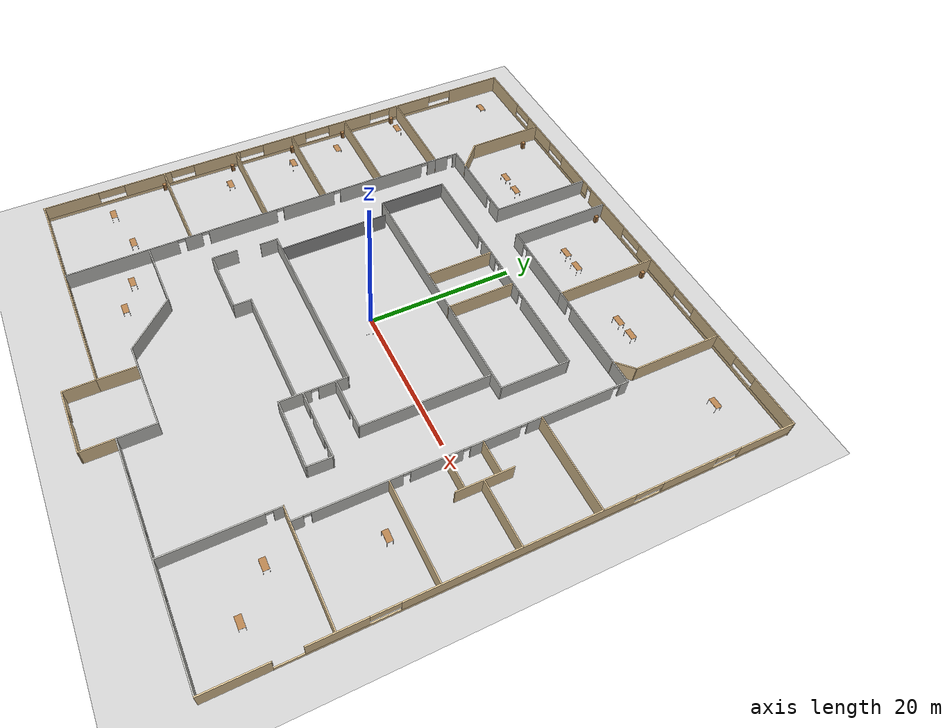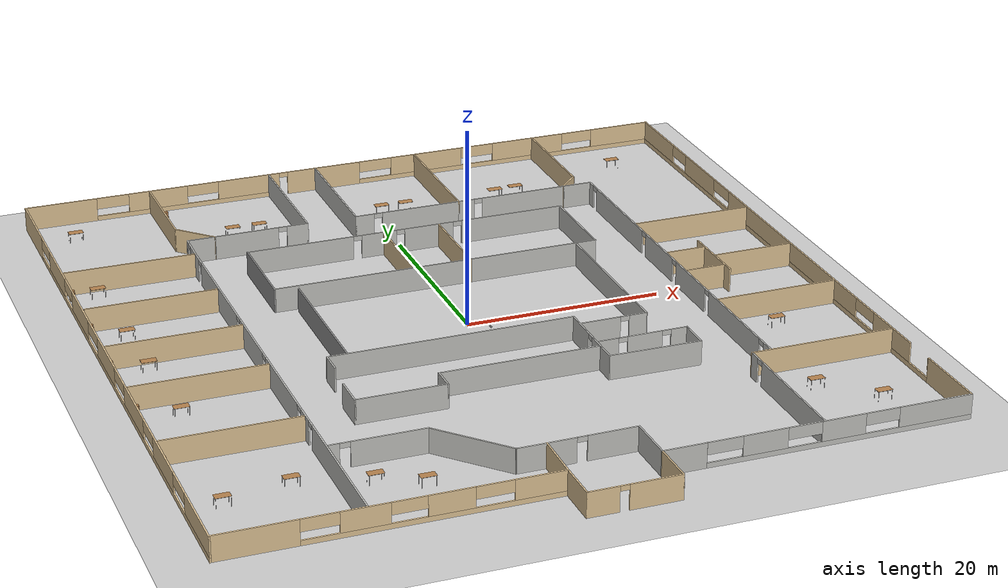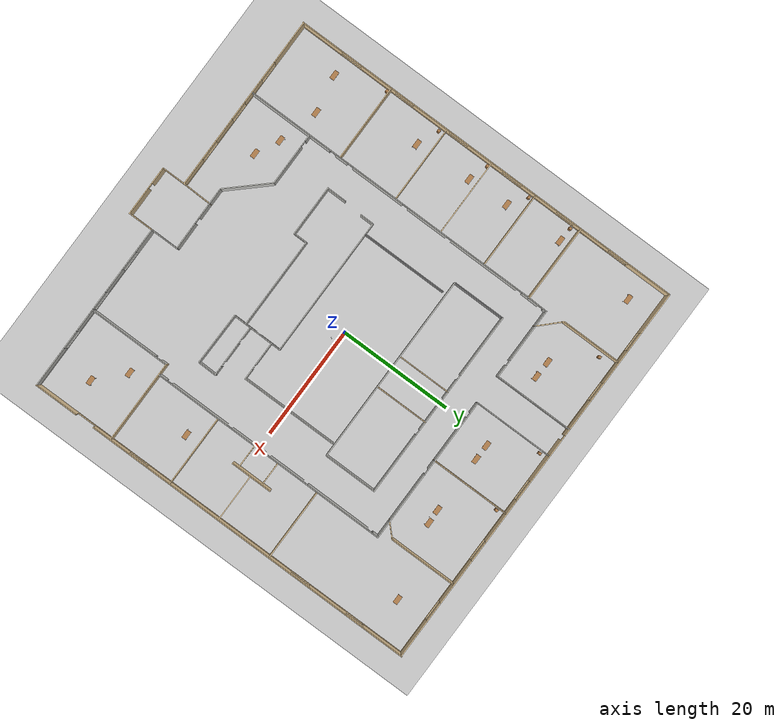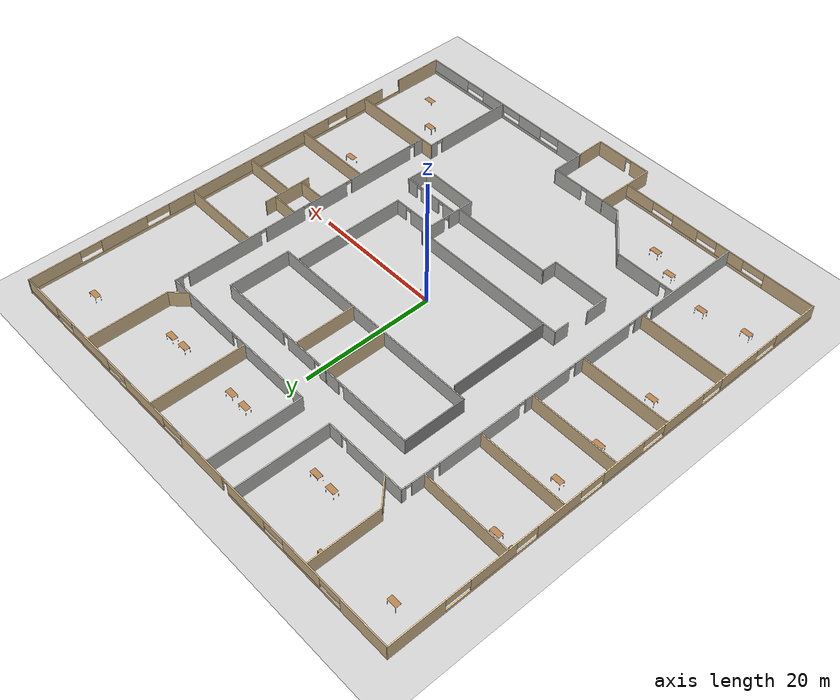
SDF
<sdf version="1.6">
 <world name="default">
  <plugin name="welcome_message" filename="libwelcome_message.so"/>
  <light name="sun" type="directional">
   <pose>0 0 10 0 -0 0</pose>
   <diffuse>0.8 0.8 0.8 1</diffuse>
   <specular>0.2 0.2 0.2 1</specular>
   <attenuation>
    <range>1000</range>
    <constant>0.9</constant>
    <linear>0.01</linear>
    <quadratic>0.001</quadratic>
   </attenuation>
   <direction>-0.5 0.1 -0.9</direction>
  </light>
  <model name="ground_plane">
   <static>1</static>
   <link name="link">
    <collision name="collision">
     <geometry><plane><normal>0 0 1</normal><size>100 100</size></plane></geometry>
     <surface><friction><ode><mu>100</mu><mu2>50</mu2></ode></friction></surface>
    </collision>
    <visual name="visual">
     <cast_shadows>0</cast_shadows>
     <geometry><plane><normal>0 0 1</normal><size>100 100</size></plane></geometry>
     <material>
      <script><uri>file://media/materials/scripts/gazebo.material</uri><name>Gazebo/Grey</name></script>
     </material>
    </visual>
   </link>
  </model>
  <gravity>0 0 -9.8</gravity>
  <magnetic_field>6e-06 2.3e-05 -4.2e-05</magnetic_field>
  <atmosphere type="adiabatic"/>
  <physics name="default_physics" default="0" type="ode">
   <max_step_size>0.001</max_step_size>
   <real_time_factor>1</real_time_factor>
   <real_time_update_rate>1000</real_time_update_rate>
  </physics>
  <scene><ambient>0.4 0.4 0.4 1</ambient><background>0.7 0.7 0.7 1</background><shadows>1</shadows></scene>
  <spherical_coordinates>
   <surface_model>EARTH_WGS84</surface_model>
   <latitude_deg>0</latitude_deg>
   <longitude_deg>0</longitude_deg>
   <elevation>0</elevation>
   <heading_deg>0</heading_deg>
  </spherical_coordinates>
  <model name="Building">
   <pose>0.1606 -0.442 0 0 -0 0</pose>
   <link name="Wall_10">
    <pose>-19.5795 -33.75 0 0 -0 0</pose>
    <visual name="Wall_10_Visual_0">
     <pose>-11.9192 0 1.25 0 -0 0</pose>
     <geometry><box><size>7.66158 0.15 2.5</size></box></geometry>
     <material>
      <script><uri>file://media/materials/scripts/gazebo.material</uri><name>Gazebo/Grey</name></script>
      <ambient>0.921569 0.807843 0.615686 1</ambient>
     </material>
     <meta><layer>0</layer></meta>
    </visual>
    <collision name="Wall_10_Collision_0">
     <geometry><box><size>7.66158 0.15 2.5</size></box></geometry>
     <pose>-11.9192 0 1.25 0 -0 0</pose>
    </collision>
    <visual name="Wall_10_Visual_1">
     <pose>3.83079 0 0.25 0 -0 0</pose>
     <geometry><box><size>23.8384 0.15 0.5</size></box></geometry>
     <material>
      <script><uri>file://media/materials/scripts/gazebo.material</uri><name>Gazebo/Grey</name></script>
      <ambient>0.921569 0.807843 0.615686 1</ambient>
     </material>
     <meta><layer>0</layer></meta>
    </visual>
    <collision name="Wall_10_Collision_1">
     <geometry><box><size>23.8384 0.15 0.5</size></box></geometry>
     <pose>3.83079 0 0.25 0 -0 0</pose>
    </collision>
    <visual name="Wall_10_Visual_2">
     <pose>-2.41376 0 1.5 0 -0 0</pose>
     <geometry><box><size>4.46303 0.15 2</size></box></geometry>
     <material>
      <script><uri>file://media/materials/scripts/gazebo.material</uri><name>Gazebo/Grey</name></script>
      <ambient>0.921569 0.807843 0.615686 1</ambient>
     </material>
     <meta><layer>0</layer></meta>
    </visual>
    <collision name="Wall_10_Collision_2">
     <geometry><box><size>4.46303 0.15 2</size></box></geometry>
     <pose>-2.41376 0 1.5 0 -0 0</pose>
    </collision>
    <visual name="Wall_10_Visual_3">
     <pose>5.19728 0 1.5 0 -0 0</pose>
     <geometry><box><size>4.24144 0.15 2</size></box></geometry>
     <material>
      <script><uri>file://media/materials/scripts/gazebo.material</uri><name>Gazebo/Grey</name></script>
      <ambient>0.921569 0.807843 0.615686 1</ambient>
     </material>
     <meta><layer>0</layer></meta>
    </visual>
    <collision name="Wall_10_Collision_3">
     <geometry><box><size>4.24144 0.15 2</size></box></geometry>
     <pose>5.19728 0 1.5 0 -0 0</pose>
    </collision>
    <visual name="Wall_10_Visual_4">
     <pose>13.3049 0 1.5 0 -0 0</pose>
     <geometry><box><size>4.89016 0.15 2</size></box></geometry>
     <material>
      <script><uri>file://media/materials/scripts/gazebo.material</uri><name>Gazebo/Grey</name></script>
      <ambient>0.921569 0.807843 0.615686 1</ambient>
     </material>
     <meta><layer>0</layer></meta>
    </visual>
    <collision name="Wall_10_Collision_4">
     <geometry><box><size>4.89016 0.15 2</size></box></geometry>
     <pose>13.3049 0 1.5 0 -0 0</pose>
    </collision>
    <visual name="Wall_10_Visual_5">
     <pose>-6.36685 0 1.9 0 -0 0</pose>
     <geometry><box><size>3.44314 0.15 1.2</size></box></geometry>
     <material>
      <script><uri>file://media/materials/scripts/gazebo.material</uri><name>Gazebo/Grey</name></script>
      <ambient>0.921569 0.807843 0.615686 1</ambient>
     </material>
     <meta><layer>0</layer></meta>
    </visual>
    <collision name="Wall_10_Collision_5">
     <geometry><box><size>3.44314 0.15 1.2</size></box></geometry>
     <pose>-6.36685 0 1.9 0 -0 0</pose>
    </collision>
    <visual name="Wall_10_Visual_6">
     <pose>1.44716 0 1.9 0 -0 0</pose>
     <geometry><box><size>3.25881 0.15 1.2</size></box></geometry>
     <material>
      <script><uri>file://media/materials/scripts/gazebo.material</uri><name>Gazebo/Grey</name></script>
      <ambient>0.921569 0.807843 0.615686 1</ambient>
     </material>
     <meta><layer>0</layer></meta>
    </visual>
    <collision name="Wall_10_Collision_6">
     <geometry><box><size>3.25881 0.15 1.2</size></box></geometry>
     <pose>1.44716 0 1.9 0 -0 0</pose>
    </collision>
    <visual name="Wall_10_Visual_7">
     <pose>9.08892 0 1.9 0 -0 0</pose>
     <geometry><box><size>3.54184 0.15 1.2</size></box></geometry>
     <material>
      <script><uri>file://media/materials/scripts/gazebo.material</uri><name>Gazebo/Grey</name></script>
      <ambient>0.921569 0.807843 0.615686 1</ambient>
     </material>
     <meta><layer>0</layer></meta>
    </visual>
    <collision name="Wall_10_Collision_7">
     <geometry><box><size>3.54184 0.15 1.2</size></box></geometry>
     <pose>9.08892 0 1.9 0 -0 0</pose>
    </collision>
   </link>
   <link name="Wall_100">
    <pose>12.7391 -11.9796 0 0 -0 3.14159</pose>
    <visual name="Wall_100_Visual_0">
     <pose>-3.75183 0 1.25 0 -0 0</pose>
     <geometry><box><size>1.74633 0.15 2.5</size></box></geometry>
     <material>
      <script><uri>file://media/materials/scripts/gazebo.material</uri><name>Gazebo/CeilingTiled</name></script>
      <ambient>1 1 1 1</ambient>
     </material>
     <meta><layer>0</layer></meta>
    </visual>
    <collision name="Wall_100_Collision_0">
     <geometry><box><size>1.74633 0.15 2.5</size></box></geometry>
     <pose>-3.75183 0 1.25 0 -0 0</pose>
    </collision>
    <visual name="Wall_100_Visual_1">
     <pose>-0.201089 0 1.25 0 -0 0</pose>
     <geometry><box><size>3.55516 0.15 2.5</size></box></geometry>
     <material>
      <script><uri>file://media/materials/scripts/gazebo.material</uri><name>Gazebo/CeilingTiled</name></script>
      <ambient>1 1 1 1</ambient>
     </material>
     <meta><layer>0</layer></meta>
    </visual>
    <collision name="Wall_100_Collision_1">
     <geometry><box><size>3.55516 0.15 2.5</size></box></geometry>
     <pose>-0.201089 0 1.25 0 -0 0</pose>
    </collision>
    <visual name="Wall_100_Visual_2">
     <pose>3.55075 0 1.25 0 -0 0</pose>
     <geometry><box><size>2.14851 0.15 2.5</size></box></geometry>
     <material>
      <script><uri>file://media/materials/scripts/gazebo.material</uri><name>Gazebo/CeilingTiled</name></script>
      <ambient>1 1 1 1</ambient>
     </material>
     <meta><layer>0</layer></meta>
    </visual>
    <collision name="Wall_100_Collision_2">
     <geometry><box><size>2.14851 0.15 2.5</size></box></geometry>
     <pose>3.55075 0 1.25 0 -0 0</pose>
    </collision>
    <visual name="Wall_100_Visual_3">
     <pose>-2.42867 0 2.25 0 -0 0</pose>
     <geometry><box><size>0.9 0.15 0.5</size></box></geometry>
     <material>
      <script><uri>file://media/materials/scripts/gazebo.material</uri><name>Gazebo/CeilingTiled</name></script>
      <ambient>1 1 1 1</ambient>
     </material>
     <meta><layer>0</layer></meta>
    </visual>
    <collision name="Wall_100_Collision_3">
     <geometry><box><size>0.9 0.15 0.5</size></box></geometry>
     <pose>-2.42867 0 2.25 0 -0 0</pose>
    </collision>
    <visual name="Wall_100_Visual_4">
     <pose>2.02649 0 2.25 0 -0 0</pose>
     <geometry><box><size>0.9 0.15 0.5</size></box></geometry>
     <material>
      <script><uri>file://media/materials/scripts/gazebo.material</uri><name>Gazebo/CeilingTiled</name></script>
      <ambient>1 1 1 1</ambient>
     </material>
     <meta><layer>0</layer></meta>
    </visual>
    <collision name="Wall_100_Collision_4">
     <geometry><box><size>0.9 0.15 0.5</size></box></geometry>
     <pose>2.02649 0 2.25 0 -0 0</pose>
    </collision>
   </link>
   <link name="Wall_103">
    <collision name="Wall_103_Collision">
     <geometry><box><size>4.25 0.15 2.5</size></box></geometry>
     <pose>0 0 1.25 0 -0 0</pose>
    </collision>
    <visual name="Wall_103_Visual">
     <pose>0 0 1.25 0 -0 0</pose>
     <geometry><box><size>4.25 0.15 2.5</size></box></geometry>
     <material>
      <script><uri>file://media/materials/scripts/gazebo.material</uri><name>Gazebo/Grey</name></script>
      <ambient>0.921569 0.807843 0.615686 1</ambient>
     </material>
     <meta><layer>0</layer></meta>
    </visual>
    <pose>24.6252 4.22124 0 0 -0 0</pose>
   </link>
   <link name="Wall_105">
    <collision name="Wall_105_Collision">
     <geometry><box><size>4.25 0.15 2.5</size></box></geometry>
     <pose>0 0 1.25 0 -0 0</pose>
    </collision>
    <visual name="Wall_105_Visual">
     <pose>0 0 1.25 0 -0 0</pose>
     <geometry><box><size>4.25 0.15 2.5</size></box></geometry>
     <material>
      <script><uri>file://media/materials/scripts/gazebo.material</uri><name>Gazebo/Grey</name></script>
      <ambient>0.921569 0.807843 0.615686 1</ambient>
     </material>
     <meta><layer>0</layer></meta>
    </visual>
    <pose>24.6252 -0.368503 0 0 -0 0</pose>
   </link>
   <link name="Wall_107">
    <collision name="Wall_107_Collision">
     <geometry><box><size>7.5 0.15 2.5</size></box></geometry>
     <pose>0 0 1.25 0 -0 0</pose>
    </collision>
    <visual name="Wall_107_Visual">
     <pose>0 0 1.25 0 -0 0</pose>
     <geometry><box><size>7.5 0.15 2.5</size></box></geometry>
     <material>
      <script><uri>file://media/materials/scripts/gazebo.material</uri><name>Gazebo/Grey</name></script>
      <ambient>0.921569 0.807843 0.615686 1</ambient>
     </material>
     <meta><layer>0</layer></meta>
    </visual>
    <pose>26.8012 2.14732 0 0 0 -1.5708</pose>
   </link>
   <link name="Wall_109">
    <collision name="Wall_109_Collision">
     <geometry><box><size>8.5 0.15 2.5</size></box></geometry>
     <pose>0 0 1.25 0 -0 0</pose>
    </collision>
    <visual name="Wall_109_Visual">
     <pose>0 0 1.25 0 -0 0</pose>
     <geometry><box><size>8.5 0.15 2.5</size></box></geometry>
     <material>
      <script><uri>file://media/materials/scripts/gazebo.material</uri><name>Gazebo/Grey</name></script>
      <ambient>0.921569 0.807843 0.615686 1</ambient>
     </material>
     <meta><layer>0</layer></meta>
    </visual>
    <pose>31.0591 1.97974 0 0 -0 0</pose>
   </link>
   <link name="Wall_11">
    <collision name="Wall_11_Collision">
     <geometry><box><size>4.25 0.15 2.5</size></box></geometry>
     <pose>0 0 1.25 0 -0 0</pose>
    </collision>
    <visual name="Wall_11_Visual">
     <pose>0 0 1.25 0 -0 0</pose>
     <geometry><box><size>4.25 0.15 2.5</size></box></geometry>
     <material>
      <script><uri>file://media/materials/scripts/gazebo.material</uri><name>Gazebo/Grey</name></script>
      <ambient>0.921569 0.807843 0.615686 1</ambient>
     </material>
     <meta><layer>0</layer></meta>
    </visual>
    <pose>-3.9045 -35.8 0 0 0 -1.5708</pose>
   </link>
   <link name="Wall_12">
    <pose>0.520502 -37.85 0 0 -0 0</pose>
    <visual name="Wall_12_Visual_0">
     <pose>-2.96768 0 1.25 0 -0 0</pose>
     <geometry><box><size>3.06464 0.15 2.5</size></box></geometry>
     <material>
      <script><uri>file://media/materials/scripts/gazebo.material</uri><name>Gazebo/Grey</name></script>
      <ambient>0.921569 0.807843 0.615686 1</ambient>
     </material>
     <meta><layer>0</layer></meta>
    </visual>
    <collision name="Wall_12_Collision_0">
     <geometry><box><size>3.06464 0.15 2.5</size></box></geometry>
     <pose>-2.96768 0 1.25 0 -0 0</pose>
    </collision>
    <visual name="Wall_12_Visual_1">
     <pose>1.98232 0 1.25 0 -0 0</pose>
     <geometry><box><size>5.03536 0.15 2.5</size></box></geometry>
     <material>
      <script><uri>file://media/materials/scripts/gazebo.material</uri><name>Gazebo/Grey</name></script>
      <ambient>0.921569 0.807843 0.615686 1</ambient>
     </material>
     <meta><layer>0</layer></meta>
    </visual>
    <collision name="Wall_12_Collision_1">
     <geometry><box><size>5.03536 0.15 2.5</size></box></geometry>
     <pose>1.98232 0 1.25 0 -0 0</pose>
    </collision>
    <visual name="Wall_12_Visual_2">
     <pose>-0.985361 0 2.25 0 -0 0</pose>
     <geometry><box><size>0.9 0.15 0.5</size></box></geometry>
     <material>
      <script><uri>file://media/materials/scripts/gazebo.material</uri><name>Gazebo/Grey</name></script>
      <ambient>0.921569 0.807843 0.615686 1</ambient>
     </material>
     <meta><layer>0</layer></meta>
    </visual>
    <collision name="Wall_12_Collision_2">
     <geometry><box><size>0.9 0.15 0.5</size></box></geometry>
     <pose>-0.985361 0 2.25 0 -0 0</pose>
    </collision>
   </link>
   <link name="Wall_13">
    <collision name="Wall_13_Collision">
     <geometry><box><size>4.5 0.15 2.5</size></box></geometry>
     <pose>0 0 1.25 0 -0 0</pose>
    </collision>
    <visual name="Wall_13_Visual">
     <pose>0 0 1.25 0 -0 0</pose>
     <geometry><box><size>4.5 0.15 2.5</size></box></geometry>
     <material>
      <script><uri>file://media/materials/scripts/gazebo.material</uri><name>Gazebo/Grey</name></script>
      <ambient>0.921569 0.807843 0.615686 1</ambient>
     </material>
     <meta><layer>0</layer></meta>
    </visual>
    <pose>4.9455 -35.675 0 0 -0 1.5708</pose>
   </link>
   <link name="Wall_14">
    <pose>20.1205 -33.5 0 0 -0 0</pose>
    <visual name="Wall_14_Visual_0">
     <pose>-13.0855 0 1.25 0 -0 0</pose>
     <geometry><box><size>4.3291 0.15 2.5</size></box></geometry>
     <material>
      <script><uri>file://media/materials/scripts/gazebo.material</uri><name>Gazebo/CeilingTiled</name></script>
      <ambient>0.921569 0.807843 0.615686 1</ambient>
     </material>
     <meta><layer>0</layer></meta>
    </visual>
    <collision name="Wall_14_Collision_0">
     <geometry><box><size>4.3291 0.15 2.5</size></box></geometry>
     <pose>-13.0855 0 1.25 0 -0 0</pose>
    </collision>
    <visual name="Wall_14_Visual_1">
     <pose>2.16455 0 0.25 0 -0 0</pose>
     <geometry><box><size>26.1709 0.15 0.5</size></box></geometry>
     <material>
      <script><uri>file://media/materials/scripts/gazebo.material</uri><name>Gazebo/CeilingTiled</name></script>
      <ambient>0.921569 0.807843 0.615686 1</ambient>
     </material>
     <meta><layer>0</layer></meta>
    </visual>
    <collision name="Wall_14_Collision_1">
     <geometry><box><size>26.1709 0.15 0.5</size></box></geometry>
     <pose>2.16455 0 0.25 0 -0 0</pose>
    </collision>
    <visual name="Wall_14_Visual_2">
     <pose>-5.28013 0 1.5 0 -0 0</pose>
     <geometry><box><size>4.37212 0.15 2</size></box></geometry>
     <material>
      <script><uri>file://media/materials/scripts/gazebo.material</uri><name>Gazebo/CeilingTiled</name></script>
      <ambient>0.921569 0.807843 0.615686 1</ambient>
     </material>
     <meta><layer>0</layer></meta>
    </visual>
    <collision name="Wall_14_Collision_2">
     <geometry><box><size>4.37212 0.15 2</size></box></geometry>
     <pose>-5.28013 0 1.5 0 -0 0</pose>
    </collision>
    <visual name="Wall_14_Visual_3">
     <pose>2.38651 0 1.5 0 -0 0</pose>
     <geometry><box><size>4.32635 0.15 2</size></box></geometry>
     <material>
      <script><uri>file://media/materials/scripts/gazebo.material</uri><name>Gazebo/CeilingTiled</name></script>
      <ambient>0.921569 0.807843 0.615686 1</ambient>
     </material>
     <meta><layer>0</layer></meta>
    </visual>
    <collision name="Wall_14_Collision_3">
     <geometry><box><size>4.32635 0.15 2</size></box></geometry>
     <pose>2.38651 0 1.5 0 -0 0</pose>
    </collision>
    <visual name="Wall_14_Visual_4">
     <pose>11.5814 0 1.5 0 -0 0</pose>
     <geometry><box><size>7.33714 0.15 2</size></box></geometry>
     <material>
      <script><uri>file://media/materials/scripts/gazebo.material</uri><name>Gazebo/CeilingTiled</name></script>
      <ambient>0.921569 0.807843 0.615686 1</ambient>
     </material>
     <meta><layer>0</layer></meta>
    </visual>
    <collision name="Wall_14_Collision_4">
     <geometry><box><size>7.33714 0.15 2</size></box></geometry>
     <pose>11.5814 0 1.5 0 -0 0</pose>
    </collision>
    <visual name="Wall_14_Visual_5">
     <pose>-9.19355 0 1.9 0 -0 0</pose>
     <geometry><box><size>3.45472 0.15 1.2</size></box></geometry>
     <material>
      <script><uri>file://media/materials/scripts/gazebo.material</uri><name>Gazebo/CeilingTiled</name></script>
      <ambient>0.921569 0.807843 0.615686 1</ambient>
     </material>
     <meta><layer>0</layer></meta>
    </visual>
    <collision name="Wall_14_Collision_5">
     <geometry><box><size>3.45472 0.15 1.2</size></box></geometry>
     <pose>-9.19355 0 1.9 0 -0 0</pose>
    </collision>
    <visual name="Wall_14_Visual_6">
     <pose>-1.43537 0 1.9 0 -0 0</pose>
     <geometry><box><size>3.3174 0.15 1.2</size></box></geometry>
     <material>
      <script><uri>file://media/materials/scripts/gazebo.material</uri><name>Gazebo/CeilingTiled</name></script>
      <ambient>0.921569 0.807843 0.615686 1</ambient>
     </material>
     <meta><layer>0</layer></meta>
    </visual>
    <collision name="Wall_14_Collision_6">
     <geometry><box><size>3.3174 0.15 1.2</size></box></geometry>
     <pose>-1.43537 0 1.9 0 -0 0</pose>
    </collision>
    <visual name="Wall_14_Visual_7">
     <pose>6.23127 0 1.9 0 -0 0</pose>
     <geometry><box><size>3.36317 0.15 1.2</size></box></geometry>
     <material>
      <script><uri>file://media/materials/scripts/gazebo.material</uri><name>Gazebo/CeilingTiled</name></script>
      <ambient>0.921569 0.807843 0.615686 1</ambient>
     </material>
     <meta><layer>0</layer></meta>
    </visual>
    <collision name="Wall_14_Collision_7">
     <geometry><box><size>3.36317 0.15 1.2</size></box></geometry>
     <pose>6.23127 0 1.9 0 -0 0</pose>
    </collision>
   </link>
   <link name="Wall_15">
    <pose>35.2955 2.175 0 0 -0 1.5708</pose>
    <visual name="Wall_15_Visual_0">
     <pose>-31.881 0 1.25 0 -0 0</pose>
     <geometry><box><size>7.73799 0.15 2.5</size></box></geometry>
     <material>
      <script><uri>file://media/materials/scripts/gazebo.material</uri><name>Gazebo/Grey</name></script>
      <ambient>0.921569 0.807843 0.615686 1</ambient>
     </material>
     <meta><layer>0</layer></meta>
    </visual>
    <collision name="Wall_15_Collision_0">
     <geometry><box><size>7.73799 0.15 2.5</size></box></geometry>
     <pose>-31.881 0 1.25 0 -0 0</pose>
    </collision>
    <visual name="Wall_15_Visual_1">
     <pose>3.869 0 0.25 0 -0 0</pose>
     <geometry><box><size>63.762 0.15 0.5</size></box></geometry>
     <material>
      <script><uri>file://media/materials/scripts/gazebo.material</uri><name>Gazebo/Grey</name></script>
      <ambient>0.921569 0.807843 0.615686 1</ambient>
     </material>
     <meta><layer>0</layer></meta>
    </visual>
    <collision name="Wall_15_Collision_1">
     <geometry><box><size>63.762 0.15 0.5</size></box></geometry>
     <pose>3.869 0 0.25 0 -0 0</pose>
    </collision>
    <visual name="Wall_15_Visual_2">
     <pose>-21.1676 0 1.5 0 -0 0</pose>
     <geometry><box><size>6.97218 0.15 2</size></box></geometry>
     <material>
      <script><uri>file://media/materials/scripts/gazebo.material</uri><name>Gazebo/Grey</name></script>
      <ambient>0.921569 0.807843 0.615686 1</ambient>
     </material>
     <meta><layer>0</layer></meta>
    </visual>
    <collision name="Wall_15_Collision_2">
     <geometry><box><size>6.97218 0.15 2</size></box></geometry>
     <pose>-21.1676 0 1.5 0 -0 0</pose>
    </collision>
    <visual name="Wall_15_Visual_3">
     <pose>-0.106032 0 1.5 0 -0 0</pose>
     <geometry><box><size>28.1209 0.15 2</size></box></geometry>
     <material>
      <script><uri>file://media/materials/scripts/gazebo.material</uri><name>Gazebo/Grey</name></script>
      <ambient>0.921569 0.807843 0.615686 1</ambient>
     </material>
     <meta><layer>0</layer></meta>
    </visual>
    <collision name="Wall_15_Collision_3">
     <geometry><box><size>28.1209 0.15 2</size></box></geometry>
     <pose>-0.106032 0 1.5 0 -0 0</pose>
    </collision>
    <visual name="Wall_15_Visual_4">
     <pose>21.1713 0 1.5 0 -0 0</pose>
     <geometry><box><size>7.19064 0.15 2</size></box></geometry>
     <material>
      <script><uri>file://media/materials/scripts/gazebo.material</uri><name>Gazebo/Grey</name></script>
      <ambient>0.921569 0.807843 0.615686 1</ambient>
     </material>
     <meta><layer>0</layer></meta>
    </visual>
    <collision name="Wall_15_Collision_4">
     <geometry><box><size>7.19064 0.15 2</size></box></geometry>
     <pose>21.1713 0 1.5 0 -0 0</pose>
    </collision>
    <visual name="Wall_15_Visual_5">
     <pose>31.8827 0 1.5 0 -0 0</pose>
     <geometry><box><size>7.73457 0.15 2</size></box></geometry>
     <material>
      <script><uri>file://media/materials/scripts/gazebo.material</uri><name>Gazebo/Grey</name></script>
      <ambient>0.921569 0.807843 0.615686 1</ambient>
     </material>
     <meta><layer>0</layer></meta>
    </visual>
    <collision name="Wall_15_Collision_5">
     <geometry><box><size>7.73457 0.15 2</size></box></geometry>
     <pose>31.8827 0 1.5 0 -0 0</pose>
    </collision>
    <visual name="Wall_15_Visual_6">
     <pose>-27.9687 0 1.9 0 -0 0</pose>
     <geometry><box><size>0.086667 0.15 1.2</size></box></geometry>
     <material>
      <script><uri>file://media/materials/scripts/gazebo.material</uri><name>Gazebo/Grey</name></script>
      <ambient>0.921569 0.807843 0.615686 1</ambient>
     </material>
     <meta><layer>0</layer></meta>
    </visual>
    <collision name="Wall_15_Collision_6">
     <geometry><box><size>0.086667 0.15 1.2</size></box></geometry>
     <pose>-27.9687 0 1.9 0 -0 0</pose>
    </collision>
    <visual name="Wall_15_Visual_7">
     <pose>-15.924 0 1.9 0 -0 0</pose>
     <geometry><box><size>3.51504 0.15 1.2</size></box></geometry>
     <material>
      <script><uri>file://media/materials/scripts/gazebo.material</uri><name>Gazebo/Grey</name></script>
      <ambient>0.921569 0.807843 0.615686 1</ambient>
     </material>
     <meta><layer>0</layer></meta>
    </visual>
    <collision name="Wall_15_Collision_7">
     <geometry><box><size>3.51504 0.15 1.2</size></box></geometry>
     <pose>-15.924 0 1.9 0 -0 0</pose>
    </collision>
    <visual name="Wall_15_Visual_8">
     <pose>15.7652 0 1.9 0 -0 0</pose>
     <geometry><box><size>3.62151 0.15 1.2</size></box></geometry>
     <material>
      <script><uri>file://media/materials/scripts/gazebo.material</uri><name>Gazebo/Grey</name></script>
      <ambient>0.921569 0.807843 0.615686 1</ambient>
     </material>
     <meta><layer>0</layer></meta>
    </visual>
    <collision name="Wall_15_Collision_8">
     <geometry><box><size>3.62151 0.15 1.2</size></box></geometry>
     <pose>15.7652 0 1.9 0 -0 0</pose>
    </collision>
    <visual name="Wall_15_Visual_9">
     <pose>26.391 0 1.9 0 -0 0</pose>
     <geometry><box><size>3.24886 0.15 1.2</size></box></geometry>
     <material>
      <script><uri>file://media/materials/scripts/gazebo.material</uri><name>Gazebo/Grey</name></script>
      <ambient>0.921569 0.807843 0.615686 1</ambient>
     </material>
     <meta><layer>0</layer></meta>
    </visual>
    <collision name="Wall_15_Collision_9">
     <geometry><box><size>3.24886 0.15 1.2</size></box></geometry>
     <pose>26.391 0 1.9 0 -0 0</pose>
    </collision>
   </link>
   <link name="Wall_181">
    <pose>8.05273 -10.6417 0 0 -0 1.55946</pose>
    <visual name="Wall_181_Visual_0">
     <pose>-2.4226 0 1.25 0 -0 0</pose>
     <geometry><box><size>4.1635 0.15 2.5</size></box></geometry>
     <material>
      <script><uri>file://media/materials/scripts/gazebo.material</uri><name>Gazebo/CeilingTiled</name></script>
      <ambient>1 1 1 1</ambient>
     </material>
     <meta><layer>0</layer></meta>
    </visual>
    <collision name="Wall_181_Collision_0">
     <geometry><box><size>4.1635 0.15 2.5</size></box></geometry>
     <pose>-2.4226 0 1.25 0 -0 0</pose>
    </collision>
    <visual name="Wall_181_Visual_1">
     <pose>2.53175 0 1.25 0 -0 0</pose>
     <geometry><box><size>3.94519 0.15 2.5</size></box></geometry>
     <material>
      <script><uri>file://media/materials/scripts/gazebo.material</uri><name>Gazebo/CeilingTiled</name></script>
      <ambient>1 1 1 1</ambient>
     </material>
     <meta><layer>0</layer></meta>
    </visual>
    <collision name="Wall_181_Collision_1">
     <geometry><box><size>3.94519 0.15 2.5</size></box></geometry>
     <pose>2.53175 0 1.25 0 -0 0</pose>
    </collision>
    <visual name="Wall_181_Visual_2">
     <pose>0.109156 0 2.25 0 -0 0</pose>
     <geometry><box><size>0.9 0.15 0.5</size></box></geometry>
     <material>
      <script><uri>file://media/materials/scripts/gazebo.material</uri><name>Gazebo/CeilingTiled</name></script>
      <ambient>1 1 1 1</ambient>
     </material>
     <meta><layer>0</layer></meta>
    </visual>
    <collision name="Wall_181_Collision_2">
     <geometry><box><size>0.9 0.15 0.5</size></box></geometry>
     <pose>0.109156 0 2.25 0 -0 0</pose>
    </collision>
   </link>
   <link name="Wall_19">
    <pose>0.058011 37.7805 0 0 -0 0</pose>
    <visual name="Wall_19_Visual_0">
     <pose>-31.6032 0 1.25 0 -0 0</pose>
     <geometry><box><size>7.48557 0.15 2.5</size></box></geometry>
     <material>
      <script><uri>file://media/materials/scripts/gazebo.material</uri><name>Gazebo/Grey</name></script>
      <ambient>0.921569 0.807843 0.615686 1</ambient>
     </material>
     <meta><layer>0</layer></meta>
    </visual>
    <collision name="Wall_19_Collision_0">
     <geometry><box><size>7.48557 0.15 2.5</size></box></geometry>
     <pose>-31.6032 0 1.25 0 -0 0</pose>
    </collision>
    <visual name="Wall_19_Visual_1">
     <pose>-2.88179 0 1.25 0 -0 0</pose>
     <geometry><box><size>8.13835 0.15 2.5</size></box></geometry>
     <material>
      <script><uri>file://media/materials/scripts/gazebo.material</uri><name>Gazebo/Grey</name></script>
      <ambient>0.921569 0.807843 0.615686 1</ambient>
     </material>
     <meta><layer>0</layer></meta>
    </visual>
    <collision name="Wall_19_Collision_1">
     <geometry><box><size>8.13835 0.15 2.5</size></box></geometry>
     <pose>-2.88179 0 1.25 0 -0 0</pose>
    </collision>
    <visual name="Wall_19_Visual_2">
     <pose>-17.8557 0 0.25 0 -0 0</pose>
     <geometry><box><size>20.0095 0.15 0.5</size></box></geometry>
     <material>
      <script><uri>file://media/materials/scripts/gazebo.material</uri><name>Gazebo/Grey</name></script>
      <ambient>0.921569 0.807843 0.615686 1</ambient>
     </material>
     <meta><layer>0</layer></meta>
    </visual>
    <collision name="Wall_19_Collision_2">
     <geometry><box><size>20.0095 0.15 0.5</size></box></geometry>
     <pose>-17.8557 0 0.25 0 -0 0</pose>
    </collision>
    <visual name="Wall_19_Visual_3">
     <pose>18.2667 0 0.25 0 -0 0</pose>
     <geometry><box><size>34.1586 0.15 0.5</size></box></geometry>
     <material>
      <script><uri>file://media/materials/scripts/gazebo.material</uri><name>Gazebo/Grey</name></script>
      <ambient>0.921569 0.807843 0.615686 1</ambient>
     </material>
     <meta><layer>0</layer></meta>
    </visual>
    <collision name="Wall_19_Collision_3">
     <geometry><box><size>34.1586 0.15 0.5</size></box></geometry>
     <pose>18.2667 0 0.25 0 -0 0</pose>
    </collision>
    <visual name="Wall_19_Visual_4">
     <pose>-21.2381 0 1.5 0 -0 0</pose>
     <geometry><box><size>6.36726 0.15 2</size></box></geometry>
     <material>
      <script><uri>file://media/materials/scripts/gazebo.material</uri><name>Gazebo/Grey</name></script>
      <ambient>0.921569 0.807843 0.615686 1</ambient>
     </material>
     <meta><layer>0</layer></meta>
    </visual>
    <collision name="Wall_19_Collision_4">
     <geometry><box><size>6.36726 0.15 2</size></box></geometry>
     <pose>-21.2381 0 1.5 0 -0 0</pose>
    </collision>
    <visual name="Wall_19_Visual_5">
     <pose>-11.2566 0 1.5 0 -0 0</pose>
     <geometry><box><size>6.81117 0.15 2</size></box></geometry>
     <material>
      <script><uri>file://media/materials/scripts/gazebo.material</uri><name>Gazebo/Grey</name></script>
      <ambient>0.921569 0.807843 0.615686 1</ambient>
     </material>
     <meta><layer>0</layer></meta>
    </visual>
    <collision name="Wall_19_Collision_5">
     <geometry><box><size>6.81117 0.15 2</size></box></geometry>
     <pose>-11.2566 0 1.5 0 -0 0</pose>
    </collision>
    <visual name="Wall_19_Visual_6">
     <pose>-11.2566 0 1.5 0 -0 0</pose>
     <geometry><box><size>6.81117 0.15 2</size></box></geometry>
     <material>
      <script><uri>file://media/materials/scripts/gazebo.material</uri><name>Gazebo/Grey</name></script>
      <ambient>0.921569 0.807843 0.615686 1</ambient>
     </material>
     <meta><layer>0</layer></meta>
    </visual>
    <collision name="Wall_19_Collision_6">
     <geometry><box><size>6.81117 0.15 2</size></box></geometry>
     <pose>-11.2566 0 1.5 0 -0 0</pose>
    </collision>
    <visual name="Wall_19_Visual_7">
     <pose>8.90248 0 1.5 0 -0 0</pose>
     <geometry><box><size>8.18717 0.15 2</size></box></geometry>
     <material>
      <script><uri>file://media/materials/scripts/gazebo.material</uri><name>Gazebo/Grey</name></script>
      <ambient>0.921569 0.807843 0.615686 1</ambient>
     </material>
     <meta><layer>0</layer></meta>
    </visual>
    <collision name="Wall_19_Collision_7">
     <geometry><box><size>8.18717 0.15 2</size></box></geometry>
     <pose>8.90248 0 1.5 0 -0 0</pose>
    </collision>
    <visual name="Wall_19_Visual_8">
     <pose>20.8176 0 1.5 0 -0 0</pose>
     <geometry><box><size>8.2936 0.15 2</size></box></geometry>
     <material>
      <script><uri>file://media/materials/scripts/gazebo.material</uri><name>Gazebo/Grey</name></script>
      <ambient>0.921569 0.807843 0.615686 1</ambient>
     </material>
     <meta><layer>0</layer></meta>
    </visual>
    <collision name="Wall_19_Collision_8">
     <geometry><box><size>8.2936 0.15 2</size></box></geometry>
     <pose>20.8176 0 1.5 0 -0 0</pose>
    </collision>
    <visual name="Wall_19_Visual_9">
     <pose>31.9127 0 1.5 0 -0 0</pose>
     <geometry><box><size>6.86653 0.15 2</size></box></geometry>
     <material>
      <script><uri>file://media/materials/scripts/gazebo.material</uri><name>Gazebo/Grey</name></script>
      <ambient>0.921569 0.807843 0.615686 1</ambient>
     </material>
     <meta><layer>0</layer></meta>
    </visual>
    <collision name="Wall_19_Collision_9">
     <geometry><box><size>6.86653 0.15 2</size></box></geometry>
     <pose>31.9127 0 1.5 0 -0 0</pose>
    </collision>
    <visual name="Wall_19_Visual_10">
     <pose>-26.1411 0 1.9 0 -0 0</pose>
     <geometry><box><size>3.43866 0.15 1.2</size></box></geometry>
     <material>
      <script><uri>file://media/materials/scripts/gazebo.material</uri><name>Gazebo/Grey</name></script>
      <ambient>0.921569 0.807843 0.615686 1</ambient>
     </material>
     <meta><layer>0</layer></meta>
    </visual>
    <collision name="Wall_19_Collision_10">
     <geometry><box><size>3.43866 0.15 1.2</size></box></geometry>
     <pose>-26.1411 0 1.9 0 -0 0</pose>
    </collision>
    <visual name="Wall_19_Visual_11">
     <pose>2.99814 0 1.9 0 -0 0</pose>
     <geometry><box><size>3.62151 0.15 1.2</size></box></geometry>
     <material>
      <script><uri>file://media/materials/scripts/gazebo.material</uri><name>Gazebo/Grey</name></script>
      <ambient>0.921569 0.807843 0.615686 1</ambient>
     </material>
     <meta><layer>0</layer></meta>
    </visual>
    <collision name="Wall_19_Collision_11">
     <geometry><box><size>3.62151 0.15 1.2</size></box></geometry>
     <pose>2.99814 0 1.9 0 -0 0</pose>
    </collision>
    <visual name="Wall_19_Visual_12">
     <pose>-16.3583 0 1.9 0 -0 0</pose>
     <geometry><box><size>3.39237 0.15 1.2</size></box></geometry>
     <material>
      <script><uri>file://media/materials/scripts/gazebo.material</uri><name>Gazebo/Grey</name></script>
      <ambient>0.921569 0.807843 0.615686 1</ambient>
     </material>
     <meta><layer>0</layer></meta>
    </visual>
    <collision name="Wall_19_Collision_12">
     <geometry><box><size>3.39237 0.15 1.2</size></box></geometry>
     <pose>-16.3583 0 1.9 0 -0 0</pose>
    </collision>
    <visual name="Wall_19_Visual_13">
     <pose>14.8334 0 1.9 0 -0 0</pose>
     <geometry><box><size>3.67475 0.15 1.2</size></box></geometry>
     <material>
      <script><uri>file://media/materials/scripts/gazebo.material</uri><name>Gazebo/Grey</name></script>
      <ambient>0.921569 0.807843 0.615686 1</ambient>
     </material>
     <meta><layer>0</layer></meta>
    </visual>
    <collision name="Wall_19_Collision_13">
     <geometry><box><size>3.67475 0.15 1.2</size></box></geometry>
     <pose>14.8334 0 1.9 0 -0 0</pose>
    </collision>
    <visual name="Wall_19_Visual_14">
     <pose>26.7219 0 1.9 0 -0 0</pose>
     <geometry><box><size>3.51504 0.15 1.2</size></box></geometry>
     <material>
      <script><uri>file://media/materials/scripts/gazebo.material</uri><name>Gazebo/Grey</name></script>
      <ambient>0.921569 0.807843 0.615686 1</ambient>
     </material>
     <meta><layer>0</layer></meta>
    </visual>
    <collision name="Wall_19_Collision_14">
     <geometry><box><size>3.51504 0.15 1.2</size></box></geometry>
     <pose>26.7219 0 1.9 0 -0 0</pose>
    </collision>
    <visual name="Wall_19_Visual_15">
     <pose>-7.40097 0 2.25 0 -0 0</pose>
     <geometry><box><size>0.9 0.15 0.5</size></box></geometry>
     <material>
      <script><uri>file://media/materials/scripts/gazebo.material</uri><name>Gazebo/Grey</name></script>
      <ambient>0.921569 0.807843 0.615686 1</ambient>
     </material>
     <meta><layer>0</layer></meta>
    </visual>
    <collision name="Wall_19_Collision_15">
     <geometry><box><size>0.9 0.15 0.5</size></box></geometry>
     <pose>-7.40097 0 2.25 0 -0 0</pose>
    </collision>
    <visual name="Wall_19_Visual_16">
     <pose>-7.40097 0 2.25 0 -0 0</pose>
     <geometry><box><size>0.9 0.15 0.5</size></box></geometry>
     <material>
      <script><uri>file://media/materials/scripts/gazebo.material</uri><name>Gazebo/Grey</name></script>
      <ambient>0.921569 0.807843 0.615686 1</ambient>
     </material>
     <meta><layer>0</layer></meta>
    </visual>
    <collision name="Wall_19_Collision_16">
     <geometry><box><size>0.9 0.15 0.5</size></box></geometry>
     <pose>-7.40097 0 2.25 0 -0 0</pose>
    </collision>
   </link>
   <link name="Wall_2">
    <pose>-35.329 1.98049 0 0 0 -1.5708</pose>
    <visual name="Wall_2_Visual_0">
     <pose>-31.7867 0 1.25 0 -0 0</pose>
     <geometry><box><size>8.1767 0.15 2.5</size></box></geometry>
     <material>
      <script><uri>file://media/materials/scripts/gazebo.material</uri><name>Gazebo/Grey</name></script>
      <ambient>0.921569 0.807843 0.615686 1</ambient>
     </material>
     <meta><layer>0</layer></meta>
    </visual>
    <collision name="Wall_2_Collision_0">
     <geometry><box><size>8.1767 0.15 2.5</size></box></geometry>
     <pose>-31.7867 0 1.25 0 -0 0</pose>
    </collision>
    <visual name="Wall_2_Visual_1">
     <pose>4.08835 0 0.25 0 -0 0</pose>
     <geometry><box><size>63.5733 0.15 0.5</size></box></geometry>
     <material>
      <script><uri>file://media/materials/scripts/gazebo.material</uri><name>Gazebo/Grey</name></script>
      <ambient>0.921569 0.807843 0.615686 1</ambient>
     </material>
     <meta><layer>0</layer></meta>
    </visual>
    <collision name="Wall_2_Collision_1">
     <geometry><box><size>63.5733 0.15 0.5</size></box></geometry>
     <pose>4.08835 0 0.25 0 -0 0</pose>
    </collision>
    <visual name="Wall_2_Visual_2">
     <pose>-20.6272 0 1.5 0 -0 0</pose>
     <geometry><box><size>6.88516 0.15 2</size></box></geometry>
     <material>
      <script><uri>file://media/materials/scripts/gazebo.material</uri><name>Gazebo/Grey</name></script>
      <ambient>0.921569 0.807843 0.615686 1</ambient>
     </material>
     <meta><layer>0</layer></meta>
    </visual>
    <collision name="Wall_2_Collision_2">
     <geometry><box><size>6.88516 0.15 2</size></box></geometry>
     <pose>-20.6272 0 1.5 0 -0 0</pose>
    </collision>
    <visual name="Wall_2_Visual_3">
     <pose>-10.487 0 1.5 0 -0 0</pose>
     <geometry><box><size>6.88516 0.15 2</size></box></geometry>
     <material>
      <script><uri>file://media/materials/scripts/gazebo.material</uri><name>Gazebo/Grey</name></script>
      <ambient>0.921569 0.807843 0.615686 1</ambient>
     </material>
     <meta><layer>0</layer></meta>
    </visual>
    <collision name="Wall_2_Collision_3">
     <geometry><box><size>6.88516 0.15 2</size></box></geometry>
     <pose>-10.487 0 1.5 0 -0 0</pose>
    </collision>
    <visual name="Wall_2_Visual_4">
     <pose>0.140779 0 1.5 0 -0 0</pose>
     <geometry><box><size>6.7931 0.15 2</size></box></geometry>
     <material>
      <script><uri>file://media/materials/scripts/gazebo.material</uri><name>Gazebo/Grey</name></script>
      <ambient>0.921569 0.807843 0.615686 1</ambient>
     </material>
     <meta><layer>0</layer></meta>
    </visual>
    <collision name="Wall_2_Collision_4">
     <geometry><box><size>6.7931 0.15 2</size></box></geometry>
     <pose>0.140779 0 1.5 0 -0 0</pose>
    </collision>
    <visual name="Wall_2_Visual_5">
     <pose>10.6748 0 1.5 0 -0 0</pose>
     <geometry><box><size>7.0604 0.15 2</size></box></geometry>
     <material>
      <script><uri>file://media/materials/scripts/gazebo.material</uri><name>Gazebo/Grey</name></script>
      <ambient>0.921569 0.807843 0.615686 1</ambient>
     </material>
     <meta><layer>0</layer></meta>
    </visual>
    <collision name="Wall_2_Collision_5">
     <geometry><box><size>7.0604 0.15 2</size></box></geometry>
     <pose>10.6748 0 1.5 0 -0 0</pose>
    </collision>
    <visual name="Wall_2_Visual_6">
     <pose>21.0585 0 1.5 0 -0 0</pose>
     <geometry><box><size>6.84339 0.15 2</size></box></geometry>
     <material>
      <script><uri>file://media/materials/scripts/gazebo.material</uri><name>Gazebo/Grey</name></script>
      <ambient>0.921569 0.807843 0.615686 1</ambient>
     </material>
     <meta><layer>0</layer></meta>
    </visual>
    <collision name="Wall_2_Collision_6">
     <geometry><box><size>6.84339 0.15 2</size></box></geometry>
     <pose>21.0585 0 1.5 0 -0 0</pose>
    </collision>
    <visual name="Wall_2_Visual_7">
     <pose>32.0339 0 1.5 0 -0 0</pose>
     <geometry><box><size>7.68221 0.15 2</size></box></geometry>
     <material>
      <script><uri>file://media/materials/scripts/gazebo.material</uri><name>Gazebo/Grey</name></script>
      <ambient>0.921569 0.807843 0.615686 1</ambient>
     </material>
     <meta><layer>0</layer></meta>
    </visual>
    <collision name="Wall_2_Collision_7">
     <geometry><box><size>7.68221 0.15 2</size></box></geometry>
     <pose>32.0339 0 1.5 0 -0 0</pose>
    </collision>
    <visual name="Wall_2_Visual_8">
     <pose>-25.884 0 1.9 0 -0 0</pose>
     <geometry><box><size>3.62857 0.15 1.2</size></box></geometry>
     <material>
      <script><uri>file://media/materials/scripts/gazebo.material</uri><name>Gazebo/Grey</name></script>
      <ambient>0.921569 0.807843 0.615686 1</ambient>
     </material>
     <meta><layer>0</layer></meta>
    </visual>
    <collision name="Wall_2_Collision_8">
     <geometry><box><size>3.62857 0.15 1.2</size></box></geometry>
     <pose>-25.884 0 1.9 0 -0 0</pose>
    </collision>
    <visual name="Wall_2_Visual_9">
     <pose>-15.5571 0 1.9 0 -0 0</pose>
     <geometry><box><size>3.25498 0.15 1.2</size></box></geometry>
     <material>
      <script><uri>file://media/materials/scripts/gazebo.material</uri><name>Gazebo/Grey</name></script>
      <ambient>0.921569 0.807843 0.615686 1</ambient>
     </material>
     <meta><layer>0</layer></meta>
    </visual>
    <collision name="Wall_2_Collision_9">
     <geometry><box><size>3.25498 0.15 1.2</size></box></geometry>
     <pose>-15.5571 0 1.9 0 -0 0</pose>
    </collision>
    <visual name="Wall_2_Visual_10">
     <pose>-5.15011 0 1.9 0 -0 0</pose>
     <geometry><box><size>3.78867 0.15 1.2</size></box></geometry>
     <material>
      <script><uri>file://media/materials/scripts/gazebo.material</uri><name>Gazebo/Grey</name></script>
      <ambient>0.921569 0.807843 0.615686 1</ambient>
     </material>
     <meta><layer>0</layer></meta>
    </visual>
    <collision name="Wall_2_Collision_10">
     <geometry><box><size>3.78867 0.15 1.2</size></box></geometry>
     <pose>-5.15011 0 1.9 0 -0 0</pose>
    </collision>
    <visual name="Wall_2_Visual_11">
     <pose>5.34097 0 1.9 0 -0 0</pose>
     <geometry><box><size>3.60729 0.15 1.2</size></box></geometry>
     <material>
      <script><uri>file://media/materials/scripts/gazebo.material</uri><name>Gazebo/Grey</name></script>
      <ambient>0.921569 0.807843 0.615686 1</ambient>
     </material>
     <meta><layer>0</layer></meta>
    </visual>
    <collision name="Wall_2_Collision_11">
     <geometry><box><size>3.60729 0.15 1.2</size></box></geometry>
     <pose>5.34097 0 1.9 0 -0 0</pose>
    </collision>
    <visual name="Wall_2_Visual_12">
     <pose>15.9209 0 1.9 0 -0 0</pose>
     <geometry><box><size>3.43183 0.15 1.2</size></box></geometry>
     <material>
      <script><uri>file://media/materials/scripts/gazebo.material</uri><name>Gazebo/Grey</name></script>
      <ambient>0.921569 0.807843 0.615686 1</ambient>
     </material>
     <meta><layer>0</layer></meta>
    </visual>
    <collision name="Wall_2_Collision_12">
     <geometry><box><size>3.43183 0.15 1.2</size></box></geometry>
     <pose>15.9209 0 1.9 0 -0 0</pose>
    </collision>
    <visual name="Wall_2_Visual_13">
     <pose>26.3365 0 1.9 0 -0 0</pose>
     <geometry><box><size>3.71256 0.15 1.2</size></box></geometry>
     <material>
      <script><uri>file://media/materials/scripts/gazebo.material</uri><name>Gazebo/Grey</name></script>
      <ambient>0.921569 0.807843 0.615686 1</ambient>
     </material>
     <meta><layer>0</layer></meta>
    </visual>
    <collision name="Wall_2_Collision_13">
     <geometry><box><size>3.71256 0.15 1.2</size></box></geometry>
     <pose>26.3365 0 1.9 0 -0 0</pose>
    </collision>
   </link>
   <link name="Wall_21">
    <collision name="Wall_21_Collision">
     <geometry><box><size>10.75 0.15 2.5</size></box></geometry>
     <pose>0 0 1.25 0 -0 0</pose>
    </collision>
    <visual name="Wall_21_Visual">
     <pose>0 0 1.25 0 -0 0</pose>
     <geometry><box><size>10.75 0.15 2.5</size></box></geometry>
     <material>
      <script><uri>file://media/materials/scripts/gazebo.material</uri><name>Gazebo/Grey</name></script>
      <ambient>0.921569 0.807843 0.615686 1</ambient>
     </material>
     <meta><layer>0</layer></meta>
    </visual>
    <pose>-22.0834 32.3763 0 0 0 -1.5708</pose>
   </link>
   <link name="Wall_22">
    <collision name="Wall_22_Collision">
     <geometry><box><size>4.75 0.15 2.5</size></box></geometry>
     <pose>0 0 1.25 0 -0 0</pose>
    </collision>
    <visual name="Wall_22_Visual">
     <pose>0 0 1.25 0 -0 0</pose>
     <geometry><box><size>4.75 0.15 2.5</size></box></geometry>
     <material>
      <script><uri>file://media/materials/scripts/gazebo.material</uri><name>Gazebo/Grey</name></script>
      <ambient>0.921569 0.807843 0.615686 1</ambient>
     </material>
     <meta><layer>0</layer></meta>
    </visual>
    <pose>-20.457 25.45 0 0 0 -0.785398</pose>
   </link>
   <link name="Wall_23">
    <pose>-13.9057 23.8237 0 0 -0 0</pose>
    <visual name="Wall_23_Visual_0">
     <pose>-1.59265 0 1.25 0 -0 0</pose>
     <geometry><box><size>6.8147 0.15 2.5</size></box></geometry>
     <material>
      <script><uri>file://media/materials/scripts/gazebo.material</uri><name>Gazebo/CeilingTiled</name></script>
      <ambient>1 1 1 1</ambient>
     </material>
     <meta><layer>0</layer></meta>
    </visual>
    <collision name="Wall_23_Collision_0">
     <geometry><box><size>6.8147 0.15 2.5</size></box></geometry>
     <pose>-1.59265 0 1.25 0 -0 0</pose>
    </collision>
    <visual name="Wall_23_Visual_1">
     <pose>3.85735 0 1.25 0 -0 0</pose>
     <geometry><box><size>2.2853 0.15 2.5</size></box></geometry>
     <material>
      <script><uri>file://media/materials/scripts/gazebo.material</uri><name>Gazebo/CeilingTiled</name></script>
      <ambient>1 1 1 1</ambient>
     </material>
     <meta><layer>0</layer></meta>
    </visual>
    <collision name="Wall_23_Collision_1">
     <geometry><box><size>2.2853 0.15 2.5</size></box></geometry>
     <pose>3.85735 0 1.25 0 -0 0</pose>
    </collision>
    <visual name="Wall_23_Visual_2">
     <pose>2.2647 0 2.25 0 -0 0</pose>
     <geometry><box><size>0.9 0.15 0.5</size></box></geometry>
     <material>
      <script><uri>file://media/materials/scripts/gazebo.material</uri><name>Gazebo/CeilingTiled</name></script>
      <ambient>1 1 1 1</ambient>
     </material>
     <meta><layer>0</layer></meta>
    </visual>
    <collision name="Wall_23_Collision_2">
     <geometry><box><size>0.9 0.15 0.5</size></box></geometry>
     <pose>2.2647 0 2.25 0 -0 0</pose>
    </collision>
   </link>
   <link name="Wall_24">
    <collision name="Wall_24_Collision">
     <geometry><box><size>14 0.15 2.5</size></box></geometry>
     <pose>0 0 1.25 0 -0 0</pose>
    </collision>
    <visual name="Wall_24_Visual">
     <pose>0 0 1.25 0 -0 0</pose>
     <geometry><box><size>14 0.15 2.5</size></box></geometry>
     <material>
      <script><uri>file://media/materials/scripts/gazebo.material</uri><name>Gazebo/CeilingTiled</name></script>
      <ambient>1 1 1 1</ambient>
     </material>
     <meta><layer>0</layer></meta>
    </visual>
    <pose>-8.9807 30.7487 0 0 -0 1.5708</pose>
   </link>
   <link name="Wall_26">
    <collision name="Wall_26_Collision">
     <geometry><box><size>14 0.15 2.5</size></box></geometry>
     <pose>0 0 1.25 0 -0 0</pose>
    </collision>
    <visual name="Wall_26_Visual">
     <pose>0 0 1.25 0 -0 0</pose>
     <geometry><box><size>14 0.15 2.5</size></box></geometry>
     <material>
      <script><uri>file://media/materials/scripts/gazebo.material</uri><name>Gazebo/CeilingTiled</name></script>
      <ambient>1 1 1 1</ambient>
     </material>
     <meta><layer>0</layer></meta>
    </visual>
    <pose>-3.76339 30.6713 0 0 0 -1.5708</pose>
   </link>
   <link name="Wall_27">
    <pose>1.91161 23.7463 0 0 -0 0</pose>
    <visual name="Wall_27_Visual_0">
     <pose>-4.71792 0 1.25 0 -0 0</pose>
     <geometry><box><size>2.06417 0.15 2.5</size></box></geometry>
     <material>
      <script><uri>file://media/materials/scripts/gazebo.material</uri><name>Gazebo/CeilingTiled</name></script>
      <ambient>1 1 1 1</ambient>
     </material>
     <meta><layer>0</layer></meta>
    </visual>
    <collision name="Wall_27_Collision_0">
     <geometry><box><size>2.06417 0.15 2.5</size></box></geometry>
     <pose>-4.71792 0 1.25 0 -0 0</pose>
    </collision>
    <visual name="Wall_27_Visual_1">
     <pose>1.48208 0 1.25 0 -0 0</pose>
     <geometry><box><size>8.53583 0.15 2.5</size></box></geometry>
     <material>
      <script><uri>file://media/materials/scripts/gazebo.material</uri><name>Gazebo/CeilingTiled</name></script>
      <ambient>1 1 1 1</ambient>
     </material>
     <meta><layer>0</layer></meta>
    </visual>
    <collision name="Wall_27_Collision_1">
     <geometry><box><size>8.53583 0.15 2.5</size></box></geometry>
     <pose>1.48208 0 1.25 0 -0 0</pose>
    </collision>
    <visual name="Wall_27_Visual_2">
     <pose>-3.23583 0 2.25 0 -0 0</pose>
     <geometry><box><size>0.9 0.15 0.5</size></box></geometry>
     <material>
      <script><uri>file://media/materials/scripts/gazebo.material</uri><name>Gazebo/CeilingTiled</name></script>
      <ambient>1 1 1 1</ambient>
     </material>
     <meta><layer>0</layer></meta>
    </visual>
    <collision name="Wall_27_Collision_2">
     <geometry><box><size>0.9 0.15 0.5</size></box></geometry>
     <pose>-3.23583 0 2.25 0 -0 0</pose>
    </collision>
   </link>
   <link name="Wall_28">
    <collision name="Wall_28_Collision">
     <geometry><box><size>14 0.15 2.5</size></box></geometry>
     <pose>0 0 1.25 0 -0 0</pose>
    </collision>
    <visual name="Wall_28_Visual">
     <pose>0 0 1.25 0 -0 0</pose>
     <geometry><box><size>14 0.15 2.5</size></box></geometry>
     <material>
      <script><uri>file://media/materials/scripts/gazebo.material</uri><name>Gazebo/Grey</name></script>
      <ambient>0.921569 0.807843 0.615686 1</ambient>
     </material>
     <meta><layer>0</layer></meta>
    </visual>
    <pose>7.58661 30.6713 0 0 -0 1.5708</pose>
   </link>
   <link name="Wall_30">
    <pose>13.5116 23.7463 0 0 -0 0</pose>
    <visual name="Wall_30_Visual_0">
     <pose>-5.09853 0 1.25 0 -0 0</pose>
     <geometry><box><size>1.80295 0.15 2.5</size></box></geometry>
     <material>
      <script><uri>file://media/materials/scripts/gazebo.material</uri><name>Gazebo/CeilingTiled</name></script>
      <ambient>1 1 1 1</ambient>
     </material>
     <meta><layer>0</layer></meta>
    </visual>
    <collision name="Wall_30_Collision_0">
     <geometry><box><size>1.80295 0.15 2.5</size></box></geometry>
     <pose>-5.09853 0 1.25 0 -0 0</pose>
    </collision>
    <visual name="Wall_30_Visual_1">
     <pose>1.35147 0 1.25 0 -0 0</pose>
     <geometry><box><size>9.29705 0.15 2.5</size></box></geometry>
     <material>
      <script><uri>file://media/materials/scripts/gazebo.material</uri><name>Gazebo/CeilingTiled</name></script>
      <ambient>1 1 1 1</ambient>
     </material>
     <meta><layer>0</layer></meta>
    </visual>
    <collision name="Wall_30_Collision_1">
     <geometry><box><size>9.29705 0.15 2.5</size></box></geometry>
     <pose>1.35147 0 1.25 0 -0 0</pose>
    </collision>
    <visual name="Wall_30_Visual_2">
     <pose>-3.74705 0 2.25 0 -0 0</pose>
     <geometry><box><size>0.9 0.15 0.5</size></box></geometry>
     <material>
      <script><uri>file://media/materials/scripts/gazebo.material</uri><name>Gazebo/CeilingTiled</name></script>
      <ambient>1 1 1 1</ambient>
     </material>
     <meta><layer>0</layer></meta>
    </visual>
    <collision name="Wall_30_Collision_2">
     <geometry><box><size>0.9 0.15 0.5</size></box></geometry>
     <pose>-3.74705 0 2.25 0 -0 0</pose>
    </collision>
   </link>
   <link name="Wall_31">
    <collision name="Wall_31_Collision">
     <geometry><box><size>3 0.15 2.5</size></box></geometry>
     <pose>0 0 1.25 0 -0 0</pose>
    </collision>
    <visual name="Wall_31_Visual">
     <pose>0 0 1.25 0 -0 0</pose>
     <geometry><box><size>3 0.15 2.5</size></box></geometry>
     <material>
      <script><uri>file://media/materials/scripts/gazebo.material</uri><name>Gazebo/Grey</name></script>
      <ambient>0.921569 0.807843 0.615686 1</ambient>
     </material>
     <meta><layer>0</layer></meta>
    </visual>
    <pose>20.4442 24.754 0 0 -0 0.785398</pose>
   </link>
   <link name="Wall_32">
    <collision name="Wall_32_Collision">
     <geometry><box><size>12 0.15 2.5</size></box></geometry>
     <pose>0 0 1.25 0 -0 0</pose>
    </collision>
    <visual name="Wall_32_Visual">
     <pose>0 0 1.25 0 -0 0</pose>
     <geometry><box><size>12 0.15 2.5</size></box></geometry>
     <material>
      <script><uri>file://media/materials/scripts/gazebo.material</uri><name>Gazebo/Grey</name></script>
      <ambient>0.921569 0.807843 0.615686 1</ambient>
     </material>
     <meta><layer>0</layer></meta>
    </visual>
    <pose>21.4519 31.6866 0 0 -0 1.5708</pose>
   </link>
   <link name="Wall_37">
    <collision name="Wall_37_Collision">
     <geometry><box><size>3.25 0.15 2.5</size></box></geometry>
     <pose>0 0 1.25 0 -0 0</pose>
    </collision>
    <visual name="Wall_37_Visual">
     <pose>0 0 1.25 0 -0 0</pose>
     <geometry><box><size>3.25 0.15 2.5</size></box></geometry>
     <material>
      <script><uri>file://media/materials/scripts/gazebo.material</uri><name>Gazebo/CeilingTiled</name></script>
      <ambient>1 1 1 1</ambient>
     </material>
     <meta><layer>0</layer></meta>
    </visual>
    <pose>20.9866 23.7463 0 0 -0 0</pose>
   </link>
   <link name="Wall_38">
    <pose>22.5366 2.32134 0 0 0 -1.5708</pose>
    <visual name="Wall_38_Visual_0">
     <pose>-20.9301 0 1.25 0 -0 0</pose>
     <geometry><box><size>1.13983 0.15 2.5</size></box></geometry>
     <material>
      <script><uri>file://media/materials/scripts/gazebo.material</uri><name>Gazebo/CeilingTiled</name></script>
      <ambient>1 1 1 1</ambient>
     </material>
     <meta><layer>0</layer></meta>
    </visual>
    <collision name="Wall_38_Collision_0">
     <geometry><box><size>1.13983 0.15 2.5</size></box></geometry>
     <pose>-20.9301 0 1.25 0 -0 0</pose>
    </collision>
    <visual name="Wall_38_Visual_1">
     <pose>-13.5855 0 1.25 0 -0 0</pose>
     <geometry><box><size>11.7493 0.15 2.5</size></box></geometry>
     <material>
      <script><uri>file://media/materials/scripts/gazebo.material</uri><name>Gazebo/CeilingTiled</name></script>
      <ambient>1 1 1 1</ambient>
     </material>
     <meta><layer>0</layer></meta>
    </visual>
    <collision name="Wall_38_Collision_1">
     <geometry><box><size>11.7493 0.15 2.5</size></box></geometry>
     <pose>-13.5855 0 1.25 0 -0 0</pose>
    </collision>
    <visual name="Wall_38_Visual_2">
     <pose>-3.55683 0 1.25 0 -0 0</pose>
     <geometry><box><size>6.50816 0.15 2.5</size></box></geometry>
     <material>
      <script><uri>file://media/materials/scripts/gazebo.material</uri><name>Gazebo/CeilingTiled</name></script>
      <ambient>1 1 1 1</ambient>
     </material>
     <meta><layer>0</layer></meta>
    </visual>
    <collision name="Wall_38_Collision_2">
     <geometry><box><size>6.50816 0.15 2.5</size></box></geometry>
     <pose>-3.55683 0 1.25 0 -0 0</pose>
    </collision>
    <visual name="Wall_38_Visual_3">
     <pose>3.90501 0 1.25 0 -0 0</pose>
     <geometry><box><size>6.61553 0.15 2.5</size></box></geometry>
     <material>
      <script><uri>file://media/materials/scripts/gazebo.material</uri><name>Gazebo/CeilingTiled</name></script>
      <ambient>1 1 1 1</ambient>
     </material>
     <meta><layer>0</layer></meta>
    </visual>
    <collision name="Wall_38_Collision_3">
     <geometry><box><size>6.61553 0.15 2.5</size></box></geometry>
     <pose>3.90501 0 1.25 0 -0 0</pose>
    </collision>
    <visual name="Wall_38_Visual_4">
     <pose>13.5678 0 1.25 0 -0 0</pose>
     <geometry><box><size>10.9101 0.15 2.5</size></box></geometry>
     <material>
      <script><uri>file://media/materials/scripts/gazebo.material</uri><name>Gazebo/CeilingTiled</name></script>
      <ambient>1 1 1 1</ambient>
     </material>
     <meta><layer>0</layer></meta>
    </visual>
    <collision name="Wall_38_Collision_4">
     <geometry><box><size>10.9101 0.15 2.5</size></box></geometry>
     <pose>13.5678 0 1.25 0 -0 0</pose>
    </collision>
    <visual name="Wall_38_Visual_5">
     <pose>20.7114 0 1.25 0 -0 0</pose>
     <geometry><box><size>1.57711 0.15 2.5</size></box></geometry>
     <material>
      <script><uri>file://media/materials/scripts/gazebo.material</uri><name>Gazebo/CeilingTiled</name></script>
      <ambient>1 1 1 1</ambient>
     </material>
     <meta><layer>0</layer></meta>
    </visual>
    <collision name="Wall_38_Collision_5">
     <geometry><box><size>1.57711 0.15 2.5</size></box></geometry>
     <pose>20.7114 0 1.25 0 -0 0</pose>
    </collision>
    <visual name="Wall_38_Visual_6">
     <pose>-19.9102 0 2.25 0 -0 0</pose>
     <geometry><box><size>0.9 0.15 0.5</size></box></geometry>
     <material>
      <script><uri>file://media/materials/scripts/gazebo.material</uri><name>Gazebo/CeilingTiled</name></script>
      <ambient>1 1 1 1</ambient>
     </material>
     <meta><layer>0</layer></meta>
    </visual>
    <collision name="Wall_38_Collision_6">
     <geometry><box><size>0.9 0.15 0.5</size></box></geometry>
     <pose>-19.9102 0 2.25 0 -0 0</pose>
    </collision>
    <visual name="Wall_38_Visual_7">
     <pose>-7.26091 0 2.25 0 -0 0</pose>
     <geometry><box><size>0.9 0.15 0.5</size></box></geometry>
     <material>
      <script><uri>file://media/materials/scripts/gazebo.material</uri><name>Gazebo/CeilingTiled</name></script>
      <ambient>1 1 1 1</ambient>
     </material>
     <meta><layer>0</layer></meta>
    </visual>
    <collision name="Wall_38_Collision_7">
     <geometry><box><size>0.9 0.15 0.5</size></box></geometry>
     <pose>-7.26091 0 2.25 0 -0 0</pose>
    </collision>
    <visual name="Wall_38_Visual_8">
     <pose>0.14725 0 2.25 0 -0 0</pose>
     <geometry><box><size>0.9 0.15 0.5</size></box></geometry>
     <material>
      <script><uri>file://media/materials/scripts/gazebo.material</uri><name>Gazebo/CeilingTiled</name></script>
      <ambient>1 1 1 1</ambient>
     </material>
     <meta><layer>0</layer></meta>
    </visual>
    <collision name="Wall_38_Collision_8">
     <geometry><box><size>0.9 0.15 0.5</size></box></geometry>
     <pose>0.14725 0 2.25 0 -0 0</pose>
    </collision>
    <visual name="Wall_38_Visual_9">
     <pose>7.66278 0 2.25 0 -0 0</pose>
     <geometry><box><size>0.9 0.15 0.5</size></box></geometry>
     <material>
      <script><uri>file://media/materials/scripts/gazebo.material</uri><name>Gazebo/CeilingTiled</name></script>
      <ambient>1 1 1 1</ambient>
     </material>
     <meta><layer>0</layer></meta>
    </visual>
    <collision name="Wall_38_Collision_9">
     <geometry><box><size>0.9 0.15 0.5</size></box></geometry>
     <pose>7.66278 0 2.25 0 -0 0</pose>
    </collision>
    <visual name="Wall_38_Visual_10">
     <pose>19.4729 0 2.25 0 -0 0</pose>
     <geometry><box><size>0.9 0.15 0.5</size></box></geometry>
     <material>
      <script><uri>file://media/materials/scripts/gazebo.material</uri><name>Gazebo/CeilingTiled</name></script>
      <ambient>1 1 1 1</ambient>
     </material>
     <meta><layer>0</layer></meta>
    </visual>
    <collision name="Wall_38_Collision_10">
     <geometry><box><size>0.9 0.15 0.5</size></box></geometry>
     <pose>19.4729 0 2.25 0 -0 0</pose>
    </collision>
   </link>
   <link name="Wall_40">
    <collision name="Wall_40_Collision">
     <geometry><box><size>12.75 0.15 2.5</size></box></geometry>
     <pose>0 0 1.25 0 -0 0</pose>
    </collision>
    <visual name="Wall_40_Visual">
     <pose>0 0 1.25 0 -0 0</pose>
     <geometry><box><size>12.75 0.15 2.5</size></box></geometry>
     <material>
      <script><uri>file://media/materials/scripts/gazebo.material</uri><name>Gazebo/Grey</name></script>
      <ambient>0.921569 0.807843 0.615686 1</ambient>
     </material>
     <meta><layer>0</layer></meta>
    </visual>
    <pose>28.9119 11.9091 0 0 -0 0</pose>
   </link>
   <link name="Wall_42">
    <collision name="Wall_42_Collision">
     <geometry><box><size>12.75 0.15 2.5</size></box></geometry>
     <pose>0 0 1.25 0 -0 0</pose>
    </collision>
    <visual name="Wall_42_Visual">
     <pose>0 0 1.25 0 -0 0</pose>
     <geometry><box><size>12.75 0.15 2.5</size></box></geometry>
     <material>
      <script><uri>file://media/materials/scripts/gazebo.material</uri><name>Gazebo/Grey</name></script>
      <ambient>0.921569 0.807843 0.615686 1</ambient>
     </material>
     <meta><layer>0</layer></meta>
    </visual>
    <pose>28.9541 -7.52341 0 0 -0 0</pose>
   </link>
   <link name="Wall_44">
    <collision name="Wall_44_Collision">
     <geometry><box><size>14.75 0.15 2.5</size></box></geometry>
     <pose>0 0 1.25 0 -0 0</pose>
    </collision>
    <visual name="Wall_44_Visual">
     <pose>0 0 1.25 0 -0 0</pose>
     <geometry><box><size>14.75 0.15 2.5</size></box></geometry>
     <material>
      <script><uri>file://media/materials/scripts/gazebo.material</uri><name>Gazebo/Grey</name></script>
      <ambient>0.921569 0.807843 0.615686 1</ambient>
     </material>
     <meta><layer>0</layer></meta>
    </visual>
    <pose>27.8973 -19.1114 0 0 -0 0</pose>
   </link>
   <link name="Wall_46">
    <pose>20.5973 -26.2864 0 0 0 -1.5708</pose>
    <visual name="Wall_46_Visual_0">
     <pose>-6.60084 0 1.25 0 -0 0</pose>
     <geometry><box><size>1.29831 0.15 2.5</size></box></geometry>
     <material>
      <script><uri>file://media/materials/scripts/gazebo.material</uri><name>Gazebo/CeilingTiled</name></script>
      <ambient>1 1 1 1</ambient>
     </material>
     <meta><layer>0</layer></meta>
    </visual>
    <collision name="Wall_46_Collision_0">
     <geometry><box><size>1.29831 0.15 2.5</size></box></geometry>
     <pose>-6.60084 0 1.25 0 -0 0</pose>
    </collision>
    <visual name="Wall_46_Visual_1">
     <pose>1.09916 0 1.25 0 -0 0</pose>
     <geometry><box><size>12.3017 0.15 2.5</size></box></geometry>
     <material>
      <script><uri>file://media/materials/scripts/gazebo.material</uri><name>Gazebo/CeilingTiled</name></script>
      <ambient>1 1 1 1</ambient>
     </material>
     <meta><layer>0</layer></meta>
    </visual>
    <collision name="Wall_46_Collision_1">
     <geometry><box><size>12.3017 0.15 2.5</size></box></geometry>
     <pose>1.09916 0 1.25 0 -0 0</pose>
    </collision>
    <visual name="Wall_46_Visual_2">
     <pose>-5.50169 0 2.25 0 -0 0</pose>
     <geometry><box><size>0.9 0.15 0.5</size></box></geometry>
     <material>
      <script><uri>file://media/materials/scripts/gazebo.material</uri><name>Gazebo/CeilingTiled</name></script>
      <ambient>1 1 1 1</ambient>
     </material>
     <meta><layer>0</layer></meta>
    </visual>
    <collision name="Wall_46_Collision_2">
     <geometry><box><size>0.9 0.15 0.5</size></box></geometry>
     <pose>-5.50169 0 2.25 0 -0 0</pose>
    </collision>
   </link>
   <link name="Wall_48">
    <pose>-21.778 -6.62477 0 0 -0 1.5708</pose>
    <visual name="Wall_48_Visual_0">
     <pose>-19.5242 0 1.25 0 -0 0</pose>
     <geometry><box><size>15.2016 0.15 2.5</size></box></geometry>
     <material>
      <script><uri>file://media/materials/scripts/gazebo.material</uri><name>Gazebo/CeilingTiled</name></script>
      <ambient>1 1 1 1</ambient>
     </material>
     <meta><layer>0</layer></meta>
    </visual>
    <collision name="Wall_48_Collision_0">
     <geometry><box><size>15.2016 0.15 2.5</size></box></geometry>
     <pose>-19.5242 0 1.25 0 -0 0</pose>
    </collision>
    <visual name="Wall_48_Visual_1">
     <pose>-9.74757 0 1.25 0 -0 0</pose>
     <geometry><box><size>2.35165 0.15 2.5</size></box></geometry>
     <material>
      <script><uri>file://media/materials/scripts/gazebo.material</uri><name>Gazebo/CeilingTiled</name></script>
      <ambient>1 1 1 1</ambient>
     </material>
     <meta><layer>0</layer></meta>
    </visual>
    <collision name="Wall_48_Collision_1">
     <geometry><box><size>2.35165 0.15 2.5</size></box></geometry>
     <pose>-9.74757 0 1.25 0 -0 0</pose>
    </collision>
    <visual name="Wall_48_Visual_2">
     <pose>-2.65076 0 1.25 0 -0 0</pose>
     <geometry><box><size>9.84197 0.15 2.5</size></box></geometry>
     <material>
      <script><uri>file://media/materials/scripts/gazebo.material</uri><name>Gazebo/CeilingTiled</name></script>
      <ambient>1 1 1 1</ambient>
     </material>
     <meta><layer>0</layer></meta>
    </visual>
    <collision name="Wall_48_Collision_2">
     <geometry><box><size>9.84197 0.15 2.5</size></box></geometry>
     <pose>-2.65076 0 1.25 0 -0 0</pose>
    </collision>
    <visual name="Wall_48_Visual_3">
     <pose>7.07473 0 1.25 0 -0 0</pose>
     <geometry><box><size>7.60901 0.15 2.5</size></box></geometry>
     <material>
      <script><uri>file://media/materials/scripts/gazebo.material</uri><name>Gazebo/CeilingTiled</name></script>
      <ambient>1 1 1 1</ambient>
     </material>
     <meta><layer>0</layer></meta>
    </visual>
    <collision name="Wall_48_Collision_3">
     <geometry><box><size>7.60901 0.15 2.5</size></box></geometry>
     <pose>7.07473 0 1.25 0 -0 0</pose>
    </collision>
    <visual name="Wall_48_Visual_4">
     <pose>18.3068 0 1.25 0 -0 0</pose>
     <geometry><box><size>12.8551 0.15 2.5</size></box></geometry>
     <material>
      <script><uri>file://media/materials/scripts/gazebo.material</uri><name>Gazebo/CeilingTiled</name></script>
      <ambient>1 1 1 1</ambient>
     </material>
     <meta><layer>0</layer></meta>
    </visual>
    <collision name="Wall_48_Collision_4">
     <geometry><box><size>12.8551 0.15 2.5</size></box></geometry>
     <pose>18.3068 0 1.25 0 -0 0</pose>
    </collision>
    <visual name="Wall_48_Visual_5">
     <pose>26.4297 0 1.25 0 -0 0</pose>
     <geometry><box><size>1.39064 0.15 2.5</size></box></geometry>
     <material>
      <script><uri>file://media/materials/scripts/gazebo.material</uri><name>Gazebo/CeilingTiled</name></script>
      <ambient>1 1 1 1</ambient>
     </material>
     <meta><layer>0</layer></meta>
    </visual>
    <collision name="Wall_48_Collision_5">
     <geometry><box><size>1.39064 0.15 2.5</size></box></geometry>
     <pose>26.4297 0 1.25 0 -0 0</pose>
    </collision>
    <visual name="Wall_48_Visual_6">
     <pose>-11.4234 0 2.25 0 -0 0</pose>
     <geometry><box><size>1 0.15 0.5</size></box></geometry>
     <material>
      <script><uri>file://media/materials/scripts/gazebo.material</uri><name>Gazebo/CeilingTiled</name></script>
      <ambient>1 1 1 1</ambient>
     </material>
     <meta><layer>0</layer></meta>
    </visual>
    <collision name="Wall_48_Collision_6">
     <geometry><box><size>1 0.15 0.5</size></box></geometry>
     <pose>-11.4234 0 2.25 0 -0 0</pose>
    </collision>
    <visual name="Wall_48_Visual_7">
     <pose>-8.07175 0 2.25 0 -0 0</pose>
     <geometry><box><size>1 0.15 0.5</size></box></geometry>
     <material>
      <script><uri>file://media/materials/scripts/gazebo.material</uri><name>Gazebo/CeilingTiled</name></script>
      <ambient>1 1 1 1</ambient>
     </material>
     <meta><layer>0</layer></meta>
    </visual>
    <collision name="Wall_48_Collision_7">
     <geometry><box><size>1 0.15 0.5</size></box></geometry>
     <pose>-8.07175 0 2.25 0 -0 0</pose>
    </collision>
    <visual name="Wall_48_Visual_8">
     <pose>2.77022 0 2.25 0 -0 0</pose>
     <geometry><box><size>1 0.15 0.5</size></box></geometry>
     <material>
      <script><uri>file://media/materials/scripts/gazebo.material</uri><name>Gazebo/CeilingTiled</name></script>
      <ambient>1 1 1 1</ambient>
     </material>
     <meta><layer>0</layer></meta>
    </visual>
    <collision name="Wall_48_Collision_8">
     <geometry><box><size>1 0.15 0.5</size></box></geometry>
     <pose>2.77022 0 2.25 0 -0 0</pose>
    </collision>
    <visual name="Wall_48_Visual_9">
     <pose>11.3792 0 2.25 0 -0 0</pose>
     <geometry><box><size>1 0.15 0.5</size></box></geometry>
     <material>
      <script><uri>file://media/materials/scripts/gazebo.material</uri><name>Gazebo/CeilingTiled</name></script>
      <ambient>1 1 1 1</ambient>
     </material>
     <meta><layer>0</layer></meta>
    </visual>
    <collision name="Wall_48_Collision_9">
     <geometry><box><size>1 0.15 0.5</size></box></geometry>
     <pose>11.3792 0 2.25 0 -0 0</pose>
    </collision>
    <visual name="Wall_48_Visual_10">
     <pose>25.2344 0 2.25 0 -0 0</pose>
     <geometry><box><size>1 0.15 0.5</size></box></geometry>
     <material>
      <script><uri>file://media/materials/scripts/gazebo.material</uri><name>Gazebo/CeilingTiled</name></script>
      <ambient>1 1 1 1</ambient>
     </material>
     <meta><layer>0</layer></meta>
    </visual>
    <collision name="Wall_48_Collision_10">
     <geometry><box><size>1 0.15 0.5</size></box></geometry>
     <pose>25.2344 0 2.25 0 -0 0</pose>
    </collision>
   </link>
   <link name="Wall_50">
    <collision name="Wall_50_Collision">
     <geometry><box><size>13.6584 0.15 2.5</size></box></geometry>
     <pose>0 0 1.25 0 -0 0</pose>
    </collision>
    <visual name="Wall_50_Visual">
     <pose>0 0 1.25 0 -0 0</pose>
     <geometry><box><size>13.6584 0.15 2.5</size></box></geometry>
     <material>
      <script><uri>file://media/materials/scripts/gazebo.material</uri><name>Gazebo/Grey</name></script>
      <ambient>0.921569 0.807843 0.615686 1</ambient>
     </material>
     <meta><layer>0</layer></meta>
    </visual>
    <pose>-28.5321 20.4567 0 0 0 -0.004664</pose>
   </link>
   <link name="Wall_52">
    <collision name="Wall_52_Collision">
     <geometry><box><size>13.5 0.15 2.5</size></box></geometry>
     <pose>0 0 1.25 0 -0 0</pose>
    </collision>
    <visual name="Wall_52_Visual">
     <pose>0 0 1.25 0 -0 0</pose>
     <geometry><box><size>13.5 0.15 2.5</size></box></geometry>
     <material>
      <script><uri>file://media/materials/scripts/gazebo.material</uri><name>Gazebo/Grey</name></script>
      <ambient>0.921569 0.807843 0.615686 1</ambient>
     </material>
     <meta><layer>0</layer></meta>
    </visual>
    <pose>-28.5455 3.06639 0 0 -0 0</pose>
   </link>
   <link name="Wall_56">
    <collision name="Wall_56_Collision">
     <geometry><box><size>13.5 0.15 2.5</size></box></geometry>
     <pose>0 0 1.25 0 -0 0</pose>
    </collision>
    <visual name="Wall_56_Visual">
     <pose>0 0 1.25 0 -0 0</pose>
     <geometry><box><size>13.5 0.15 2.5</size></box></geometry>
     <material>
      <script><uri>file://media/materials/scripts/gazebo.material</uri><name>Gazebo/Grey</name></script>
      <ambient>0.921569 0.807843 0.615686 1</ambient>
     </material>
     <meta><layer>0</layer></meta>
    </visual>
    <pose>-28.5496 -5.72467 0 0 -0 0</pose>
   </link>
   <link name="Wall_58">
    <collision name="Wall_58_Collision">
     <geometry><box><size>13.5 0.15 2.5</size></box></geometry>
     <pose>0 0 1.25 0 -0 0</pose>
    </collision>
    <visual name="Wall_58_Visual">
     <pose>0 0 1.25 0 -0 0</pose>
     <geometry><box><size>13.5 0.15 2.5</size></box></geometry>
     <material>
      <script><uri>file://media/materials/scripts/gazebo.material</uri><name>Gazebo/Grey</name></script>
      <ambient>0.921569 0.807843 0.615686 1</ambient>
     </material>
     <meta><layer>0</layer></meta>
    </visual>
    <pose>-28.5707 -16.5913 0 0 -0 0</pose>
   </link>
   <link name="Wall_60">
    <pose>-17.0925 -22.5155 0 0 -0 0</pose>
    <visual name="Wall_60_Visual_0">
     <pose>-4.12823 0 1.25 0 -0 0</pose>
     <geometry><box><size>1.24353 0.15 2.5</size></box></geometry>
     <material>
      <script><uri>file://media/materials/scripts/gazebo.material</uri><name>Gazebo/CeilingTiled</name></script>
      <ambient>1 1 1 1</ambient>
     </material>
     <meta><layer>0</layer></meta>
    </visual>
    <collision name="Wall_60_Collision_0">
     <geometry><box><size>1.24353 0.15 2.5</size></box></geometry>
     <pose>-4.12823 0 1.25 0 -0 0</pose>
    </collision>
    <visual name="Wall_60_Visual_1">
     <pose>1.12177 0 1.25 0 -0 0</pose>
     <geometry><box><size>7.25647 0.15 2.5</size></box></geometry>
     <material>
      <script><uri>file://media/materials/scripts/gazebo.material</uri><name>Gazebo/CeilingTiled</name></script>
      <ambient>1 1 1 1</ambient>
     </material>
     <meta><layer>0</layer></meta>
    </visual>
    <collision name="Wall_60_Collision_1">
     <geometry><box><size>7.25647 0.15 2.5</size></box></geometry>
     <pose>1.12177 0 1.25 0 -0 0</pose>
    </collision>
    <visual name="Wall_60_Visual_2">
     <pose>-3.00647 0 2.25 0 -0 0</pose>
     <geometry><box><size>1 0.15 0.5</size></box></geometry>
     <material>
      <script><uri>file://media/materials/scripts/gazebo.material</uri><name>Gazebo/CeilingTiled</name></script>
      <ambient>1 1 1 1</ambient>
     </material>
     <meta><layer>0</layer></meta>
    </visual>
    <collision name="Wall_60_Collision_2">
     <geometry><box><size>1 0.15 0.5</size></box></geometry>
     <pose>-3.00647 0 2.25 0 -0 0</pose>
    </collision>
   </link>
   <link name="Wall_61">
    <collision name="Wall_61_Collision">
     <geometry><box><size>8.62706 0.15 2.5</size></box></geometry>
     <pose>0 0 1.25 0 -0 0</pose>
    </collision>
    <visual name="Wall_61_Visual">
     <pose>0 0 1.25 0 -0 0</pose>
     <geometry><box><size>8.62706 0.15 2.5</size></box></geometry>
     <material>
      <script><uri>file://media/materials/scripts/gazebo.material</uri><name>Gazebo/CeilingTiled</name></script>
      <ambient>1 1 1 1</ambient>
     </material>
     <meta><layer>0</layer></meta>
    </visual>
    <pose>-9.5277 -25.6162 0 0 0 -0.820597</pose>
   </link>
   <link name="Wall_62">
    <collision name="Wall_62_Collision">
     <geometry><box><size>3 0.15 2.5</size></box></geometry>
     <pose>0 0 1.25 0 -0 0</pose>
    </collision>
    <visual name="Wall_62_Visual">
     <pose>0 0 1.25 0 -0 0</pose>
     <geometry><box><size>3 0.15 2.5</size></box></geometry>
     <material>
      <script><uri>file://media/materials/scripts/gazebo.material</uri><name>Gazebo/CeilingTiled</name></script>
      <ambient>1 1 1 1</ambient>
     </material>
     <meta><layer>0</layer></meta>
    </visual>
    <pose>-5.21294 -28.7169 0 0 -0 0</pose>
   </link>
   <link name="Wall_63">
    <collision name="Wall_63_Collision">
     <geometry><box><size>5.18443 0.15 2.5</size></box></geometry>
     <pose>0 0 1.25 0 -0 0</pose>
    </collision>
    <visual name="Wall_63_Visual">
     <pose>0 0 1.25 0 -0 0</pose>
     <geometry><box><size>5.18443 0.15 2.5</size></box></geometry>
     <material>
      <script><uri>file://media/materials/scripts/gazebo.material</uri><name>Gazebo/Grey</name></script>
      <ambient>0.921569 0.807843 0.615686 1</ambient>
     </material>
     <meta><layer>0</layer></meta>
    </visual>
    <pose>-3.84622 -31.2335 0 0 0 -1.59395</pose>
   </link>
   <link name="Wall_68">
    <collision name="Wall_68_Collision">
     <geometry><box><size>5 0.15 2.5</size></box></geometry>
     <pose>0 0 1.25 0 -0 0</pose>
    </collision>
    <visual name="Wall_68_Visual">
     <pose>0 0 1.25 0 -0 0</pose>
     <geometry><box><size>5 0.15 2.5</size></box></geometry>
     <material>
      <script><uri>file://media/materials/scripts/gazebo.material</uri><name>Gazebo/CeilingTiled</name></script>
      <ambient>0.921569 0.807843 0.615686 1</ambient>
     </material>
     <meta><layer>0</layer></meta>
    </visual>
    <pose>4.9455 -31.075 0 0 -0 1.5708</pose>
   </link>
   <link name="Wall_7">
    <collision name="Wall_7_Collision">
     <geometry><box><size>13.25 0.15 2.5</size></box></geometry>
     <pose>0 0 1.25 0 -0 0</pose>
    </collision>
    <visual name="Wall_7_Visual">
     <pose>0 0 1.25 0 -0 0</pose>
     <geometry><box><size>13.25 0.15 2.5</size></box></geometry>
     <material>
      <script><uri>file://media/materials/scripts/gazebo.material</uri><name>Gazebo/Grey</name></script>
      <ambient>0.921569 0.807843 0.615686 1</ambient>
     </material>
     <meta><layer>0</layer></meta>
    </visual>
    <pose>-28.5436 11.6262 0 0 -0 0</pose>
   </link>
   <link name="Wall_70">
    <pose>0.51206 -28.6767 0 0 -0 0.009362</pose>
    <visual name="Wall_70_Visual_0">
     <pose>-2.93111 0 1.25 0 -0 0</pose>
     <geometry><box><size>2.88816 0.15 2.5</size></box></geometry>
     <material>
      <script><uri>file://media/materials/scripts/gazebo.material</uri><name>Gazebo/CeilingTiled</name></script>
      <ambient>1 1 1 1</ambient>
     </material>
     <meta><layer>0</layer></meta>
    </visual>
    <collision name="Wall_70_Collision_0">
     <geometry><box><size>2.88816 0.15 2.5</size></box></geometry>
     <pose>-2.93111 0 1.25 0 -0 0</pose>
    </collision>
    <visual name="Wall_70_Visual_1">
     <pose>1.94408 0 1.25 0 -0 0</pose>
     <geometry><box><size>4.86222 0.15 2.5</size></box></geometry>
     <material>
      <script><uri>file://media/materials/scripts/gazebo.material</uri><name>Gazebo/CeilingTiled</name></script>
      <ambient>1 1 1 1</ambient>
     </material>
     <meta><layer>0</layer></meta>
    </visual>
    <collision name="Wall_70_Collision_1">
     <geometry><box><size>4.86222 0.15 2.5</size></box></geometry>
     <pose>1.94408 0 1.25 0 -0 0</pose>
    </collision>
    <visual name="Wall_70_Visual_2">
     <pose>-0.987029 0 2.25 0 -0 0</pose>
     <geometry><box><size>1 0.15 0.5</size></box></geometry>
     <material>
      <script><uri>file://media/materials/scripts/gazebo.material</uri><name>Gazebo/CeilingTiled</name></script>
      <ambient>1 1 1 1</ambient>
     </material>
     <meta><layer>0</layer></meta>
    </visual>
    <collision name="Wall_70_Collision_2">
     <geometry><box><size>1 0.15 0.5</size></box></geometry>
     <pose>-0.987029 0 2.25 0 -0 0</pose>
    </collision>
   </link>
   <link name="Wall_72">
    <pose>0.148448 18.9637 0 0 -0 0</pose>
    <visual name="Wall_72_Visual_0">
     <pose>-11.3876 0 1.25 0 -0 0</pose>
     <geometry><box><size>11.2248 0.15 2.5</size></box></geometry>
     <material>
      <script><uri>file://media/materials/scripts/gazebo.material</uri><name>Gazebo/CeilingTiled</name></script>
      <ambient>1 1 1 1</ambient>
     </material>
     <meta><layer>0</layer></meta>
    </visual>
    <collision name="Wall_72_Collision_0">
     <geometry><box><size>11.2248 0.15 2.5</size></box></geometry>
     <pose>-11.3876 0 1.25 0 -0 0</pose>
    </collision>
    <visual name="Wall_72_Visual_1">
     <pose>-3.01671 0 1.25 0 -0 0</pose>
     <geometry><box><size>3.7169 0.15 2.5</size></box></geometry>
     <material>
      <script><uri>file://media/materials/scripts/gazebo.material</uri><name>Gazebo/CeilingTiled</name></script>
      <ambient>1 1 1 1</ambient>
     </material>
     <meta><layer>0</layer></meta>
    </visual>
    <collision name="Wall_72_Collision_1">
     <geometry><box><size>3.7169 0.15 2.5</size></box></geometry>
     <pose>-3.01671 0 1.25 0 -0 0</pose>
    </collision>
    <visual name="Wall_72_Visual_2">
     <pose>2.38294 0 1.25 0 -0 0</pose>
     <geometry><box><size>5.2824 0.15 2.5</size></box></geometry>
     <material>
      <script><uri>file://media/materials/scripts/gazebo.material</uri><name>Gazebo/CeilingTiled</name></script>
      <ambient>1 1 1 1</ambient>
     </material>
     <meta><layer>0</layer></meta>
    </visual>
    <collision name="Wall_72_Collision_2">
     <geometry><box><size>5.2824 0.15 2.5</size></box></geometry>
     <pose>2.38294 0 1.25 0 -0 0</pose>
    </collision>
    <visual name="Wall_72_Visual_3">
     <pose>11.4621 0 1.25 0 -0 0</pose>
     <geometry><box><size>11.0759 0.15 2.5</size></box></geometry>
     <material>
      <script><uri>file://media/materials/scripts/gazebo.material</uri><name>Gazebo/CeilingTiled</name></script>
      <ambient>1 1 1 1</ambient>
     </material>
     <meta><layer>0</layer></meta>
    </visual>
    <collision name="Wall_72_Collision_3">
     <geometry><box><size>11.0759 0.15 2.5</size></box></geometry>
     <pose>11.4621 0 1.25 0 -0 0</pose>
    </collision>
    <visual name="Wall_72_Visual_4">
     <pose>-5.32516 0 2.25 0 -0 0</pose>
     <geometry><box><size>0.9 0.15 0.5</size></box></geometry>
     <material>
      <script><uri>file://media/materials/scripts/gazebo.material</uri><name>Gazebo/CeilingTiled</name></script>
      <ambient>1 1 1 1</ambient>
     </material>
     <meta><layer>0</layer></meta>
    </visual>
    <collision name="Wall_72_Collision_4">
     <geometry><box><size>0.9 0.15 0.5</size></box></geometry>
     <pose>-5.32516 0 2.25 0 -0 0</pose>
    </collision>
    <visual name="Wall_72_Visual_5">
     <pose>-0.708263 0 2.25 0 -0 0</pose>
     <geometry><box><size>0.9 0.15 0.5</size></box></geometry>
     <material>
      <script><uri>file://media/materials/scripts/gazebo.material</uri><name>Gazebo/CeilingTiled</name></script>
      <ambient>1 1 1 1</ambient>
     </material>
     <meta><layer>0</layer></meta>
    </visual>
    <collision name="Wall_72_Collision_5">
     <geometry><box><size>0.9 0.15 0.5</size></box></geometry>
     <pose>-0.708263 0 2.25 0 -0 0</pose>
    </collision>
    <visual name="Wall_72_Visual_6">
     <pose>5.47414 0 2.25 0 -0 0</pose>
     <geometry><box><size>0.9 0.15 0.5</size></box></geometry>
     <material>
      <script><uri>file://media/materials/scripts/gazebo.material</uri><name>Gazebo/CeilingTiled</name></script>
      <ambient>1 1 1 1</ambient>
     </material>
     <meta><layer>0</layer></meta>
    </visual>
    <collision name="Wall_72_Collision_6">
     <geometry><box><size>0.9 0.15 0.5</size></box></geometry>
     <pose>5.47414 0 2.25 0 -0 0</pose>
    </collision>
   </link>
   <link name="Wall_73">
    <collision name="Wall_73_Collision">
     <geometry><box><size>9.5 0.15 2.5</size></box></geometry>
     <pose>0 0 1.25 0 -0 0</pose>
    </collision>
    <visual name="Wall_73_Visual">
     <pose>0 0 1.25 0 -0 0</pose>
     <geometry><box><size>9.5 0.15 2.5</size></box></geometry>
     <material>
      <script><uri>file://media/materials/scripts/gazebo.material</uri><name>Gazebo/CeilingTiled</name></script>
      <ambient>1 1 1 1</ambient>
     </material>
     <meta><layer>0</layer></meta>
    </visual>
    <pose>17.0734 14.2887 0 0 0 -1.5708</pose>
   </link>
   <link name="Wall_74">
    <collision name="Wall_74_Collision">
     <geometry><box><size>34 0.15 2.5</size></box></geometry>
     <pose>0 0 1.25 0 -0 0</pose>
    </collision>
    <visual name="Wall_74_Visual">
     <pose>0 0 1.25 0 -0 0</pose>
     <geometry><box><size>34 0.15 2.5</size></box></geometry>
     <material>
      <script><uri>file://media/materials/scripts/gazebo.material</uri><name>Gazebo/CeilingTiled</name></script>
      <ambient>1 1 1 1</ambient>
     </material>
     <meta><layer>0</layer></meta>
    </visual>
    <pose>0.148448 9.61368 0 0 -0 3.14159</pose>
   </link>
   <link name="Wall_75">
    <collision name="Wall_75_Collision">
     <geometry><box><size>9.5 0.15 2.5</size></box></geometry>
     <pose>0 0 1.25 0 -0 0</pose>
    </collision>
    <visual name="Wall_75_Visual">
     <pose>0 0 1.25 0 -0 0</pose>
     <geometry><box><size>9.5 0.15 2.5</size></box></geometry>
     <material>
      <script><uri>file://media/materials/scripts/gazebo.material</uri><name>Gazebo/Grey</name></script>
      <ambient>1 1 1 1</ambient>
     </material>
     <meta><layer>0</layer></meta>
    </visual>
    <pose>-16.7766 14.2887 0 0 -0 1.5708</pose>
   </link>
   <link name="Wall_78">
    <collision name="Wall_78_Collision">
     <geometry><box><size>9.5 0.15 2.5</size></box></geometry>
     <pose>0 0 1.25 0 -0 0</pose>
    </collision>
    <visual name="Wall_78_Visual">
     <pose>0 0 1.25 0 -0 0</pose>
     <geometry><box><size>9.5 0.15 2.5</size></box></geometry>
     <material>
      <script><uri>file://media/materials/scripts/gazebo.material</uri><name>Gazebo/Grey</name></script>
      <ambient>0.921569 0.807843 0.615686 1</ambient>
     </material>
     <meta><layer>0</layer></meta>
    </visual>
    <pose>3.60601 14.2765 0 0 0 -1.5708</pose>
   </link>
   <link name="Wall_80">
    <collision name="Wall_80_Collision">
     <geometry><box><size>9.5 0.15 2.5</size></box></geometry>
     <pose>0 0 1.25 0 -0 0</pose>
    </collision>
    <visual name="Wall_80_Visual">
     <pose>0 0 1.25 0 -0 0</pose>
     <geometry><box><size>9.5 0.15 2.5</size></box></geometry>
     <material>
      <script><uri>file://media/materials/scripts/gazebo.material</uri><name>Gazebo/Grey</name></script>
      <ambient>0.921569 0.807843 0.615686 1</ambient>
     </material>
     <meta><layer>0</layer></meta>
    </visual>
    <pose>-2.33759 14.303 0 0 0 -1.5708</pose>
   </link>
   <link name="Wall_82">
    <collision name="Wall_82_Collision">
     <geometry><box><size>3 0.15 2.5</size></box></geometry>
     <pose>0 0 1.25 0 -0 0</pose>
    </collision>
    <visual name="Wall_82_Visual">
     <pose>0 0 1.25 0 -0 0</pose>
     <geometry><box><size>3 0.15 2.5</size></box></geometry>
     <material>
      <script><uri>file://media/materials/scripts/gazebo.material</uri><name>Gazebo/CeilingTiled</name></script>
      <ambient>1 1 1 1</ambient>
     </material>
     <meta><layer>0</layer></meta>
    </visual>
    <pose>-20.2557 23.8237 0 0 -0 3.14159</pose>
   </link>
   <link name="Wall_83">
    <pose>-21.7293 22.1244 0 0 0 -1.59942</pose>
    <visual name="Wall_83_Visual_0">
     <pose>-1.44711 0 1.25 0 -0 0</pose>
     <geometry><box><size>0.655603 0.15 2.5</size></box></geometry>
     <material>
      <script><uri>file://media/materials/scripts/gazebo.material</uri><name>Gazebo/CeilingTiled</name></script>
      <ambient>1 1 1 1</ambient>
     </material>
     <meta><layer>0</layer></meta>
    </visual>
    <collision name="Wall_83_Collision_0">
     <geometry><box><size>0.655603 0.15 2.5</size></box></geometry>
     <pose>-1.44711 0 1.25 0 -0 0</pose>
    </collision>
    <visual name="Wall_83_Visual_1">
     <pose>0.777802 0 1.25 0 -0 0</pose>
     <geometry><box><size>1.99421 0.15 2.5</size></box></geometry>
     <material>
      <script><uri>file://media/materials/scripts/gazebo.material</uri><name>Gazebo/CeilingTiled</name></script>
      <ambient>1 1 1 1</ambient>
     </material>
     <meta><layer>0</layer></meta>
    </visual>
    <collision name="Wall_83_Collision_1">
     <geometry><box><size>1.99421 0.15 2.5</size></box></geometry>
     <pose>0.777802 0 1.25 0 -0 0</pose>
    </collision>
    <visual name="Wall_83_Visual_2">
     <pose>-0.669303 0 2.25 0 -0 0</pose>
     <geometry><box><size>0.9 0.15 0.5</size></box></geometry>
     <material>
      <script><uri>file://media/materials/scripts/gazebo.material</uri><name>Gazebo/CeilingTiled</name></script>
      <ambient>1 1 1 1</ambient>
     </material>
     <meta><layer>0</layer></meta>
    </visual>
    <collision name="Wall_83_Collision_2">
     <geometry><box><size>0.9 0.15 0.5</size></box></geometry>
     <pose>-0.669303 0 2.25 0 -0 0</pose>
    </collision>
   </link>
   <link name="Wall_85">
    <collision name="Wall_85_Collision">
     <geometry><box><size>15.25 0.15 2.5</size></box></geometry>
     <pose>0 0 1.25 0 -0 0</pose>
    </collision>
    <visual name="Wall_85_Visual">
     <pose>0 0 1.25 0 -0 0</pose>
     <geometry><box><size>15.25 0.15 2.5</size></box></geometry>
     <material>
      <script><uri>file://media/materials/scripts/gazebo.material</uri><name>Gazebo/Grey</name></script>
      <ambient>1 1 1 1</ambient>
     </material>
     <meta><layer>0</layer></meta>
    </visual>
    <pose>-14.5335 1.39994 0 0 0 -1.5708</pose>
   </link>
   <link name="Wall_87">
    <collision name="Wall_87_Collision">
     <geometry><box><size>17.25 0.15 2.5</size></box></geometry>
     <pose>0 0 1.25 0 -0 0</pose>
    </collision>
    <visual name="Wall_87_Visual">
     <pose>0 0 1.25 0 -0 0</pose>
     <geometry><box><size>17.25 0.15 2.5</size></box></geometry>
     <material>
      <script><uri>file://media/materials/scripts/gazebo.material</uri><name>Gazebo/CeilingTiled</name></script>
      <ambient>1 1 1 1</ambient>
     </material>
     <meta><layer>0</layer></meta>
    </visual>
    <pose>14.953 0.737402 0 0 0 -1.5708</pose>
   </link>
   <link name="Wall_88">
    <pose>11.528 -7.8218 0 0 0 -3.13891</pose>
    <visual name="Wall_88_Visual_0">
     <pose>-2.56309 0 1.25 0 -0 0</pose>
     <geometry><box><size>1.87384 0.15 2.5</size></box></geometry>
     <material>
      <script><uri>file://media/materials/scripts/gazebo.material</uri><name>Gazebo/CeilingTiled</name></script>
      <ambient>1 1 1 1</ambient>
     </material>
     <meta><layer>0</layer></meta>
    </visual>
    <collision name="Wall_88_Collision_0">
     <geometry><box><size>1.87384 0.15 2.5</size></box></geometry>
     <pose>-2.56309 0 1.25 0 -0 0</pose>
    </collision>
    <visual name="Wall_88_Visual_1">
     <pose>1.38692 0 1.25 0 -0 0</pose>
     <geometry><box><size>4.22618 0.15 2.5</size></box></geometry>
     <material>
      <script><uri>file://media/materials/scripts/gazebo.material</uri><name>Gazebo/CeilingTiled</name></script>
      <ambient>1 1 1 1</ambient>
     </material>
     <meta><layer>0</layer></meta>
    </visual>
    <collision name="Wall_88_Collision_1">
     <geometry><box><size>4.22618 0.15 2.5</size></box></geometry>
     <pose>1.38692 0 1.25 0 -0 0</pose>
    </collision>
    <visual name="Wall_88_Visual_2">
     <pose>-1.17617 0 2.25 0 -0 0</pose>
     <geometry><box><size>0.9 0.15 0.5</size></box></geometry>
     <material>
      <script><uri>file://media/materials/scripts/gazebo.material</uri><name>Gazebo/CeilingTiled</name></script>
      <ambient>1 1 1 1</ambient>
     </material>
     <meta><layer>0</layer></meta>
    </visual>
    <collision name="Wall_88_Collision_2">
     <geometry><box><size>0.9 0.15 0.5</size></box></geometry>
     <pose>-1.17617 0 2.25 0 -0 0</pose>
    </collision>
   </link>
   <link name="Wall_90">
    <collision name="Wall_90_Collision">
     <geometry><box><size>24.75 0.15 2.5</size></box></geometry>
     <pose>0 0 1.25 0 -0 0</pose>
    </collision>
    <visual name="Wall_90_Visual">
     <pose>0 0 1.25 0 -0 0</pose>
     <geometry><box><size>24.75 0.15 2.5</size></box></geometry>
     <material>
      <script><uri>file://media/materials/scripts/gazebo.material</uri><name>Gazebo/CeilingTiled</name></script>
      <ambient>1 1 1 1</ambient>
     </material>
     <meta><layer>0</layer></meta>
    </visual>
    <pose>-4.19704 -6.2126 0 0 -0 3.14159</pose>
   </link>
   <link name="Wall_91">
    <collision name="Wall_91_Collision">
     <geometry><box><size>2.5 0.15 2.5</size></box></geometry>
     <pose>0 0 1.25 0 -0 0</pose>
    </collision>
    <visual name="Wall_91_Visual">
     <pose>0 0 1.25 0 -0 0</pose>
     <geometry><box><size>2.5 0.15 2.5</size></box></geometry>
     <material>
      <script><uri>file://media/materials/scripts/gazebo.material</uri><name>Gazebo/CeilingTiled</name></script>
      <ambient>1 1 1 1</ambient>
     </material>
     <meta><layer>0</layer></meta>
    </visual>
    <pose>-16.497 -7.3876 0 0 0 -1.5708</pose>
   </link>
   <link name="Wall_93">
    <collision name="Wall_93_Collision">
     <geometry><box><size>3.5 0.15 2.5</size></box></geometry>
     <pose>0 0 1.25 0 -0 0</pose>
    </collision>
    <visual name="Wall_93_Visual">
     <pose>0 0 1.25 0 -0 0</pose>
     <geometry><box><size>3.5 0.15 2.5</size></box></geometry>
     <material>
      <script><uri>file://media/materials/scripts/gazebo.material</uri><name>Gazebo/CeilingTiled</name></script>
      <ambient>1 1 1 1</ambient>
     </material>
     <meta><layer>0</layer></meta>
    </visual>
    <pose>-16.7851 -13.5579 0 0 0 -1.5708</pose>
   </link>
   <link name="Wall_94">
    <collision name="Wall_94_Collision">
     <geometry><box><size>9 0.15 2.5</size></box></geometry>
     <pose>0 0 1.25 0 -0 0</pose>
    </collision>
    <visual name="Wall_94_Visual">
     <pose>0 0 1.25 0 -0 0</pose>
     <geometry><box><size>9 0.15 2.5</size></box></geometry>
     <material>
      <script><uri>file://media/materials/scripts/gazebo.material</uri><name>Gazebo/CeilingTiled</name></script>
      <ambient>1 1 1 1</ambient>
     </material>
     <meta><layer>0</layer></meta>
    </visual>
    <pose>-12.3601 -15.2329 0 0 -0 0</pose>
   </link>
   <link name="Wall_95">
    <collision name="Wall_95_Collision">
     <geometry><box><size>2.5 0.15 2.5</size></box></geometry>
     <pose>0 0 1.25 0 -0 0</pose>
    </collision>
    <visual name="Wall_95_Visual">
     <pose>0 0 1.25 0 -0 0</pose>
     <geometry><box><size>2.5 0.15 2.5</size></box></geometry>
     <material>
      <script><uri>file://media/materials/scripts/gazebo.material</uri><name>Gazebo/CeilingTiled</name></script>
      <ambient>1 1 1 1</ambient>
     </material>
     <meta><layer>0</layer></meta>
    </visual>
    <pose>-7.93507 -14.0579 0 0 -0 1.5708</pose>
   </link>
   <link name="Wall_96">
    <collision name="Wall_96_Collision">
     <geometry><box><size>16 0.15 2.5</size></box></geometry>
     <pose>0 0 1.25 0 -0 0</pose>
    </collision>
    <visual name="Wall_96_Visual">
     <pose>0 0 1.25 0 -0 0</pose>
     <geometry><box><size>16 0.15 2.5</size></box></geometry>
     <material>
      <script><uri>file://media/materials/scripts/gazebo.material</uri><name>Gazebo/CeilingTiled</name></script>
      <ambient>1 1 1 1</ambient>
     </material>
     <meta><layer>0</layer></meta>
    </visual>
    <pose>-0.010075 -12.8829 0 0 -0 0</pose>
   </link>
   <link name="Wall_98">
    <collision name="Wall_98_Collision">
     <geometry><box><size>9.36426 0.15 2.5</size></box></geometry>
     <pose>0 0 1.25 0 -0 0</pose>
    </collision>
    <visual name="Wall_98_Visual">
     <pose>0 0 1.25 0 -0 0</pose>
     <geometry><box><size>9.36426 0.15 2.5</size></box></geometry>
     <material>
      <script><uri>file://media/materials/scripts/gazebo.material</uri><name>Gazebo/CeilingTiled</name></script>
      <ambient>1 1 1 1</ambient>
     </material>
     <meta><layer>0</layer></meta>
    </visual>
    <pose>12.6095 -15.1397 0 0 0 -0.014972</pose>
   </link>
   <link name="Wall_99">
    <collision name="Wall_99_Collision">
     <geometry><box><size>3.35576 0.15 2.5</size></box></geometry>
     <pose>0 0 1.25 0 -0 0</pose>
    </collision>
    <visual name="Wall_99_Visual">
     <pose>0 0 1.25 0 -0 0</pose>
     <geometry><box><size>3.35576 0.15 2.5</size></box></geometry>
     <material>
      <script><uri>file://media/materials/scripts/gazebo.material</uri><name>Gazebo/CeilingTiled</name></script>
      <ambient>1 1 1 1</ambient>
     </material>
     <meta><layer>0</layer></meta>
    </visual>
    <pose>17.2528 -13.5578 0 0 -0 1.54815</pose>
   </link>
   <static>1</static>
  </model>
  <model name="table">
   <static>1</static>
   <link name="link">
    <collision name="surface">
     <pose>0 0 1 0 -0 0</pose>
     <geometry><box><size>1.5 0.8 0.03</size></box></geometry>
     <surface><friction><ode><mu>0.6</mu><mu2>0.6</mu2></ode></friction></surface>
    </collision>
    <visual name="visual1">
     <pose>0 0 1 0 -0 0</pose>
     <geometry><box><size>1.5 0.8 0.03</size></box></geometry>
     <material>
      <script><uri>file://media/materials/scripts/gazebo.material</uri><name>Gazebo/Wood</name></script>
     </material>
    </visual>
    <collision name="front_left_leg">
     <pose>0.68 0.38 0.5 0 -0 0</pose>
     <geometry><cylinder><radius>0.02</radius><length>1</length></cylinder></geometry>
    </collision>
    <visual name="front_left_leg">
     <pose>0.68 0.38 0.5 0 -0 0</pose>
     <geometry><cylinder><radius>0.02</radius><length>1</length></cylinder></geometry>
     <material>
      <script><uri>file://media/materials/scripts/gazebo.material</uri><name>Gazebo/Grey</name></script>
     </material>
    </visual>
    <collision name="front_right_leg">
     <pose>0.68 -0.38 0.5 0 -0 0</pose>
     <geometry><cylinder><radius>0.02</radius><length>1</length></cylinder></geometry>
    </collision>
    <visual name="front_right_leg">
     <pose>0.68 -0.38 0.5 0 -0 0</pose>
     <geometry><cylinder><radius>0.02</radius><length>1</length></cylinder></geometry>
     <material>
      <script><uri>file://media/materials/scripts/gazebo.material</uri><name>Gazebo/Grey</name></script>
     </material>
    </visual>
    <collision name="back_right_leg">
     <pose>-0.68 -0.38 0.5 0 -0 0</pose>
     <geometry><cylinder><radius>0.02</radius><length>1</length></cylinder></geometry>
    </collision>
    <visual name="back_right_leg">
     <pose>-0.68 -0.38 0.5 0 -0 0</pose>
     <geometry><cylinder><radius>0.02</radius><length>1</length></cylinder></geometry>
     <material>
      <script><uri>file://media/materials/scripts/gazebo.material</uri><name>Gazebo/Grey</name></script>
     </material>
    </visual>
    <collision name="back_left_leg">
     <pose>-0.68 0.38 0.5 0 -0 0</pose>
     <geometry><cylinder><radius>0.02</radius><length>1</length></cylinder></geometry>
    </collision>
    <visual name="back_left_leg">
     <pose>-0.68 0.38 0.5 0 -0 0</pose>
     <geometry><cylinder><radius>0.02</radius><length>1</length></cylinder></geometry>
     <material>
      <script><uri>file://media/materials/scripts/gazebo.material</uri><name>Gazebo/Grey</name></script>
     </material>
    </visual>
   </link>
   <pose>16.1867 28.6015 0 0 -0 0</pose>
  </model>
  <model name="table_clone">
   <static>1</static>
   <link name="link">
    <collision name="surface">
     <pose>0 0 1 0 -0 0</pose>
     <geometry><box><size>1.5 0.8 0.03</size></box></geometry>
     <surface><friction><ode><mu>0.6</mu><mu2>0.6</mu2></ode></friction></surface>
    </collision>
    <visual name="visual1">
     <pose>0 0 1 0 -0 0</pose>
     <geometry><box><size>1.5 0.8 0.03</size></box></geometry>
     <material>
      <script><uri>file://media/materials/scripts/gazebo.material</uri><name>Gazebo/Wood</name></script>
     </material>
    </visual>
    <collision name="front_left_leg">
     <pose>0.68 0.38 0.5 0 -0 0</pose>
     <geometry><cylinder><radius>0.02</radius><length>1</length></cylinder></geometry>
    </collision>
    <visual name="front_left_leg">
     <pose>0.68 0.38 0.5 0 -0 0</pose>
     <geometry><cylinder><radius>0.02</radius><length>1</length></cylinder></geometry>
     <material>
      <script><uri>file://media/materials/scripts/gazebo.material</uri><name>Gazebo/Grey</name></script>
     </material>
    </visual>
    <collision name="front_right_leg">
     <pose>0.68 -0.38 0.5 0 -0 0</pose>
     <geometry><cylinder><radius>0.02</radius><length>1</length></cylinder></geometry>
    </collision>
    <visual name="front_right_leg">
     <pose>0.68 -0.38 0.5 0 -0 0</pose>
     <geometry><cylinder><radius>0.02</radius><length>1</length></cylinder></geometry>
     <material>
      <script><uri>file://media/materials/scripts/gazebo.material</uri><name>Gazebo/Grey</name></script>
     </material>
    </visual>
    <collision name="back_right_leg">
     <pose>-0.68 -0.38 0.5 0 -0 0</pose>
     <geometry><cylinder><radius>0.02</radius><length>1</length></cylinder></geometry>
    </collision>
    <visual name="back_right_leg">
     <pose>-0.68 -0.38 0.5 0 -0 0</pose>
     <geometry><cylinder><radius>0.02</radius><length>1</length></cylinder></geometry>
     <material>
      <script><uri>file://media/materials/scripts/gazebo.material</uri><name>Gazebo/Grey</name></script>
     </material>
    </visual>
    <collision name="back_left_leg">
     <pose>-0.68 0.38 0.5 0 -0 0</pose>
     <geometry><cylinder><radius>0.02</radius><length>1</length></cylinder></geometry>
    </collision>
    <visual name="back_left_leg">
     <pose>-0.68 0.38 0.5 0 -0 0</pose>
     <geometry><cylinder><radius>0.02</radius><length>1</length></cylinder></geometry>
     <material>
      <script><uri>file://media/materials/scripts/gazebo.material</uri><name>Gazebo/Grey</name></script>
     </material>
    </visual>
   </link>
   <pose>13.7665 28.4598 0 0 -0 0</pose>
  </model>
  <model name="table_clone_0">
   <static>1</static>
   <link name="link">
    <collision name="surface">
     <pose>0 0 1 0 -0 0</pose>
     <geometry><box><size>1.5 0.8 0.03</size></box></geometry>
     <surface><friction><ode><mu>0.6</mu><mu2>0.6</mu2></ode></friction></surface>
    </collision>
    <visual name="visual1">
     <pose>0 0 1 0 -0 0</pose>
     <geometry><box><size>1.5 0.8 0.03</size></box></geometry>
     <material>
      <script><uri>file://media/materials/scripts/gazebo.material</uri><name>Gazebo/Wood</name></script>
     </material>
    </visual>
    <collision name="front_left_leg">
     <pose>0.68 0.38 0.5 0 -0 0</pose>
     <geometry><cylinder><radius>0.02</radius><length>1</length></cylinder></geometry>
    </collision>
    <visual name="front_left_leg">
     <pose>0.68 0.38 0.5 0 -0 0</pose>
     <geometry><cylinder><radius>0.02</radius><length>1</length></cylinder></geometry>
     <material>
      <script><uri>file://media/materials/scripts/gazebo.material</uri><name>Gazebo/Grey</name></script>
     </material>
    </visual>
    <collision name="front_right_leg">
     <pose>0.68 -0.38 0.5 0 -0 0</pose>
     <geometry><cylinder><radius>0.02</radius><length>1</length></cylinder></geometry>
    </collision>
    <visual name="front_right_leg">
     <pose>0.68 -0.38 0.5 0 -0 0</pose>
     <geometry><cylinder><radius>0.02</radius><length>1</length></cylinder></geometry>
     <material>
      <script><uri>file://media/materials/scripts/gazebo.material</uri><name>Gazebo/Grey</name></script>
     </material>
    </visual>
    <collision name="back_right_leg">
     <pose>-0.68 -0.38 0.5 0 -0 0</pose>
     <geometry><cylinder><radius>0.02</radius><length>1</length></cylinder></geometry>
    </collision>
    <visual name="back_right_leg">
     <pose>-0.68 -0.38 0.5 0 -0 0</pose>
     <geometry><cylinder><radius>0.02</radius><length>1</length></cylinder></geometry>
     <material>
      <script><uri>file://media/materials/scripts/gazebo.material</uri><name>Gazebo/Grey</name></script>
     </material>
    </visual>
    <collision name="back_left_leg">
     <pose>-0.68 0.38 0.5 0 -0 0</pose>
     <geometry><cylinder><radius>0.02</radius><length>1</length></cylinder></geometry>
    </collision>
    <visual name="back_left_leg">
     <pose>-0.68 0.38 0.5 0 -0 0</pose>
     <geometry><cylinder><radius>0.02</radius><length>1</length></cylinder></geometry>
     <material>
      <script><uri>file://media/materials/scripts/gazebo.material</uri><name>Gazebo/Grey</name></script>
     </material>
    </visual>
   </link>
   <pose>3.66236 28.5699 0 0 -0 0</pose>
  </model>
  <model name="table_clone_1">
   <static>1</static>
   <link name="link">
    <collision name="surface">
     <pose>0 0 1 0 -0 0</pose>
     <geometry><box><size>1.5 0.8 0.03</size></box></geometry>
     <surface><friction><ode><mu>0.6</mu><mu2>0.6</mu2></ode></friction></surface>
    </collision>
    <visual name="visual1">
     <pose>0 0 1 0 -0 0</pose>
     <geometry><box><size>1.5 0.8 0.03</size></box></geometry>
     <material>
      <script><uri>file://media/materials/scripts/gazebo.material</uri><name>Gazebo/Wood</name></script>
     </material>
    </visual>
    <collision name="front_left_leg">
     <pose>0.68 0.38 0.5 0 -0 0</pose>
     <geometry><cylinder><radius>0.02</radius><length>1</length></cylinder></geometry>
    </collision>
    <visual name="front_left_leg">
     <pose>0.68 0.38 0.5 0 -0 0</pose>
     <geometry><cylinder><radius>0.02</radius><length>1</length></cylinder></geometry>
     <material>
      <script><uri>file://media/materials/scripts/gazebo.material</uri><name>Gazebo/Grey</name></script>
     </material>
    </visual>
    <collision name="front_right_leg">
     <pose>0.68 -0.38 0.5 0 -0 0</pose>
     <geometry><cylinder><radius>0.02</radius><length>1</length></cylinder></geometry>
    </collision>
    <visual name="front_right_leg">
     <pose>0.68 -0.38 0.5 0 -0 0</pose>
     <geometry><cylinder><radius>0.02</radius><length>1</length></cylinder></geometry>
     <material>
      <script><uri>file://media/materials/scripts/gazebo.material</uri><name>Gazebo/Grey</name></script>
     </material>
    </visual>
    <collision name="back_right_leg">
     <pose>-0.68 -0.38 0.5 0 -0 0</pose>
     <geometry><cylinder><radius>0.02</radius><length>1</length></cylinder></geometry>
    </collision>
    <visual name="back_right_leg">
     <pose>-0.68 -0.38 0.5 0 -0 0</pose>
     <geometry><cylinder><radius>0.02</radius><length>1</length></cylinder></geometry>
     <material>
      <script><uri>file://media/materials/scripts/gazebo.material</uri><name>Gazebo/Grey</name></script>
     </material>
    </visual>
    <collision name="back_left_leg">
     <pose>-0.68 0.38 0.5 0 -0 0</pose>
     <geometry><cylinder><radius>0.02</radius><length>1</length></cylinder></geometry>
    </collision>
    <visual name="back_left_leg">
     <pose>-0.68 0.38 0.5 0 -0 0</pose>
     <geometry><cylinder><radius>0.02</radius><length>1</length></cylinder></geometry>
     <material>
      <script><uri>file://media/materials/scripts/gazebo.material</uri><name>Gazebo/Grey</name></script>
     </material>
    </visual>
   </link>
   <pose>0.972334 28.5959 0 0 -0 0</pose>
  </model>
  <model name="table_clone_2">
   <static>1</static>
   <link name="link">
    <collision name="surface">
     <pose>0 0 1 0 -0 0</pose>
     <geometry><box><size>1.5 0.8 0.03</size></box></geometry>
     <surface><friction><ode><mu>0.6</mu><mu2>0.6</mu2></ode></friction></surface>
    </collision>
    <visual name="visual1">
     <pose>0 0 1 0 -0 0</pose>
     <geometry><box><size>1.5 0.8 0.03</size></box></geometry>
     <material>
      <script><uri>file://media/materials/scripts/gazebo.material</uri><name>Gazebo/Wood</name></script>
     </material>
    </visual>
    <collision name="front_left_leg">
     <pose>0.68 0.38 0.5 0 -0 0</pose>
     <geometry><cylinder><radius>0.02</radius><length>1</length></cylinder></geometry>
    </collision>
    <visual name="front_left_leg">
     <pose>0.68 0.38 0.5 0 -0 0</pose>
     <geometry><cylinder><radius>0.02</radius><length>1</length></cylinder></geometry>
     <material>
      <script><uri>file://media/materials/scripts/gazebo.material</uri><name>Gazebo/Grey</name></script>
     </material>
    </visual>
    <collision name="front_right_leg">
     <pose>0.68 -0.38 0.5 0 -0 0</pose>
     <geometry><cylinder><radius>0.02</radius><length>1</length></cylinder></geometry>
    </collision>
    <visual name="front_right_leg">
     <pose>0.68 -0.38 0.5 0 -0 0</pose>
     <geometry><cylinder><radius>0.02</radius><length>1</length></cylinder></geometry>
     <material>
      <script><uri>file://media/materials/scripts/gazebo.material</uri><name>Gazebo/Grey</name></script>
     </material>
    </visual>
    <collision name="back_right_leg">
     <pose>-0.68 -0.38 0.5 0 -0 0</pose>
     <geometry><cylinder><radius>0.02</radius><length>1</length></cylinder></geometry>
    </collision>
    <visual name="back_right_leg">
     <pose>-0.68 -0.38 0.5 0 -0 0</pose>
     <geometry><cylinder><radius>0.02</radius><length>1</length></cylinder></geometry>
     <material>
      <script><uri>file://media/materials/scripts/gazebo.material</uri><name>Gazebo/Grey</name></script>
     </material>
    </visual>
    <collision name="back_left_leg">
     <pose>-0.68 0.38 0.5 0 -0 0</pose>
     <geometry><cylinder><radius>0.02</radius><length>1</length></cylinder></geometry>
    </collision>
    <visual name="back_left_leg">
     <pose>-0.68 0.38 0.5 0 -0 0</pose>
     <geometry><cylinder><radius>0.02</radius><length>1</length></cylinder></geometry>
     <material>
      <script><uri>file://media/materials/scripts/gazebo.material</uri><name>Gazebo/Grey</name></script>
     </material>
    </visual>
   </link>
   <pose>-12.5334 28.4433 0 0 -0 0</pose>
  </model>
  <model name="table_clone_3">
   <static>1</static>
   <link name="link">
    <collision name="surface">
     <pose>0 0 1 0 -0 0</pose>
     <geometry><box><size>1.5 0.8 0.03</size></box></geometry>
     <surface><friction><ode><mu>0.6</mu><mu2>0.6</mu2></ode></friction></surface>
    </collision>
    <visual name="visual1">
     <pose>0 0 1 0 -0 0</pose>
     <geometry><box><size>1.5 0.8 0.03</size></box></geometry>
     <material>
      <script><uri>file://media/materials/scripts/gazebo.material</uri><name>Gazebo/Wood</name></script>
     </material>
    </visual>
    <collision name="front_left_leg">
     <pose>0.68 0.38 0.5 0 -0 0</pose>
     <geometry><cylinder><radius>0.02</radius><length>1</length></cylinder></geometry>
    </collision>
    <visual name="front_left_leg">
     <pose>0.68 0.38 0.5 0 -0 0</pose>
     <geometry><cylinder><radius>0.02</radius><length>1</length></cylinder></geometry>
     <material>
      <script><uri>file://media/materials/scripts/gazebo.material</uri><name>Gazebo/Grey</name></script>
     </material>
    </visual>
    <collision name="front_right_leg">
     <pose>0.68 -0.38 0.5 0 -0 0</pose>
     <geometry><cylinder><radius>0.02</radius><length>1</length></cylinder></geometry>
    </collision>
    <visual name="front_right_leg">
     <pose>0.68 -0.38 0.5 0 -0 0</pose>
     <geometry><cylinder><radius>0.02</radius><length>1</length></cylinder></geometry>
     <material>
      <script><uri>file://media/materials/scripts/gazebo.material</uri><name>Gazebo/Grey</name></script>
     </material>
    </visual>
    <collision name="back_right_leg">
     <pose>-0.68 -0.38 0.5 0 -0 0</pose>
     <geometry><cylinder><radius>0.02</radius><length>1</length></cylinder></geometry>
    </collision>
    <visual name="back_right_leg">
     <pose>-0.68 -0.38 0.5 0 -0 0</pose>
     <geometry><cylinder><radius>0.02</radius><length>1</length></cylinder></geometry>
     <material>
      <script><uri>file://media/materials/scripts/gazebo.material</uri><name>Gazebo/Grey</name></script>
     </material>
    </visual>
    <collision name="back_left_leg">
     <pose>-0.68 0.38 0.5 0 -0 0</pose>
     <geometry><cylinder><radius>0.02</radius><length>1</length></cylinder></geometry>
    </collision>
    <visual name="back_left_leg">
     <pose>-0.68 0.38 0.5 0 -0 0</pose>
     <geometry><cylinder><radius>0.02</radius><length>1</length></cylinder></geometry>
     <material>
      <script><uri>file://media/materials/scripts/gazebo.material</uri><name>Gazebo/Grey</name></script>
     </material>
    </visual>
   </link>
   <pose>-15.3898 28.4969 0 0 -0 0</pose>
  </model>
  <model name="table_clone_4">
   <static>1</static>
   <link name="link">
    <collision name="surface">
     <pose>0 0 1 0 -0 0</pose>
     <geometry><box><size>1.5 0.8 0.03</size></box></geometry>
     <surface><friction><ode><mu>0.6</mu><mu2>0.6</mu2></ode></friction></surface>
    </collision>
    <visual name="visual1">
     <pose>0 0 1 0 -0 0</pose>
     <geometry><box><size>1.5 0.8 0.03</size></box></geometry>
     <material>
      <script><uri>file://media/materials/scripts/gazebo.material</uri><name>Gazebo/Wood</name></script>
     </material>
    </visual>
    <collision name="front_left_leg">
     <pose>0.68 0.38 0.5 0 -0 0</pose>
     <geometry><cylinder><radius>0.02</radius><length>1</length></cylinder></geometry>
    </collision>
    <visual name="front_left_leg">
     <pose>0.68 0.38 0.5 0 -0 0</pose>
     <geometry><cylinder><radius>0.02</radius><length>1</length></cylinder></geometry>
     <material>
      <script><uri>file://media/materials/scripts/gazebo.material</uri><name>Gazebo/Grey</name></script>
     </material>
    </visual>
    <collision name="front_right_leg">
     <pose>0.68 -0.38 0.5 0 -0 0</pose>
     <geometry><cylinder><radius>0.02</radius><length>1</length></cylinder></geometry>
    </collision>
    <visual name="front_right_leg">
     <pose>0.68 -0.38 0.5 0 -0 0</pose>
     <geometry><cylinder><radius>0.02</radius><length>1</length></cylinder></geometry>
     <material>
      <script><uri>file://media/materials/scripts/gazebo.material</uri><name>Gazebo/Grey</name></script>
     </material>
    </visual>
    <collision name="back_right_leg">
     <pose>-0.68 -0.38 0.5 0 -0 0</pose>
     <geometry><cylinder><radius>0.02</radius><length>1</length></cylinder></geometry>
    </collision>
    <visual name="back_right_leg">
     <pose>-0.68 -0.38 0.5 0 -0 0</pose>
     <geometry><cylinder><radius>0.02</radius><length>1</length></cylinder></geometry>
     <material>
      <script><uri>file://media/materials/scripts/gazebo.material</uri><name>Gazebo/Grey</name></script>
     </material>
    </visual>
    <collision name="back_left_leg">
     <pose>-0.68 0.38 0.5 0 -0 0</pose>
     <geometry><cylinder><radius>0.02</radius><length>1</length></cylinder></geometry>
    </collision>
    <visual name="back_left_leg">
     <pose>-0.68 0.38 0.5 0 -0 0</pose>
     <geometry><cylinder><radius>0.02</radius><length>1</length></cylinder></geometry>
     <material>
      <script><uri>file://media/materials/scripts/gazebo.material</uri><name>Gazebo/Grey</name></script>
     </material>
    </visual>
   </link>
   <pose>-18.335 -26.384 0 0 -0 0</pose>
  </model>
  <model name="table_clone_5">
   <static>1</static>
   <link name="link">
    <collision name="surface">
     <pose>0 0 1 0 -0 0</pose>
     <geometry><box><size>1.5 0.8 0.03</size></box></geometry>
     <surface><friction><ode><mu>0.6</mu><mu2>0.6</mu2></ode></friction></surface>
    </collision>
    <visual name="visual1">
     <pose>0 0 1 0 -0 0</pose>
     <geometry><box><size>1.5 0.8 0.03</size></box></geometry>
     <material>
      <script><uri>file://media/materials/scripts/gazebo.material</uri><name>Gazebo/Wood</name></script>
     </material>
    </visual>
    <collision name="front_left_leg">
     <pose>0.68 0.38 0.5 0 -0 0</pose>
     <geometry><cylinder><radius>0.02</radius><length>1</length></cylinder></geometry>
    </collision>
    <visual name="front_left_leg">
     <pose>0.68 0.38 0.5 0 -0 0</pose>
     <geometry><cylinder><radius>0.02</radius><length>1</length></cylinder></geometry>
     <material>
      <script><uri>file://media/materials/scripts/gazebo.material</uri><name>Gazebo/Grey</name></script>
     </material>
    </visual>
    <collision name="front_right_leg">
     <pose>0.68 -0.38 0.5 0 -0 0</pose>
     <geometry><cylinder><radius>0.02</radius><length>1</length></cylinder></geometry>
    </collision>
    <visual name="front_right_leg">
     <pose>0.68 -0.38 0.5 0 -0 0</pose>
     <geometry><cylinder><radius>0.02</radius><length>1</length></cylinder></geometry>
     <material>
      <script><uri>file://media/materials/scripts/gazebo.material</uri><name>Gazebo/Grey</name></script>
     </material>
    </visual>
    <collision name="back_right_leg">
     <pose>-0.68 -0.38 0.5 0 -0 0</pose>
     <geometry><cylinder><radius>0.02</radius><length>1</length></cylinder></geometry>
    </collision>
    <visual name="back_right_leg">
     <pose>-0.68 -0.38 0.5 0 -0 0</pose>
     <geometry><cylinder><radius>0.02</radius><length>1</length></cylinder></geometry>
     <material>
      <script><uri>file://media/materials/scripts/gazebo.material</uri><name>Gazebo/Grey</name></script>
     </material>
    </visual>
    <collision name="back_left_leg">
     <pose>-0.68 0.38 0.5 0 -0 0</pose>
     <geometry><cylinder><radius>0.02</radius><length>1</length></cylinder></geometry>
    </collision>
    <visual name="back_left_leg">
     <pose>-0.68 0.38 0.5 0 -0 0</pose>
     <geometry><cylinder><radius>0.02</radius><length>1</length></cylinder></geometry>
     <material>
      <script><uri>file://media/materials/scripts/gazebo.material</uri><name>Gazebo/Grey</name></script>
     </material>
    </visual>
   </link>
   <pose>-14.2665 -28.3536 0 0 -0 0</pose>
  </model>
  <model name="table_clone_6">
   <static>1</static>
   <link name="link">
    <collision name="surface">
     <pose>0 0 1 0 -0 0</pose>
     <geometry><box><size>1.5 0.8 0.03</size></box></geometry>
     <surface><friction><ode><mu>0.6</mu><mu2>0.6</mu2></ode></friction></surface>
    </collision>
    <visual name="visual1">
     <pose>0 0 1 0 -0 0</pose>
     <geometry><box><size>1.5 0.8 0.03</size></box></geometry>
     <material>
      <script><uri>file://media/materials/scripts/gazebo.material</uri><name>Gazebo/Wood</name></script>
     </material>
    </visual>
    <collision name="front_left_leg">
     <pose>0.68 0.38 0.5 0 -0 0</pose>
     <geometry><cylinder><radius>0.02</radius><length>1</length></cylinder></geometry>
    </collision>
    <visual name="front_left_leg">
     <pose>0.68 0.38 0.5 0 -0 0</pose>
     <geometry><cylinder><radius>0.02</radius><length>1</length></cylinder></geometry>
     <material>
      <script><uri>file://media/materials/scripts/gazebo.material</uri><name>Gazebo/Grey</name></script>
     </material>
    </visual>
    <collision name="front_right_leg">
     <pose>0.68 -0.38 0.5 0 -0 0</pose>
     <geometry><cylinder><radius>0.02</radius><length>1</length></cylinder></geometry>
    </collision>
    <visual name="front_right_leg">
     <pose>0.68 -0.38 0.5 0 -0 0</pose>
     <geometry><cylinder><radius>0.02</radius><length>1</length></cylinder></geometry>
     <material>
      <script><uri>file://media/materials/scripts/gazebo.material</uri><name>Gazebo/Grey</name></script>
     </material>
    </visual>
    <collision name="back_right_leg">
     <pose>-0.68 -0.38 0.5 0 -0 0</pose>
     <geometry><cylinder><radius>0.02</radius><length>1</length></cylinder></geometry>
    </collision>
    <visual name="back_right_leg">
     <pose>-0.68 -0.38 0.5 0 -0 0</pose>
     <geometry><cylinder><radius>0.02</radius><length>1</length></cylinder></geometry>
     <material>
      <script><uri>file://media/materials/scripts/gazebo.material</uri><name>Gazebo/Grey</name></script>
     </material>
    </visual>
    <collision name="back_left_leg">
     <pose>-0.68 0.38 0.5 0 -0 0</pose>
     <geometry><cylinder><radius>0.02</radius><length>1</length></cylinder></geometry>
    </collision>
    <visual name="back_left_leg">
     <pose>-0.68 0.38 0.5 0 -0 0</pose>
     <geometry><cylinder><radius>0.02</radius><length>1</length></cylinder></geometry>
     <material>
      <script><uri>file://media/materials/scripts/gazebo.material</uri><name>Gazebo/Grey</name></script>
     </material>
    </visual>
   </link>
   <pose>25.3727 -23.5777 0 0 -0 0</pose>
  </model>
  <model name="table_clone_7">
   <static>1</static>
   <link name="link">
    <collision name="surface">
     <pose>0 0 1 0 -0 0</pose>
     <geometry><box><size>1.5 0.8 0.03</size></box></geometry>
     <surface><friction><ode><mu>0.6</mu><mu2>0.6</mu2></ode></friction></surface>
    </collision>
    <visual name="visual1">
     <pose>0 0 1 0 -0 0</pose>
     <geometry><box><size>1.5 0.8 0.03</size></box></geometry>
     <material>
      <script><uri>file://media/materials/scripts/gazebo.material</uri><name>Gazebo/Wood</name></script>
     </material>
    </visual>
    <collision name="front_left_leg">
     <pose>0.68 0.38 0.5 0 -0 0</pose>
     <geometry><cylinder><radius>0.02</radius><length>1</length></cylinder></geometry>
    </collision>
    <visual name="front_left_leg">
     <pose>0.68 0.38 0.5 0 -0 0</pose>
     <geometry><cylinder><radius>0.02</radius><length>1</length></cylinder></geometry>
     <material>
      <script><uri>file://media/materials/scripts/gazebo.material</uri><name>Gazebo/Grey</name></script>
     </material>
    </visual>
    <collision name="front_right_leg">
     <pose>0.68 -0.38 0.5 0 -0 0</pose>
     <geometry><cylinder><radius>0.02</radius><length>1</length></cylinder></geometry>
    </collision>
    <visual name="front_right_leg">
     <pose>0.68 -0.38 0.5 0 -0 0</pose>
     <geometry><cylinder><radius>0.02</radius><length>1</length></cylinder></geometry>
     <material>
      <script><uri>file://media/materials/scripts/gazebo.material</uri><name>Gazebo/Grey</name></script>
     </material>
    </visual>
    <collision name="back_right_leg">
     <pose>-0.68 -0.38 0.5 0 -0 0</pose>
     <geometry><cylinder><radius>0.02</radius><length>1</length></cylinder></geometry>
    </collision>
    <visual name="back_right_leg">
     <pose>-0.68 -0.38 0.5 0 -0 0</pose>
     <geometry><cylinder><radius>0.02</radius><length>1</length></cylinder></geometry>
     <material>
      <script><uri>file://media/materials/scripts/gazebo.material</uri><name>Gazebo/Grey</name></script>
     </material>
    </visual>
    <collision name="back_left_leg">
     <pose>-0.68 0.38 0.5 0 -0 0</pose>
     <geometry><cylinder><radius>0.02</radius><length>1</length></cylinder></geometry>
    </collision>
    <visual name="back_left_leg">
     <pose>-0.68 0.38 0.5 0 -0 0</pose>
     <geometry><cylinder><radius>0.02</radius><length>1</length></cylinder></geometry>
     <material>
      <script><uri>file://media/materials/scripts/gazebo.material</uri><name>Gazebo/Grey</name></script>
     </material>
    </visual>
   </link>
   <pose>30.0352 -27.808 0 0 -0 0</pose>
  </model>
  <model name="table_clone_8">
   <static>1</static>
   <link name="link">
    <collision name="surface">
     <pose>0 0 1 0 -0 0</pose>
     <geometry><box><size>1.5 0.8 0.03</size></box></geometry>
     <surface><friction><ode><mu>0.6</mu><mu2>0.6</mu2></ode></friction></surface>
    </collision>
    <visual name="visual1">
     <pose>0 0 1 0 -0 0</pose>
     <geometry><box><size>1.5 0.8 0.03</size></box></geometry>
     <material>
      <script><uri>file://media/materials/scripts/gazebo.material</uri><name>Gazebo/Wood</name></script>
     </material>
    </visual>
    <collision name="front_left_leg">
     <pose>0.68 0.38 0.5 0 -0 0</pose>
     <geometry><cylinder><radius>0.02</radius><length>1</length></cylinder></geometry>
    </collision>
    <visual name="front_left_leg">
     <pose>0.68 0.38 0.5 0 -0 0</pose>
     <geometry><cylinder><radius>0.02</radius><length>1</length></cylinder></geometry>
     <material>
      <script><uri>file://media/materials/scripts/gazebo.material</uri><name>Gazebo/Grey</name></script>
     </material>
    </visual>
    <collision name="front_right_leg">
     <pose>0.68 -0.38 0.5 0 -0 0</pose>
     <geometry><cylinder><radius>0.02</radius><length>1</length></cylinder></geometry>
    </collision>
    <visual name="front_right_leg">
     <pose>0.68 -0.38 0.5 0 -0 0</pose>
     <geometry><cylinder><radius>0.02</radius><length>1</length></cylinder></geometry>
     <material>
      <script><uri>file://media/materials/scripts/gazebo.material</uri><name>Gazebo/Grey</name></script>
     </material>
    </visual>
    <collision name="back_right_leg">
     <pose>-0.68 -0.38 0.5 0 -0 0</pose>
     <geometry><cylinder><radius>0.02</radius><length>1</length></cylinder></geometry>
    </collision>
    <visual name="back_right_leg">
     <pose>-0.68 -0.38 0.5 0 -0 0</pose>
     <geometry><cylinder><radius>0.02</radius><length>1</length></cylinder></geometry>
     <material>
      <script><uri>file://media/materials/scripts/gazebo.material</uri><name>Gazebo/Grey</name></script>
     </material>
    </visual>
    <collision name="back_left_leg">
     <pose>-0.68 0.38 0.5 0 -0 0</pose>
     <geometry><cylinder><radius>0.02</radius><length>1</length></cylinder></geometry>
    </collision>
    <visual name="back_left_leg">
     <pose>-0.68 0.38 0.5 0 -0 0</pose>
     <geometry><cylinder><radius>0.02</radius><length>1</length></cylinder></geometry>
     <material>
      <script><uri>file://media/materials/scripts/gazebo.material</uri><name>Gazebo/Grey</name></script>
     </material>
    </visual>
   </link>
   <pose>27.894 -10.529 0 0 -0 0</pose>
  </model>
  <model name="table_clone_9">
   <static>1</static>
   <link name="link">
    <collision name="surface">
     <pose>0 0 1 0 -0 0</pose>
     <geometry><box><size>1.5 0.8 0.03</size></box></geometry>
     <surface><friction><ode><mu>0.6</mu><mu2>0.6</mu2></ode></friction></surface>
    </collision>
    <visual name="visual1">
     <pose>0 0 1 0 -0 0</pose>
     <geometry><box><size>1.5 0.8 0.03</size></box></geometry>
     <material>
      <script><uri>file://media/materials/scripts/gazebo.material</uri><name>Gazebo/Wood</name></script>
     </material>
    </visual>
    <collision name="front_left_leg">
     <pose>0.68 0.38 0.5 0 -0 0</pose>
     <geometry><cylinder><radius>0.02</radius><length>1</length></cylinder></geometry>
    </collision>
    <visual name="front_left_leg">
     <pose>0.68 0.38 0.5 0 -0 0</pose>
     <geometry><cylinder><radius>0.02</radius><length>1</length></cylinder></geometry>
     <material>
      <script><uri>file://media/materials/scripts/gazebo.material</uri><name>Gazebo/Grey</name></script>
     </material>
    </visual>
    <collision name="front_right_leg">
     <pose>0.68 -0.38 0.5 0 -0 0</pose>
     <geometry><cylinder><radius>0.02</radius><length>1</length></cylinder></geometry>
    </collision>
    <visual name="front_right_leg">
     <pose>0.68 -0.38 0.5 0 -0 0</pose>
     <geometry><cylinder><radius>0.02</radius><length>1</length></cylinder></geometry>
     <material>
      <script><uri>file://media/materials/scripts/gazebo.material</uri><name>Gazebo/Grey</name></script>
     </material>
    </visual>
    <collision name="back_right_leg">
     <pose>-0.68 -0.38 0.5 0 -0 0</pose>
     <geometry><cylinder><radius>0.02</radius><length>1</length></cylinder></geometry>
    </collision>
    <visual name="back_right_leg">
     <pose>-0.68 -0.38 0.5 0 -0 0</pose>
     <geometry><cylinder><radius>0.02</radius><length>1</length></cylinder></geometry>
     <material>
      <script><uri>file://media/materials/scripts/gazebo.material</uri><name>Gazebo/Grey</name></script>
     </material>
    </visual>
    <collision name="back_left_leg">
     <pose>-0.68 0.38 0.5 0 -0 0</pose>
     <geometry><cylinder><radius>0.02</radius><length>1</length></cylinder></geometry>
    </collision>
    <visual name="back_left_leg">
     <pose>-0.68 0.38 0.5 0 -0 0</pose>
     <geometry><cylinder><radius>0.02</radius><length>1</length></cylinder></geometry>
     <material>
      <script><uri>file://media/materials/scripts/gazebo.material</uri><name>Gazebo/Grey</name></script>
     </material>
    </visual>
   </link>
   <pose>-31.7058 -25.6344 0 0 -0 0</pose>
  </model>
  <model name="table_clone_10">
   <static>1</static>
   <link name="link">
    <collision name="surface">
     <pose>0 0 1 0 -0 0</pose>
     <geometry><box><size>1.5 0.8 0.03</size></box></geometry>
     <surface><friction><ode><mu>0.6</mu><mu2>0.6</mu2></ode></friction></surface>
    </collision>
    <visual name="visual1">
     <pose>0 0 1 0 -0 0</pose>
     <geometry><box><size>1.5 0.8 0.03</size></box></geometry>
     <material>
      <script><uri>file://media/materials/scripts/gazebo.material</uri><name>Gazebo/Wood</name></script>
     </material>
    </visual>
    <collision name="front_left_leg">
     <pose>0.68 0.38 0.5 0 -0 0</pose>
     <geometry><cylinder><radius>0.02</radius><length>1</length></cylinder></geometry>
    </collision>
    <visual name="front_left_leg">
     <pose>0.68 0.38 0.5 0 -0 0</pose>
     <geometry><cylinder><radius>0.02</radius><length>1</length></cylinder></geometry>
     <material>
      <script><uri>file://media/materials/scripts/gazebo.material</uri><name>Gazebo/Grey</name></script>
     </material>
    </visual>
    <collision name="front_right_leg">
     <pose>0.68 -0.38 0.5 0 -0 0</pose>
     <geometry><cylinder><radius>0.02</radius><length>1</length></cylinder></geometry>
    </collision>
    <visual name="front_right_leg">
     <pose>0.68 -0.38 0.5 0 -0 0</pose>
     <geometry><cylinder><radius>0.02</radius><length>1</length></cylinder></geometry>
     <material>
      <script><uri>file://media/materials/scripts/gazebo.material</uri><name>Gazebo/Grey</name></script>
     </material>
    </visual>
    <collision name="back_right_leg">
     <pose>-0.68 -0.38 0.5 0 -0 0</pose>
     <geometry><cylinder><radius>0.02</radius><length>1</length></cylinder></geometry>
    </collision>
    <visual name="back_right_leg">
     <pose>-0.68 -0.38 0.5 0 -0 0</pose>
     <geometry><cylinder><radius>0.02</radius><length>1</length></cylinder></geometry>
     <material>
      <script><uri>file://media/materials/scripts/gazebo.material</uri><name>Gazebo/Grey</name></script>
     </material>
    </visual>
    <collision name="back_left_leg">
     <pose>-0.68 0.38 0.5 0 -0 0</pose>
     <geometry><cylinder><radius>0.02</radius><length>1</length></cylinder></geometry>
    </collision>
    <visual name="back_left_leg">
     <pose>-0.68 0.38 0.5 0 -0 0</pose>
     <geometry><cylinder><radius>0.02</radius><length>1</length></cylinder></geometry>
     <material>
      <script><uri>file://media/materials/scripts/gazebo.material</uri><name>Gazebo/Grey</name></script>
     </material>
    </visual>
   </link>
   <pose>-25.2851 -24.4624 0 0 -0 0</pose>
  </model>
  <model name="table_clone_11">
   <static>1</static>
   <link name="link">
    <collision name="surface">
     <pose>0 0 1 0 -0 0</pose>
     <geometry><box><size>1.5 0.8 0.03</size></box></geometry>
     <surface><friction><ode><mu>0.6</mu><mu2>0.6</mu2></ode></friction></surface>
    </collision>
    <visual name="visual1">
     <pose>0 0 1 0 -0 0</pose>
     <geometry><box><size>1.5 0.8 0.03</size></box></geometry>
     <material>
      <script><uri>file://media/materials/scripts/gazebo.material</uri><name>Gazebo/Wood</name></script>
     </material>
    </visual>
    <collision name="front_left_leg">
     <pose>0.68 0.38 0.5 0 -0 0</pose>
     <geometry><cylinder><radius>0.02</radius><length>1</length></cylinder></geometry>
    </collision>
    <visual name="front_left_leg">
     <pose>0.68 0.38 0.5 0 -0 0</pose>
     <geometry><cylinder><radius>0.02</radius><length>1</length></cylinder></geometry>
     <material>
      <script><uri>file://media/materials/scripts/gazebo.material</uri><name>Gazebo/Grey</name></script>
     </material>
    </visual>
    <collision name="front_right_leg">
     <pose>0.68 -0.38 0.5 0 -0 0</pose>
     <geometry><cylinder><radius>0.02</radius><length>1</length></cylinder></geometry>
    </collision>
    <visual name="front_right_leg">
     <pose>0.68 -0.38 0.5 0 -0 0</pose>
     <geometry><cylinder><radius>0.02</radius><length>1</length></cylinder></geometry>
     <material>
      <script><uri>file://media/materials/scripts/gazebo.material</uri><name>Gazebo/Grey</name></script>
     </material>
    </visual>
    <collision name="back_right_leg">
     <pose>-0.68 -0.38 0.5 0 -0 0</pose>
     <geometry><cylinder><radius>0.02</radius><length>1</length></cylinder></geometry>
    </collision>
    <visual name="back_right_leg">
     <pose>-0.68 -0.38 0.5 0 -0 0</pose>
     <geometry><cylinder><radius>0.02</radius><length>1</length></cylinder></geometry>
     <material>
      <script><uri>file://media/materials/scripts/gazebo.material</uri><name>Gazebo/Grey</name></script>
     </material>
    </visual>
    <collision name="back_left_leg">
     <pose>-0.68 0.38 0.5 0 -0 0</pose>
     <geometry><cylinder><radius>0.02</radius><length>1</length></cylinder></geometry>
    </collision>
    <visual name="back_left_leg">
     <pose>-0.68 0.38 0.5 0 -0 0</pose>
     <geometry><cylinder><radius>0.02</radius><length>1</length></cylinder></geometry>
     <material>
      <script><uri>file://media/materials/scripts/gazebo.material</uri><name>Gazebo/Grey</name></script>
     </material>
    </visual>
   </link>
   <pose>-30.7616 -8.65983 0 0 -0 0</pose>
  </model>
  <model name="table_clone_12">
   <static>1</static>
   <link name="link">
    <collision name="surface">
     <pose>0 0 1 0 -0 0</pose>
     <geometry><box><size>1.5 0.8 0.03</size></box></geometry>
     <surface><friction><ode><mu>0.6</mu><mu2>0.6</mu2></ode></friction></surface>
    </collision>
    <visual name="visual1">
     <pose>0 0 1 0 -0 0</pose>
     <geometry><box><size>1.5 0.8 0.03</size></box></geometry>
     <material>
      <script><uri>file://media/materials/scripts/gazebo.material</uri><name>Gazebo/Wood</name></script>
     </material>
    </visual>
    <collision name="front_left_leg">
     <pose>0.68 0.38 0.5 0 -0 0</pose>
     <geometry><cylinder><radius>0.02</radius><length>1</length></cylinder></geometry>
    </collision>
    <visual name="front_left_leg">
     <pose>0.68 0.38 0.5 0 -0 0</pose>
     <geometry><cylinder><radius>0.02</radius><length>1</length></cylinder></geometry>
     <material>
      <script><uri>file://media/materials/scripts/gazebo.material</uri><name>Gazebo/Grey</name></script>
     </material>
    </visual>
    <collision name="front_right_leg">
     <pose>0.68 -0.38 0.5 0 -0 0</pose>
     <geometry><cylinder><radius>0.02</radius><length>1</length></cylinder></geometry>
    </collision>
    <visual name="front_right_leg">
     <pose>0.68 -0.38 0.5 0 -0 0</pose>
     <geometry><cylinder><radius>0.02</radius><length>1</length></cylinder></geometry>
     <material>
      <script><uri>file://media/materials/scripts/gazebo.material</uri><name>Gazebo/Grey</name></script>
     </material>
    </visual>
    <collision name="back_right_leg">
     <pose>-0.68 -0.38 0.5 0 -0 0</pose>
     <geometry><cylinder><radius>0.02</radius><length>1</length></cylinder></geometry>
    </collision>
    <visual name="back_right_leg">
     <pose>-0.68 -0.38 0.5 0 -0 0</pose>
     <geometry><cylinder><radius>0.02</radius><length>1</length></cylinder></geometry>
     <material>
      <script><uri>file://media/materials/scripts/gazebo.material</uri><name>Gazebo/Grey</name></script>
     </material>
    </visual>
    <collision name="back_left_leg">
     <pose>-0.68 0.38 0.5 0 -0 0</pose>
     <geometry><cylinder><radius>0.02</radius><length>1</length></cylinder></geometry>
    </collision>
    <visual name="back_left_leg">
     <pose>-0.68 0.38 0.5 0 -0 0</pose>
     <geometry><cylinder><radius>0.02</radius><length>1</length></cylinder></geometry>
     <material>
      <script><uri>file://media/materials/scripts/gazebo.material</uri><name>Gazebo/Grey</name></script>
     </material>
    </visual>
   </link>
   <pose>-31.2405 1.28608 0 0 -0 0</pose>
  </model>
  <model name="table_clone_13">
   <static>1</static>
   <link name="link">
    <collision name="surface">
     <pose>0 0 1 0 -0 0</pose>
     <geometry><box><size>1.5 0.8 0.03</size></box></geometry>
     <surface><friction><ode><mu>0.6</mu><mu2>0.6</mu2></ode></friction></surface>
    </collision>
    <visual name="visual1">
     <pose>0 0 1 0 -0 0</pose>
     <geometry><box><size>1.5 0.8 0.03</size></box></geometry>
     <material>
      <script><uri>file://media/materials/scripts/gazebo.material</uri><name>Gazebo/Wood</name></script>
     </material>
    </visual>
    <collision name="front_left_leg">
     <pose>0.68 0.38 0.5 0 -0 0</pose>
     <geometry><cylinder><radius>0.02</radius><length>1</length></cylinder></geometry>
    </collision>
    <visual name="front_left_leg">
     <pose>0.68 0.38 0.5 0 -0 0</pose>
     <geometry><cylinder><radius>0.02</radius><length>1</length></cylinder></geometry>
     <material>
      <script><uri>file://media/materials/scripts/gazebo.material</uri><name>Gazebo/Grey</name></script>
     </material>
    </visual>
    <collision name="front_right_leg">
     <pose>0.68 -0.38 0.5 0 -0 0</pose>
     <geometry><cylinder><radius>0.02</radius><length>1</length></cylinder></geometry>
    </collision>
    <visual name="front_right_leg">
     <pose>0.68 -0.38 0.5 0 -0 0</pose>
     <geometry><cylinder><radius>0.02</radius><length>1</length></cylinder></geometry>
     <material>
      <script><uri>file://media/materials/scripts/gazebo.material</uri><name>Gazebo/Grey</name></script>
     </material>
    </visual>
    <collision name="back_right_leg">
     <pose>-0.68 -0.38 0.5 0 -0 0</pose>
     <geometry><cylinder><radius>0.02</radius><length>1</length></cylinder></geometry>
    </collision>
    <visual name="back_right_leg">
     <pose>-0.68 -0.38 0.5 0 -0 0</pose>
     <geometry><cylinder><radius>0.02</radius><length>1</length></cylinder></geometry>
     <material>
      <script><uri>file://media/materials/scripts/gazebo.material</uri><name>Gazebo/Grey</name></script>
     </material>
    </visual>
    <collision name="back_left_leg">
     <pose>-0.68 0.38 0.5 0 -0 0</pose>
     <geometry><cylinder><radius>0.02</radius><length>1</length></cylinder></geometry>
    </collision>
    <visual name="back_left_leg">
     <pose>-0.68 0.38 0.5 0 -0 0</pose>
     <geometry><cylinder><radius>0.02</radius><length>1</length></cylinder></geometry>
     <material>
      <script><uri>file://media/materials/scripts/gazebo.material</uri><name>Gazebo/Grey</name></script>
     </material>
    </visual>
   </link>
   <pose>-31.5604 8.45874 0 0 -0 0</pose>
  </model>
  <model name="table_clone_14">
   <static>1</static>
   <link name="link">
    <collision name="surface">
     <pose>0 0 1 0 -0 0</pose>
     <geometry><box><size>1.5 0.8 0.03</size></box></geometry>
     <surface><friction><ode><mu>0.6</mu><mu2>0.6</mu2></ode></friction></surface>
    </collision>
    <visual name="visual1">
     <pose>0 0 1 0 -0 0</pose>
     <geometry><box><size>1.5 0.8 0.03</size></box></geometry>
     <material>
      <script><uri>file://media/materials/scripts/gazebo.material</uri><name>Gazebo/Wood</name></script>
     </material>
    </visual>
    <collision name="front_left_leg">
     <pose>0.68 0.38 0.5 0 -0 0</pose>
     <geometry><cylinder><radius>0.02</radius><length>1</length></cylinder></geometry>
    </collision>
    <visual name="front_left_leg">
     <pose>0.68 0.38 0.5 0 -0 0</pose>
     <geometry><cylinder><radius>0.02</radius><length>1</length></cylinder></geometry>
     <material>
      <script><uri>file://media/materials/scripts/gazebo.material</uri><name>Gazebo/Grey</name></script>
     </material>
    </visual>
    <collision name="front_right_leg">
     <pose>0.68 -0.38 0.5 0 -0 0</pose>
     <geometry><cylinder><radius>0.02</radius><length>1</length></cylinder></geometry>
    </collision>
    <visual name="front_right_leg">
     <pose>0.68 -0.38 0.5 0 -0 0</pose>
     <geometry><cylinder><radius>0.02</radius><length>1</length></cylinder></geometry>
     <material>
      <script><uri>file://media/materials/scripts/gazebo.material</uri><name>Gazebo/Grey</name></script>
     </material>
    </visual>
    <collision name="back_right_leg">
     <pose>-0.68 -0.38 0.5 0 -0 0</pose>
     <geometry><cylinder><radius>0.02</radius><length>1</length></cylinder></geometry>
    </collision>
    <visual name="back_right_leg">
     <pose>-0.68 -0.38 0.5 0 -0 0</pose>
     <geometry><cylinder><radius>0.02</radius><length>1</length></cylinder></geometry>
     <material>
      <script><uri>file://media/materials/scripts/gazebo.material</uri><name>Gazebo/Grey</name></script>
     </material>
    </visual>
    <collision name="back_left_leg">
     <pose>-0.68 0.38 0.5 0 -0 0</pose>
     <geometry><cylinder><radius>0.02</radius><length>1</length></cylinder></geometry>
    </collision>
    <visual name="back_left_leg">
     <pose>-0.68 0.38 0.5 0 -0 0</pose>
     <geometry><cylinder><radius>0.02</radius><length>1</length></cylinder></geometry>
     <material>
      <script><uri>file://media/materials/scripts/gazebo.material</uri><name>Gazebo/Grey</name></script>
     </material>
    </visual>
   </link>
   <pose>-31.9981 18.64 0 0 -0 0</pose>
  </model>
  <model name="table_clone_15">
   <static>1</static>
   <link name="link">
    <collision name="surface">
     <pose>0 0 1 0 -0 0</pose>
     <geometry><box><size>1.5 0.8 0.03</size></box></geometry>
     <surface><friction><ode><mu>0.6</mu><mu2>0.6</mu2></ode></friction></surface>
    </collision>
    <visual name="visual1">
     <pose>0 0 1 0 -0 0</pose>
     <geometry><box><size>1.5 0.8 0.03</size></box></geometry>
     <material>
      <script><uri>file://media/materials/scripts/gazebo.material</uri><name>Gazebo/Wood</name></script>
     </material>
    </visual>
    <collision name="front_left_leg">
     <pose>0.68 0.38 0.5 0 -0 0</pose>
     <geometry><cylinder><radius>0.02</radius><length>1</length></cylinder></geometry>
    </collision>
    <visual name="front_left_leg">
     <pose>0.68 0.38 0.5 0 -0 0</pose>
     <geometry><cylinder><radius>0.02</radius><length>1</length></cylinder></geometry>
     <material>
      <script><uri>file://media/materials/scripts/gazebo.material</uri><name>Gazebo/Grey</name></script>
     </material>
    </visual>
    <collision name="front_right_leg">
     <pose>0.68 -0.38 0.5 0 -0 0</pose>
     <geometry><cylinder><radius>0.02</radius><length>1</length></cylinder></geometry>
    </collision>
    <visual name="front_right_leg">
     <pose>0.68 -0.38 0.5 0 -0 0</pose>
     <geometry><cylinder><radius>0.02</radius><length>1</length></cylinder></geometry>
     <material>
      <script><uri>file://media/materials/scripts/gazebo.material</uri><name>Gazebo/Grey</name></script>
     </material>
    </visual>
    <collision name="back_right_leg">
     <pose>-0.68 -0.38 0.5 0 -0 0</pose>
     <geometry><cylinder><radius>0.02</radius><length>1</length></cylinder></geometry>
    </collision>
    <visual name="back_right_leg">
     <pose>-0.68 -0.38 0.5 0 -0 0</pose>
     <geometry><cylinder><radius>0.02</radius><length>1</length></cylinder></geometry>
     <material>
      <script><uri>file://media/materials/scripts/gazebo.material</uri><name>Gazebo/Grey</name></script>
     </material>
    </visual>
    <collision name="back_left_leg">
     <pose>-0.68 0.38 0.5 0 -0 0</pose>
     <geometry><cylinder><radius>0.02</radius><length>1</length></cylinder></geometry>
    </collision>
    <visual name="back_left_leg">
     <pose>-0.68 0.38 0.5 0 -0 0</pose>
     <geometry><cylinder><radius>0.02</radius><length>1</length></cylinder></geometry>
     <material>
      <script><uri>file://media/materials/scripts/gazebo.material</uri><name>Gazebo/Grey</name></script>
     </material>
    </visual>
   </link>
   <pose>-30.9962 32.7938 0 0 -0 0</pose>
  </model>
  <model name="table_clone_16">
   <static>1</static>
   <link name="link">
    <collision name="surface">
     <pose>0 0 1 0 -0 0</pose>
     <geometry><box><size>1.5 0.8 0.03</size></box></geometry>
     <surface><friction><ode><mu>0.6</mu><mu2>0.6</mu2></ode></friction></surface>
    </collision>
    <visual name="visual1">
     <pose>0 0 1 0 -0 0</pose>
     <geometry><box><size>1.5 0.8 0.03</size></box></geometry>
     <material>
      <script><uri>file://media/materials/scripts/gazebo.material</uri><name>Gazebo/Wood</name></script>
     </material>
    </visual>
    <collision name="front_left_leg">
     <pose>0.68 0.38 0.5 0 -0 0</pose>
     <geometry><cylinder><radius>0.02</radius><length>1</length></cylinder></geometry>
    </collision>
    <visual name="front_left_leg">
     <pose>0.68 0.38 0.5 0 -0 0</pose>
     <geometry><cylinder><radius>0.02</radius><length>1</length></cylinder></geometry>
     <material>
      <script><uri>file://media/materials/scripts/gazebo.material</uri><name>Gazebo/Grey</name></script>
     </material>
    </visual>
    <collision name="front_right_leg">
     <pose>0.68 -0.38 0.5 0 -0 0</pose>
     <geometry><cylinder><radius>0.02</radius><length>1</length></cylinder></geometry>
    </collision>
    <visual name="front_right_leg">
     <pose>0.68 -0.38 0.5 0 -0 0</pose>
     <geometry><cylinder><radius>0.02</radius><length>1</length></cylinder></geometry>
     <material>
      <script><uri>file://media/materials/scripts/gazebo.material</uri><name>Gazebo/Grey</name></script>
     </material>
    </visual>
    <collision name="back_right_leg">
     <pose>-0.68 -0.38 0.5 0 -0 0</pose>
     <geometry><cylinder><radius>0.02</radius><length>1</length></cylinder></geometry>
    </collision>
    <visual name="back_right_leg">
     <pose>-0.68 -0.38 0.5 0 -0 0</pose>
     <geometry><cylinder><radius>0.02</radius><length>1</length></cylinder></geometry>
     <material>
      <script><uri>file://media/materials/scripts/gazebo.material</uri><name>Gazebo/Grey</name></script>
     </material>
    </visual>
    <collision name="back_left_leg">
     <pose>-0.68 0.38 0.5 0 -0 0</pose>
     <geometry><cylinder><radius>0.02</radius><length>1</length></cylinder></geometry>
    </collision>
    <visual name="back_left_leg">
     <pose>-0.68 0.38 0.5 0 -0 0</pose>
     <geometry><cylinder><radius>0.02</radius><length>1</length></cylinder></geometry>
     <material>
      <script><uri>file://media/materials/scripts/gazebo.material</uri><name>Gazebo/Grey</name></script>
     </material>
    </visual>
   </link>
   <pose>28.8909 31.8432 0 0 -0 0</pose>
  </model>
  <model name="cabinet">
   <static>1</static>
   <link name="cabinet_bottom_plate">
    <inertial>
     <pose>0 0 -1 0 -0 0</pose>
     <inertia><ixx>2.05</ixx><ixy>0</ixy><ixz>0</ixz><iyy>2.05</iyy><iyz>0</iyz><izz>2.05</izz></inertia>
     <mass>25</mass>
    </inertial>
    <collision name="cabinet_bottom_plate_geom">
     <pose>0 0 0.01 0 -0 0</pose>
     <geometry><box><size>0.45 0.45 0.02</size></box></geometry>
    </collision>
    <visual name="cabinet_bottom_plate_geom_visual">
     <pose>0 0 0.01 0 -0 0</pose>
     <geometry><box><size>0.45 0.45 0.02</size></box></geometry>
     <material>
      <script><uri>file://media/materials/scripts/gazebo.material</uri><name>Gazebo/Wood</name></script>
     </material>
    </visual>
    <collision name="cabinet_bottom_plate_geom_cabinet_back_plate">
     <pose>0.235 0 0.51 0 -0 0</pose>
     <geometry><box><size>0.02 0.45 1.02</size></box></geometry>
    </collision>
    <visual name="cabinet_bottom_plate_geom_cabinet_back_plate_visual">
     <pose>0.235 0 0.51 0 -0 0</pose>
     <geometry><box><size>0.02 0.45 1.02</size></box></geometry>
     <material>
      <script><uri>file://media/materials/scripts/gazebo.material</uri><name>Gazebo/Wood</name></script>
     </material>
    </visual>
    <collision name="cabinet_bottom_plate_geom_cabinet_left_plate">
     <pose>0 0.235 0.51 0 -0 0</pose>
     <geometry><box><size>0.45 0.02 1.02</size></box></geometry>
    </collision>
    <visual name="cabinet_bottom_plate_geom_cabinet_left_plate_visual">
     <pose>0 0.235 0.51 0 -0 0</pose>
     <geometry><box><size>0.45 0.02 1.02</size></box></geometry>
     <material>
      <script><uri>file://media/materials/scripts/gazebo.material</uri><name>Gazebo/Wood</name></script>
     </material>
    </visual>
    <collision name="cabinet_bottom_plate_geom_cabinet_middle_plate">
     <pose>0 0 0.51 0 -0 0</pose>
     <geometry><box><size>0.45 0.45 0.02</size></box></geometry>
    </collision>
    <visual name="cabinet_bottom_plate_geom_cabinet_middle_plate_visual">
     <pose>0 0 0.51 0 -0 0</pose>
     <geometry><box><size>0.45 0.45 0.02</size></box></geometry>
     <material>
      <script><uri>file://media/materials/scripts/gazebo.material</uri><name>Gazebo/Wood</name></script>
     </material>
    </visual>
    <collision name="cabinet_bottom_plate_geom_cabinet_right_plate">
     <pose>0 -0.235 0.51 0 -0 0</pose>
     <geometry><box><size>0.45 0.02 1.02</size></box></geometry>
    </collision>
    <visual name="cabinet_bottom_plate_geom_cabinet_right_plate_visual">
     <pose>0 -0.235 0.51 0 -0 0</pose>
     <geometry><box><size>0.45 0.02 1.02</size></box></geometry>
     <material>
      <script><uri>file://media/materials/scripts/gazebo.material</uri><name>Gazebo/Wood</name></script>
     </material>
    </visual>
    <collision name="cabinet_bottom_plate_geom_cabinet_top_plate">
     <pose>0 0 1.01 0 -0 0</pose>
     <geometry><box><size>0.45 0.45 0.02</size></box></geometry>
    </collision>
    <visual name="cabinet_bottom_plate_geom_cabinet_top_plate_visual">
     <pose>0 0 1.01 0 -0 0</pose>
     <geometry><box><size>0.45 0.45 0.02</size></box></geometry>
     <material>
      <script><uri>file://media/materials/scripts/gazebo.material</uri><name>Gazebo/Wood</name></script>
     </material>
    </visual>
   </link>
   <pose>-34.6979 -17.4488 0 0 -0 0</pose>
  </model>
  <model name="cabinet_clone">
   <static>1</static>
   <link name="cabinet_bottom_plate">
    <inertial>
     <pose>0 0 -1 0 -0 0</pose>
     <inertia><ixx>2.05</ixx><ixy>0</ixy><ixz>0</ixz><iyy>2.05</iyy><iyz>0</iyz><izz>2.05</izz></inertia>
     <mass>25</mass>
    </inertial>
    <collision name="cabinet_bottom_plate_geom">
     <pose>0 0 0.01 0 -0 0</pose>
     <geometry><box><size>0.45 0.45 0.02</size></box></geometry>
    </collision>
    <visual name="cabinet_bottom_plate_geom_visual">
     <pose>0 0 0.01 0 -0 0</pose>
     <geometry><box><size>0.45 0.45 0.02</size></box></geometry>
     <material>
      <script><uri>file://media/materials/scripts/gazebo.material</uri><name>Gazebo/Wood</name></script>
     </material>
    </visual>
    <collision name="cabinet_bottom_plate_geom_cabinet_back_plate">
     <pose>0.235 0 0.51 0 -0 0</pose>
     <geometry><box><size>0.02 0.45 1.02</size></box></geometry>
    </collision>
    <visual name="cabinet_bottom_plate_geom_cabinet_back_plate_visual">
     <pose>0.235 0 0.51 0 -0 0</pose>
     <geometry><box><size>0.02 0.45 1.02</size></box></geometry>
     <material>
      <script><uri>file://media/materials/scripts/gazebo.material</uri><name>Gazebo/Wood</name></script>
     </material>
    </visual>
    <collision name="cabinet_bottom_plate_geom_cabinet_left_plate">
     <pose>0 0.235 0.51 0 -0 0</pose>
     <geometry><box><size>0.45 0.02 1.02</size></box></geometry>
    </collision>
    <visual name="cabinet_bottom_plate_geom_cabinet_left_plate_visual">
     <pose>0 0.235 0.51 0 -0 0</pose>
     <geometry><box><size>0.45 0.02 1.02</size></box></geometry>
     <material>
      <script><uri>file://media/materials/scripts/gazebo.material</uri><name>Gazebo/Wood</name></script>
     </material>
    </visual>
    <collision name="cabinet_bottom_plate_geom_cabinet_middle_plate">
     <pose>0 0 0.51 0 -0 0</pose>
     <geometry><box><size>0.45 0.45 0.02</size></box></geometry>
    </collision>
    <visual name="cabinet_bottom_plate_geom_cabinet_middle_plate_visual">
     <pose>0 0 0.51 0 -0 0</pose>
     <geometry><box><size>0.45 0.45 0.02</size></box></geometry>
     <material>
      <script><uri>file://media/materials/scripts/gazebo.material</uri><name>Gazebo/Wood</name></script>
     </material>
    </visual>
    <collision name="cabinet_bottom_plate_geom_cabinet_right_plate">
     <pose>0 -0.235 0.51 0 -0 0</pose>
     <geometry><box><size>0.45 0.02 1.02</size></box></geometry>
    </collision>
    <visual name="cabinet_bottom_plate_geom_cabinet_right_plate_visual">
     <pose>0 -0.235 0.51 0 -0 0</pose>
     <geometry><box><size>0.45 0.02 1.02</size></box></geometry>
     <material>
      <script><uri>file://media/materials/scripts/gazebo.material</uri><name>Gazebo/Wood</name></script>
     </material>
    </visual>
    <collision name="cabinet_bottom_plate_geom_cabinet_top_plate">
     <pose>0 0 1.01 0 -0 0</pose>
     <geometry><box><size>0.45 0.45 0.02</size></box></geometry>
    </collision>
    <visual name="cabinet_bottom_plate_geom_cabinet_top_plate_visual">
     <pose>0 0 1.01 0 -0 0</pose>
     <geometry><box><size>0.45 0.45 0.02</size></box></geometry>
     <material>
      <script><uri>file://media/materials/scripts/gazebo.material</uri><name>Gazebo/Wood</name></script>
     </material>
    </visual>
   </link>
   <pose>-34.5366 -7.13457 0 0 -0 0</pose>
  </model>
  <model name="cabinet_clone_0">
   <static>1</static>
   <link name="cabinet_bottom_plate">
    <inertial>
     <pose>0 0 -1 0 -0 0</pose>
     <inertia><ixx>2.05</ixx><ixy>0</ixy><ixz>0</ixz><iyy>2.05</iyy><iyz>0</iyz><izz>2.05</izz></inertia>
     <mass>25</mass>
    </inertial>
    <collision name="cabinet_bottom_plate_geom">
     <pose>0 0 0.01 0 -0 0</pose>
     <geometry><box><size>0.45 0.45 0.02</size></box></geometry>
    </collision>
    <visual name="cabinet_bottom_plate_geom_visual">
     <pose>0 0 0.01 0 -0 0</pose>
     <geometry><box><size>0.45 0.45 0.02</size></box></geometry>
     <material>
      <script><uri>file://media/materials/scripts/gazebo.material</uri><name>Gazebo/Wood</name></script>
     </material>
    </visual>
    <collision name="cabinet_bottom_plate_geom_cabinet_back_plate">
     <pose>0.235 0 0.51 0 -0 0</pose>
     <geometry><box><size>0.02 0.45 1.02</size></box></geometry>
    </collision>
    <visual name="cabinet_bottom_plate_geom_cabinet_back_plate_visual">
     <pose>0.235 0 0.51 0 -0 0</pose>
     <geometry><box><size>0.02 0.45 1.02</size></box></geometry>
     <material>
      <script><uri>file://media/materials/scripts/gazebo.material</uri><name>Gazebo/Wood</name></script>
     </material>
    </visual>
    <collision name="cabinet_bottom_plate_geom_cabinet_left_plate">
     <pose>0 0.235 0.51 0 -0 0</pose>
     <geometry><box><size>0.45 0.02 1.02</size></box></geometry>
    </collision>
    <visual name="cabinet_bottom_plate_geom_cabinet_left_plate_visual">
     <pose>0 0.235 0.51 0 -0 0</pose>
     <geometry><box><size>0.45 0.02 1.02</size></box></geometry>
     <material>
      <script><uri>file://media/materials/scripts/gazebo.material</uri><name>Gazebo/Wood</name></script>
     </material>
    </visual>
    <collision name="cabinet_bottom_plate_geom_cabinet_middle_plate">
     <pose>0 0 0.51 0 -0 0</pose>
     <geometry><box><size>0.45 0.45 0.02</size></box></geometry>
    </collision>
    <visual name="cabinet_bottom_plate_geom_cabinet_middle_plate_visual">
     <pose>0 0 0.51 0 -0 0</pose>
     <geometry><box><size>0.45 0.45 0.02</size></box></geometry>
     <material>
      <script><uri>file://media/materials/scripts/gazebo.material</uri><name>Gazebo/Wood</name></script>
     </material>
    </visual>
    <collision name="cabinet_bottom_plate_geom_cabinet_right_plate">
     <pose>0 -0.235 0.51 0 -0 0</pose>
     <geometry><box><size>0.45 0.02 1.02</size></box></geometry>
    </collision>
    <visual name="cabinet_bottom_plate_geom_cabinet_right_plate_visual">
     <pose>0 -0.235 0.51 0 -0 0</pose>
     <geometry><box><size>0.45 0.02 1.02</size></box></geometry>
     <material>
      <script><uri>file://media/materials/scripts/gazebo.material</uri><name>Gazebo/Wood</name></script>
     </material>
    </visual>
    <collision name="cabinet_bottom_plate_geom_cabinet_top_plate">
     <pose>0 0 1.01 0 -0 0</pose>
     <geometry><box><size>0.45 0.45 0.02</size></box></geometry>
    </collision>
    <visual name="cabinet_bottom_plate_geom_cabinet_top_plate_visual">
     <pose>0 0 1.01 0 -0 0</pose>
     <geometry><box><size>0.45 0.45 0.02</size></box></geometry>
     <material>
      <script><uri>file://media/materials/scripts/gazebo.material</uri><name>Gazebo/Wood</name></script>
     </material>
    </visual>
   </link>
   <pose>-34.6575 2.33973 0 0 -0 0</pose>
  </model>
  <model name="cabinet_clone_1">
   <static>1</static>
   <link name="cabinet_bottom_plate">
    <inertial>
     <pose>0 0 -1 0 -0 0</pose>
     <inertia><ixx>2.05</ixx><ixy>0</ixy><ixz>0</ixz><iyy>2.05</iyy><iyz>0</iyz><izz>2.05</izz></inertia>
     <mass>25</mass>
    </inertial>
    <collision name="cabinet_bottom_plate_geom">
     <pose>0 0 0.01 0 -0 0</pose>
     <geometry><box><size>0.45 0.45 0.02</size></box></geometry>
    </collision>
    <visual name="cabinet_bottom_plate_geom_visual">
     <pose>0 0 0.01 0 -0 0</pose>
     <geometry><box><size>0.45 0.45 0.02</size></box></geometry>
     <material>
      <script><uri>file://media/materials/scripts/gazebo.material</uri><name>Gazebo/Wood</name></script>
     </material>
    </visual>
    <collision name="cabinet_bottom_plate_geom_cabinet_back_plate">
     <pose>0.235 0 0.51 0 -0 0</pose>
     <geometry><box><size>0.02 0.45 1.02</size></box></geometry>
    </collision>
    <visual name="cabinet_bottom_plate_geom_cabinet_back_plate_visual">
     <pose>0.235 0 0.51 0 -0 0</pose>
     <geometry><box><size>0.02 0.45 1.02</size></box></geometry>
     <material>
      <script><uri>file://media/materials/scripts/gazebo.material</uri><name>Gazebo/Wood</name></script>
     </material>
    </visual>
    <collision name="cabinet_bottom_plate_geom_cabinet_left_plate">
     <pose>0 0.235 0.51 0 -0 0</pose>
     <geometry><box><size>0.45 0.02 1.02</size></box></geometry>
    </collision>
    <visual name="cabinet_bottom_plate_geom_cabinet_left_plate_visual">
     <pose>0 0.235 0.51 0 -0 0</pose>
     <geometry><box><size>0.45 0.02 1.02</size></box></geometry>
     <material>
      <script><uri>file://media/materials/scripts/gazebo.material</uri><name>Gazebo/Wood</name></script>
     </material>
    </visual>
    <collision name="cabinet_bottom_plate_geom_cabinet_middle_plate">
     <pose>0 0 0.51 0 -0 0</pose>
     <geometry><box><size>0.45 0.45 0.02</size></box></geometry>
    </collision>
    <visual name="cabinet_bottom_plate_geom_cabinet_middle_plate_visual">
     <pose>0 0 0.51 0 -0 0</pose>
     <geometry><box><size>0.45 0.45 0.02</size></box></geometry>
     <material>
      <script><uri>file://media/materials/scripts/gazebo.material</uri><name>Gazebo/Wood</name></script>
     </material>
    </visual>
    <collision name="cabinet_bottom_plate_geom_cabinet_right_plate">
     <pose>0 -0.235 0.51 0 -0 0</pose>
     <geometry><box><size>0.45 0.02 1.02</size></box></geometry>
    </collision>
    <visual name="cabinet_bottom_plate_geom_cabinet_right_plate_visual">
     <pose>0 -0.235 0.51 0 -0 0</pose>
     <geometry><box><size>0.45 0.02 1.02</size></box></geometry>
     <material>
      <script><uri>file://media/materials/scripts/gazebo.material</uri><name>Gazebo/Wood</name></script>
     </material>
    </visual>
    <collision name="cabinet_bottom_plate_geom_cabinet_top_plate">
     <pose>0 0 1.01 0 -0 0</pose>
     <geometry><box><size>0.45 0.45 0.02</size></box></geometry>
    </collision>
    <visual name="cabinet_bottom_plate_geom_cabinet_top_plate_visual">
     <pose>0 0 1.01 0 -0 0</pose>
     <geometry><box><size>0.45 0.45 0.02</size></box></geometry>
     <material>
      <script><uri>file://media/materials/scripts/gazebo.material</uri><name>Gazebo/Wood</name></script>
     </material>
    </visual>
   </link>
   <pose>-34.593 10.6005 0 0 -0 0</pose>
  </model>
  <model name="cabinet_clone_2">
   <static>1</static>
   <link name="cabinet_bottom_plate">
    <inertial>
     <pose>0 0 -1 0 -0 0</pose>
     <inertia><ixx>2.05</ixx><ixy>0</ixy><ixz>0</ixz><iyy>2.05</iyy><iyz>0</iyz><izz>2.05</izz></inertia>
     <mass>25</mass>
    </inertial>
    <collision name="cabinet_bottom_plate_geom">
     <pose>0 0 0.01 0 -0 0</pose>
     <geometry><box><size>0.45 0.45 0.02</size></box></geometry>
    </collision>
    <visual name="cabinet_bottom_plate_geom_visual">
     <pose>0 0 0.01 0 -0 0</pose>
     <geometry><box><size>0.45 0.45 0.02</size></box></geometry>
     <material>
      <script><uri>file://media/materials/scripts/gazebo.material</uri><name>Gazebo/Wood</name></script>
     </material>
    </visual>
    <collision name="cabinet_bottom_plate_geom_cabinet_back_plate">
     <pose>0.235 0 0.51 0 -0 0</pose>
     <geometry><box><size>0.02 0.45 1.02</size></box></geometry>
    </collision>
    <visual name="cabinet_bottom_plate_geom_cabinet_back_plate_visual">
     <pose>0.235 0 0.51 0 -0 0</pose>
     <geometry><box><size>0.02 0.45 1.02</size></box></geometry>
     <material>
      <script><uri>file://media/materials/scripts/gazebo.material</uri><name>Gazebo/Wood</name></script>
     </material>
    </visual>
    <collision name="cabinet_bottom_plate_geom_cabinet_left_plate">
     <pose>0 0.235 0.51 0 -0 0</pose>
     <geometry><box><size>0.45 0.02 1.02</size></box></geometry>
    </collision>
    <visual name="cabinet_bottom_plate_geom_cabinet_left_plate_visual">
     <pose>0 0.235 0.51 0 -0 0</pose>
     <geometry><box><size>0.45 0.02 1.02</size></box></geometry>
     <material>
      <script><uri>file://media/materials/scripts/gazebo.material</uri><name>Gazebo/Wood</name></script>
     </material>
    </visual>
    <collision name="cabinet_bottom_plate_geom_cabinet_middle_plate">
     <pose>0 0 0.51 0 -0 0</pose>
     <geometry><box><size>0.45 0.45 0.02</size></box></geometry>
    </collision>
    <visual name="cabinet_bottom_plate_geom_cabinet_middle_plate_visual">
     <pose>0 0 0.51 0 -0 0</pose>
     <geometry><box><size>0.45 0.45 0.02</size></box></geometry>
     <material>
      <script><uri>file://media/materials/scripts/gazebo.material</uri><name>Gazebo/Wood</name></script>
     </material>
    </visual>
    <collision name="cabinet_bottom_plate_geom_cabinet_right_plate">
     <pose>0 -0.235 0.51 0 -0 0</pose>
     <geometry><box><size>0.45 0.02 1.02</size></box></geometry>
    </collision>
    <visual name="cabinet_bottom_plate_geom_cabinet_right_plate_visual">
     <pose>0 -0.235 0.51 0 -0 0</pose>
     <geometry><box><size>0.45 0.02 1.02</size></box></geometry>
     <material>
      <script><uri>file://media/materials/scripts/gazebo.material</uri><name>Gazebo/Wood</name></script>
     </material>
    </visual>
    <collision name="cabinet_bottom_plate_geom_cabinet_top_plate">
     <pose>0 0 1.01 0 -0 0</pose>
     <geometry><box><size>0.45 0.45 0.02</size></box></geometry>
    </collision>
    <visual name="cabinet_bottom_plate_geom_cabinet_top_plate_visual">
     <pose>0 0 1.01 0 -0 0</pose>
     <geometry><box><size>0.45 0.45 0.02</size></box></geometry>
     <material>
      <script><uri>file://media/materials/scripts/gazebo.material</uri><name>Gazebo/Wood</name></script>
     </material>
    </visual>
   </link>
   <pose>-34.5454 18.7985 0 0 -0 0</pose>
  </model>
  <model name="cabinet_clone_3">
   <static>1</static>
   <link name="cabinet_bottom_plate">
    <inertial>
     <pose>0 0 -1 0 -0 0</pose>
     <inertia><ixx>2.05</ixx><ixy>0</ixy><ixz>0</ixz><iyy>2.05</iyy><iyz>0</iyz><izz>2.05</izz></inertia>
     <mass>25</mass>
    </inertial>
    <collision name="cabinet_bottom_plate_geom">
     <pose>0 0 0.01 0 -0 0</pose>
     <geometry><box><size>0.45 0.45 0.02</size></box></geometry>
    </collision>
    <visual name="cabinet_bottom_plate_geom_visual">
     <pose>0 0 0.01 0 -0 0</pose>
     <geometry><box><size>0.45 0.45 0.02</size></box></geometry>
     <material>
      <script><uri>file://media/materials/scripts/gazebo.material</uri><name>Gazebo/Wood</name></script>
     </material>
    </visual>
    <collision name="cabinet_bottom_plate_geom_cabinet_back_plate">
     <pose>0.235 0 0.51 0 -0 0</pose>
     <geometry><box><size>0.02 0.45 1.02</size></box></geometry>
    </collision>
    <visual name="cabinet_bottom_plate_geom_cabinet_back_plate_visual">
     <pose>0.235 0 0.51 0 -0 0</pose>
     <geometry><box><size>0.02 0.45 1.02</size></box></geometry>
     <material>
      <script><uri>file://media/materials/scripts/gazebo.material</uri><name>Gazebo/Wood</name></script>
     </material>
    </visual>
    <collision name="cabinet_bottom_plate_geom_cabinet_left_plate">
     <pose>0 0.235 0.51 0 -0 0</pose>
     <geometry><box><size>0.45 0.02 1.02</size></box></geometry>
    </collision>
    <visual name="cabinet_bottom_plate_geom_cabinet_left_plate_visual">
     <pose>0 0.235 0.51 0 -0 0</pose>
     <geometry><box><size>0.45 0.02 1.02</size></box></geometry>
     <material>
      <script><uri>file://media/materials/scripts/gazebo.material</uri><name>Gazebo/Wood</name></script>
     </material>
    </visual>
    <collision name="cabinet_bottom_plate_geom_cabinet_middle_plate">
     <pose>0 0 0.51 0 -0 0</pose>
     <geometry><box><size>0.45 0.45 0.02</size></box></geometry>
    </collision>
    <visual name="cabinet_bottom_plate_geom_cabinet_middle_plate_visual">
     <pose>0 0 0.51 0 -0 0</pose>
     <geometry><box><size>0.45 0.45 0.02</size></box></geometry>
     <material>
      <script><uri>file://media/materials/scripts/gazebo.material</uri><name>Gazebo/Wood</name></script>
     </material>
    </visual>
    <collision name="cabinet_bottom_plate_geom_cabinet_right_plate">
     <pose>0 -0.235 0.51 0 -0 0</pose>
     <geometry><box><size>0.45 0.02 1.02</size></box></geometry>
    </collision>
    <visual name="cabinet_bottom_plate_geom_cabinet_right_plate_visual">
     <pose>0 -0.235 0.51 0 -0 0</pose>
     <geometry><box><size>0.45 0.02 1.02</size></box></geometry>
     <material>
      <script><uri>file://media/materials/scripts/gazebo.material</uri><name>Gazebo/Wood</name></script>
     </material>
    </visual>
    <collision name="cabinet_bottom_plate_geom_cabinet_top_plate">
     <pose>0 0 1.01 0 -0 0</pose>
     <geometry><box><size>0.45 0.45 0.02</size></box></geometry>
    </collision>
    <visual name="cabinet_bottom_plate_geom_cabinet_top_plate_visual">
     <pose>0 0 1.01 0 -0 0</pose>
     <geometry><box><size>0.45 0.45 0.02</size></box></geometry>
     <material>
      <script><uri>file://media/materials/scripts/gazebo.material</uri><name>Gazebo/Wood</name></script>
     </material>
    </visual>
   </link>
   <pose>-3.07647 36.1445 0 0 -0 0</pose>
  </model>
  <model name="cabinet_clone_4">
   <static>1</static>
   <link name="cabinet_bottom_plate">
    <inertial>
     <pose>0 0 -1 0 -0 0</pose>
     <inertia><ixx>2.05</ixx><ixy>0</ixy><ixz>0</ixz><iyy>2.05</iyy><iyz>0</iyz><izz>2.05</izz></inertia>
     <mass>25</mass>
    </inertial>
    <collision name="cabinet_bottom_plate_geom">
     <pose>0 0 0.01 0 -0 0</pose>
     <geometry><box><size>0.45 0.45 0.02</size></box></geometry>
    </collision>
    <visual name="cabinet_bottom_plate_geom_visual">
     <pose>0 0 0.01 0 -0 0</pose>
     <geometry><box><size>0.45 0.45 0.02</size></box></geometry>
     <material>
      <script><uri>file://media/materials/scripts/gazebo.material</uri><name>Gazebo/Wood</name></script>
     </material>
    </visual>
    <collision name="cabinet_bottom_plate_geom_cabinet_back_plate">
     <pose>0.235 0 0.51 0 -0 0</pose>
     <geometry><box><size>0.02 0.45 1.02</size></box></geometry>
    </collision>
    <visual name="cabinet_bottom_plate_geom_cabinet_back_plate_visual">
     <pose>0.235 0 0.51 0 -0 0</pose>
     <geometry><box><size>0.02 0.45 1.02</size></box></geometry>
     <material>
      <script><uri>file://media/materials/scripts/gazebo.material</uri><name>Gazebo/Wood</name></script>
     </material>
    </visual>
    <collision name="cabinet_bottom_plate_geom_cabinet_left_plate">
     <pose>0 0.235 0.51 0 -0 0</pose>
     <geometry><box><size>0.45 0.02 1.02</size></box></geometry>
    </collision>
    <visual name="cabinet_bottom_plate_geom_cabinet_left_plate_visual">
     <pose>0 0.235 0.51 0 -0 0</pose>
     <geometry><box><size>0.45 0.02 1.02</size></box></geometry>
     <material>
      <script><uri>file://media/materials/scripts/gazebo.material</uri><name>Gazebo/Wood</name></script>
     </material>
    </visual>
    <collision name="cabinet_bottom_plate_geom_cabinet_middle_plate">
     <pose>0 0 0.51 0 -0 0</pose>
     <geometry><box><size>0.45 0.45 0.02</size></box></geometry>
    </collision>
    <visual name="cabinet_bottom_plate_geom_cabinet_middle_plate_visual">
     <pose>0 0 0.51 0 -0 0</pose>
     <geometry><box><size>0.45 0.45 0.02</size></box></geometry>
     <material>
      <script><uri>file://media/materials/scripts/gazebo.material</uri><name>Gazebo/Wood</name></script>
     </material>
    </visual>
    <collision name="cabinet_bottom_plate_geom_cabinet_right_plate">
     <pose>0 -0.235 0.51 0 -0 0</pose>
     <geometry><box><size>0.45 0.02 1.02</size></box></geometry>
    </collision>
    <visual name="cabinet_bottom_plate_geom_cabinet_right_plate_visual">
     <pose>0 -0.235 0.51 0 -0 0</pose>
     <geometry><box><size>0.45 0.02 1.02</size></box></geometry>
     <material>
      <script><uri>file://media/materials/scripts/gazebo.material</uri><name>Gazebo/Wood</name></script>
     </material>
    </visual>
    <collision name="cabinet_bottom_plate_geom_cabinet_top_plate">
     <pose>0 0 1.01 0 -0 0</pose>
     <geometry><box><size>0.45 0.45 0.02</size></box></geometry>
    </collision>
    <visual name="cabinet_bottom_plate_geom_cabinet_top_plate_visual">
     <pose>0 0 1.01 0 -0 0</pose>
     <geometry><box><size>0.45 0.45 0.02</size></box></geometry>
     <material>
      <script><uri>file://media/materials/scripts/gazebo.material</uri><name>Gazebo/Wood</name></script>
     </material>
    </visual>
   </link>
   <pose>8.23521 36.0148 0 0 -0 0</pose>
  </model>
  <model name="cabinet_clone_5">
   <static>1</static>
   <link name="cabinet_bottom_plate">
    <inertial>
     <pose>0 0 -1 0 -0 0</pose>
     <inertia><ixx>2.05</ixx><ixy>0</ixy><ixz>0</ixz><iyy>2.05</iyy><iyz>0</iyz><izz>2.05</izz></inertia>
     <mass>25</mass>
    </inertial>
    <collision name="cabinet_bottom_plate_geom">
     <pose>0 0 0.01 0 -0 0</pose>
     <geometry><box><size>0.45 0.45 0.02</size></box></geometry>
    </collision>
    <visual name="cabinet_bottom_plate_geom_visual">
     <pose>0 0 0.01 0 -0 0</pose>
     <geometry><box><size>0.45 0.45 0.02</size></box></geometry>
     <material>
      <script><uri>file://media/materials/scripts/gazebo.material</uri><name>Gazebo/Wood</name></script>
     </material>
    </visual>
    <collision name="cabinet_bottom_plate_geom_cabinet_back_plate">
     <pose>0.235 0 0.51 0 -0 0</pose>
     <geometry><box><size>0.02 0.45 1.02</size></box></geometry>
    </collision>
    <visual name="cabinet_bottom_plate_geom_cabinet_back_plate_visual">
     <pose>0.235 0 0.51 0 -0 0</pose>
     <geometry><box><size>0.02 0.45 1.02</size></box></geometry>
     <material>
      <script><uri>file://media/materials/scripts/gazebo.material</uri><name>Gazebo/Wood</name></script>
     </material>
    </visual>
    <collision name="cabinet_bottom_plate_geom_cabinet_left_plate">
     <pose>0 0.235 0.51 0 -0 0</pose>
     <geometry><box><size>0.45 0.02 1.02</size></box></geometry>
    </collision>
    <visual name="cabinet_bottom_plate_geom_cabinet_left_plate_visual">
     <pose>0 0.235 0.51 0 -0 0</pose>
     <geometry><box><size>0.45 0.02 1.02</size></box></geometry>
     <material>
      <script><uri>file://media/materials/scripts/gazebo.material</uri><name>Gazebo/Wood</name></script>
     </material>
    </visual>
    <collision name="cabinet_bottom_plate_geom_cabinet_middle_plate">
     <pose>0 0 0.51 0 -0 0</pose>
     <geometry><box><size>0.45 0.45 0.02</size></box></geometry>
    </collision>
    <visual name="cabinet_bottom_plate_geom_cabinet_middle_plate_visual">
     <pose>0 0 0.51 0 -0 0</pose>
     <geometry><box><size>0.45 0.45 0.02</size></box></geometry>
     <material>
      <script><uri>file://media/materials/scripts/gazebo.material</uri><name>Gazebo/Wood</name></script>
     </material>
    </visual>
    <collision name="cabinet_bottom_plate_geom_cabinet_right_plate">
     <pose>0 -0.235 0.51 0 -0 0</pose>
     <geometry><box><size>0.45 0.02 1.02</size></box></geometry>
    </collision>
    <visual name="cabinet_bottom_plate_geom_cabinet_right_plate_visual">
     <pose>0 -0.235 0.51 0 -0 0</pose>
     <geometry><box><size>0.45 0.02 1.02</size></box></geometry>
     <material>
      <script><uri>file://media/materials/scripts/gazebo.material</uri><name>Gazebo/Wood</name></script>
     </material>
    </visual>
    <collision name="cabinet_bottom_plate_geom_cabinet_top_plate">
     <pose>0 0 1.01 0 -0 0</pose>
     <geometry><box><size>0.45 0.45 0.02</size></box></geometry>
    </collision>
    <visual name="cabinet_bottom_plate_geom_cabinet_top_plate_visual">
     <pose>0 0 1.01 0 -0 0</pose>
     <geometry><box><size>0.45 0.45 0.02</size></box></geometry>
     <material>
      <script><uri>file://media/materials/scripts/gazebo.material</uri><name>Gazebo/Wood</name></script>
     </material>
    </visual>
   </link>
   <pose>-20.9514 34.6628 0 0 -0 0</pose>
  </model>
  <model name="model_0">
   <link name="link_0">
    <pose>0 0.001248 -0.001875 1.5707 -0 0</pose>
    <inertial>
     <mass>1</mass>
     <inertia><ixx>0.145833</ixx><ixy>0</ixy><ixz>0</ixz><iyy>0.145833</iyy><iyz>0</iyz><izz>0.125</izz></inertia>
    </inertial>
    <visual name="visual">
     <geometry><cylinder><radius>0.01</radius><length>0.3</length></cylinder></geometry>
     <material>
      <lighting>1</lighting>
      <script><uri>file://media/materials/scripts/gazebo.material</uri><name>Gazebo/Grey</name></script>
      <ambient>0.3 0.3 0.3 1</ambient>
      <diffuse>0.7 0.7 0.7 1</diffuse>
      <specular>0.01 0.01 0.01 1</specular>
      <emissive>0 0 0 1</emissive>
      <shader type="vertex"><normal_map>__default__</normal_map></shader>
     </material>
    </visual>
    <collision name="collision">
     <geometry><cylinder><radius>0.01</radius><length>0.3</length></cylinder></geometry>
     <surface>
      <friction>
       <ode><mu>1</mu><mu2>1</mu2><fdir1>0 0 0</fdir1><slip1>0</slip1><slip2>0</slip2></ode>
       <torsional>
        <coefficient>1</coefficient>
        <patch_radius>0</patch_radius>
        <surface_radius>0</surface_radius>
        <use_patch_radius>1</use_patch_radius>
        <ode><slip>0</slip></ode>
       </torsional>
      </friction>
      <bounce><restitution_coefficient>0</restitution_coefficient><threshold>1e+06</threshold></bounce>
      <contact>
       <collide_without_contact>0</collide_without_contact>
       <collide_without_contact_bitmask>1</collide_without_contact_bitmask>
       <collide_bitmask>1</collide_bitmask>
       <ode>
        <soft_cfm>0</soft_cfm>
        <soft_erp>0.2</soft_erp>
        <kp>1e+13</kp>
        <kd>1</kd>
        <max_vel>0.01</max_vel>
        <min_depth>0</min_depth>
       </ode>
       <bullet>
        <split_impulse>1</split_impulse>
        <split_impulse_penetration_threshold>-0.01</split_impulse_penetration_threshold>
        <soft_cfm>0</soft_cfm>
        <soft_erp>0.2</soft_erp>
        <kp>1e+13</kp>
        <kd>1</kd>
       </bullet>
      </contact>
     </surface>
    </collision>
   </link>
   <link name="link_1_clone">
    <pose>0 -0.148753 -0.001861 1.5707 -0 0</pose>
    <inertial>
     <mass>1</mass>
     <inertia><ixx>0.145833</ixx><ixy>0</ixy><ixz>0</ixz><iyy>0.145833</iyy><iyz>0</iyz><izz>0.125</izz></inertia>
    </inertial>
    <visual name="visual">
     <geometry><cylinder><radius>0.1</radius><length>0.01</length></cylinder></geometry>
     <material>
      <lighting>1</lighting>
      <script><uri>file://media/materials/scripts/gazebo.material</uri><name>Gazebo/Grey</name></script>
      <ambient>0.3 0.3 0.3 1</ambient>
      <diffuse>0.7 0.7 0.7 1</diffuse>
      <specular>0.01 0.01 0.01 1</specular>
      <emissive>0 0 0 1</emissive>
      <shader type="vertex"><normal_map>__default__</normal_map></shader>
     </material>
    </visual>
    <collision name="collision">
     <geometry><cylinder><radius>0.1</radius><length>0.01</length></cylinder></geometry>
     <surface>
      <friction>
       <ode><mu>1</mu><mu2>1</mu2><fdir1>0 0 0</fdir1><slip1>0</slip1><slip2>0</slip2></ode>
       <torsional>
        <coefficient>1</coefficient>
        <patch_radius>0</patch_radius>
        <surface_radius>0</surface_radius>
        <use_patch_radius>1</use_patch_radius>
        <ode><slip>0</slip></ode>
       </torsional>
      </friction>
      <bounce><restitution_coefficient>0</restitution_coefficient><threshold>1e+06</threshold></bounce>
      <contact>
       <collide_without_contact>0</collide_without_contact>
       <collide_without_contact_bitmask>1</collide_without_contact_bitmask>
       <collide_bitmask>1</collide_bitmask>
       <ode>
        <soft_cfm>0</soft_cfm>
        <soft_erp>0.2</soft_erp>
        <kp>1e+13</kp>
        <kd>1</kd>
        <max_vel>0.01</max_vel>
        <min_depth>0</min_depth>
       </ode>
       <bullet>
        <split_impulse>1</split_impulse>
        <split_impulse_penetration_threshold>-0.01</split_impulse_penetration_threshold>
        <soft_cfm>0</soft_cfm>
        <soft_erp>0.2</soft_erp>
        <kp>1e+13</kp>
        <kd>1</kd>
       </bullet>
      </contact>
     </surface>
    </collision>
   </link>
   <link name="link_1_clone_clone_0">
    <pose>0 0.151248 -0.001889 1.5707 -0 0</pose>
    <inertial>
     <mass>1</mass>
     <inertia><ixx>0.145833</ixx><ixy>0</ixy><ixz>0</ixz><iyy>0.145833</iyy><iyz>0</iyz><izz>0.125</izz></inertia>
    </inertial>
    <visual name="visual">
     <geometry><cylinder><radius>0.1</radius><length>0.01</length></cylinder></geometry>
     <material>
      <lighting>1</lighting>
      <script><uri>file://media/materials/scripts/gazebo.material</uri><name>Gazebo/Grey</name></script>
      <ambient>0.3 0.3 0.3 1</ambient>
      <diffuse>0.7 0.7 0.7 1</diffuse>
      <specular>0.01 0.01 0.01 1</specular>
      <emissive>0 0 0 1</emissive>
      <shader type="vertex"><normal_map>__default__</normal_map></shader>
     </material>
    </visual>
    <collision name="collision">
     <geometry><cylinder><radius>0.1</radius><length>0.01</length></cylinder></geometry>
     <surface>
      <friction>
       <ode><mu>1</mu><mu2>1</mu2><fdir1>0 0 0</fdir1><slip1>0</slip1><slip2>0</slip2></ode>
       <torsional>
        <coefficient>1</coefficient>
        <patch_radius>0</patch_radius>
        <surface_radius>0</surface_radius>
        <use_patch_radius>1</use_patch_radius>
        <ode><slip>0</slip></ode>
       </torsional>
      </friction>
      <bounce><restitution_coefficient>0</restitution_coefficient><threshold>1e+06</threshold></bounce>
      <contact>
       <collide_without_contact>0</collide_without_contact>
       <collide_without_contact_bitmask>1</collide_without_contact_bitmask>
       <collide_bitmask>1</collide_bitmask>
       <ode>
        <soft_cfm>0</soft_cfm>
        <soft_erp>0.2</soft_erp>
        <kp>1e+13</kp>
        <kd>1</kd>
        <max_vel>0.01</max_vel>
        <min_depth>0</min_depth>
       </ode>
       <bullet>
        <split_impulse>1</split_impulse>
        <split_impulse_penetration_threshold>-0.01</split_impulse_penetration_threshold>
        <soft_cfm>0</soft_cfm>
        <soft_erp>0.2</soft_erp>
        <kp>1e+13</kp>
        <kd>1</kd>
       </bullet>
      </contact>
     </surface>
    </collision>
   </link>
   <joint name="link_0_JOINT_7" type="revolute">
    <parent>link_0</parent>
    <child>link_1_clone</child>
    <axis>
     <xyz>0 0 1</xyz>
     <use_parent_model_frame>0</use_parent_model_frame>
     <limit>
      <lower>-1.79769e+308</lower>
      <upper>1.79769e+308</upper>
      <effort>-1</effort>
      <velocity>-1</velocity>
     </limit>
     <dynamics>
      <spring_reference>0</spring_reference>
      <spring_stiffness>0</spring_stiffness>
      <damping>0</damping>
      <friction>0</friction>
     </dynamics>
    </axis>
    <physics>
     <ode><limit><cfm>0</cfm><erp>0.2</erp></limit><suspension><cfm>0</cfm><erp>0.2</erp></suspension></ode>
    </physics>
   </joint>
   <joint name="link_0_JOINT_9" type="revolute">
    <parent>link_0</parent>
    <child>link_1_clone_clone_0</child>
    <axis>
     <xyz>0 0 1</xyz>
     <use_parent_model_frame>0</use_parent_model_frame>
     <limit>
      <lower>-1.79769e+308</lower>
      <upper>1.79769e+308</upper>
      <effort>-1</effort>
      <velocity>-1</velocity>
     </limit>
     <dynamics>
      <spring_reference>0</spring_reference>
      <spring_stiffness>0</spring_stiffness>
      <damping>0</damping>
      <friction>0</friction>
     </dynamics>
    </axis>
    <physics>
     <ode><limit><cfm>0</cfm><erp>0.2</erp></limit><suspension><cfm>0</cfm><erp>0.2</erp></suspension></ode>
    </physics>
   </joint>
   <static>0</static>
   <pose>1.9021 -1.31673 0.101875 9.6e-05 -0 0</pose>
  </model>
  <model name="model_0_clone">
   <link name="link_0">
    <pose>0 0.001248 -0.001875 1.5707 -0 0</pose>
    <inertial>
     <mass>1</mass>
     <inertia><ixx>0.145833</ixx><ixy>0</ixy><ixz>0</ixz><iyy>0.145833</iyy><iyz>0</iyz><izz>0.125</izz></inertia>
    </inertial>
    <visual name="visual">
     <geometry><cylinder><radius>0.01</radius><length>0.3</length></cylinder></geometry>
     <material>
      <lighting>1</lighting>
      <script><uri>file://media/materials/scripts/gazebo.material</uri><name>Gazebo/Grey</name></script>
      <ambient>0.3 0.3 0.3 1</ambient>
      <diffuse>0.7 0.7 0.7 1</diffuse>
      <specular>0.01 0.01 0.01 1</specular>
      <emissive>0 0 0 1</emissive>
      <shader type="vertex"><normal_map>__default__</normal_map></shader>
     </material>
    </visual>
    <collision name="collision">
     <geometry><cylinder><radius>0.01</radius><length>0.3</length></cylinder></geometry>
     <surface>
      <friction>
       <ode><mu>1</mu><mu2>1</mu2><fdir1>0 0 0</fdir1><slip1>0</slip1><slip2>0</slip2></ode>
       <torsional>
        <coefficient>1</coefficient>
        <patch_radius>0</patch_radius>
        <surface_radius>0</surface_radius>
        <use_patch_radius>1</use_patch_radius>
        <ode><slip>0</slip></ode>
       </torsional>
      </friction>
      <bounce><restitution_coefficient>0</restitution_coefficient><threshold>1e+06</threshold></bounce>
      <contact>
       <collide_without_contact>0</collide_without_contact>
       <collide_without_contact_bitmask>1</collide_without_contact_bitmask>
       <collide_bitmask>1</collide_bitmask>
       <ode>
        <soft_cfm>0</soft_cfm>
        <soft_erp>0.2</soft_erp>
        <kp>1e+13</kp>
        <kd>1</kd>
        <max_vel>0.01</max_vel>
        <min_depth>0</min_depth>
       </ode>
       <bullet>
        <split_impulse>1</split_impulse>
        <split_impulse_penetration_threshold>-0.01</split_impulse_penetration_threshold>
        <soft_cfm>0</soft_cfm>
        <soft_erp>0.2</soft_erp>
        <kp>1e+13</kp>
        <kd>1</kd>
       </bullet>
      </contact>
     </surface>
    </collision>
   </link>
   <link name="link_1_clone">
    <pose>0 -0.148753 -0.001861 1.5707 -0 0</pose>
    <inertial>
     <mass>1</mass>
     <inertia><ixx>0.145833</ixx><ixy>0</ixy><ixz>0</ixz><iyy>0.145833</iyy><iyz>0</iyz><izz>0.125</izz></inertia>
    </inertial>
    <visual name="visual">
     <geometry><cylinder><radius>0.1</radius><length>0.01</length></cylinder></geometry>
     <material>
      <lighting>1</lighting>
      <script><uri>file://media/materials/scripts/gazebo.material</uri><name>Gazebo/Grey</name></script>
      <ambient>0.3 0.3 0.3 1</ambient>
      <diffuse>0.7 0.7 0.7 1</diffuse>
      <specular>0.01 0.01 0.01 1</specular>
      <emissive>0 0 0 1</emissive>
      <shader type="vertex"><normal_map>__default__</normal_map></shader>
     </material>
    </visual>
    <collision name="collision">
     <geometry><cylinder><radius>0.1</radius><length>0.01</length></cylinder></geometry>
     <surface>
      <friction>
       <ode><mu>1</mu><mu2>1</mu2><fdir1>0 0 0</fdir1><slip1>0</slip1><slip2>0</slip2></ode>
       <torsional>
        <coefficient>1</coefficient>
        <patch_radius>0</patch_radius>
        <surface_radius>0</surface_radius>
        <use_patch_radius>1</use_patch_radius>
        <ode><slip>0</slip></ode>
       </torsional>
      </friction>
      <bounce><restitution_coefficient>0</restitution_coefficient><threshold>1e+06</threshold></bounce>
      <contact>
       <collide_without_contact>0</collide_without_contact>
       <collide_without_contact_bitmask>1</collide_without_contact_bitmask>
       <collide_bitmask>1</collide_bitmask>
       <ode>
        <soft_cfm>0</soft_cfm>
        <soft_erp>0.2</soft_erp>
        <kp>1e+13</kp>
        <kd>1</kd>
        <max_vel>0.01</max_vel>
        <min_depth>0</min_depth>
       </ode>
       <bullet>
        <split_impulse>1</split_impulse>
        <split_impulse_penetration_threshold>-0.01</split_impulse_penetration_threshold>
        <soft_cfm>0</soft_cfm>
        <soft_erp>0.2</soft_erp>
        <kp>1e+13</kp>
        <kd>1</kd>
       </bullet>
      </contact>
     </surface>
    </collision>
   </link>
   <link name="link_1_clone_clone_0">
    <pose>0 0.151248 -0.001889 1.5707 -0 0</pose>
    <inertial>
     <mass>1</mass>
     <inertia><ixx>0.145833</ixx><ixy>0</ixy><ixz>0</ixz><iyy>0.145833</iyy><iyz>0</iyz><izz>0.125</izz></inertia>
    </inertial>
    <visual name="visual">
     <geometry><cylinder><radius>0.1</radius><length>0.01</length></cylinder></geometry>
     <material>
      <lighting>1</lighting>
      <script><uri>file://media/materials/scripts/gazebo.material</uri><name>Gazebo/Grey</name></script>
      <ambient>0.3 0.3 0.3 1</ambient>
      <diffuse>0.7 0.7 0.7 1</diffuse>
      <specular>0.01 0.01 0.01 1</specular>
      <emissive>0 0 0 1</emissive>
      <shader type="vertex"><normal_map>__default__</normal_map></shader>
     </material>
    </visual>
    <collision name="collision">
     <geometry><cylinder><radius>0.1</radius><length>0.01</length></cylinder></geometry>
     <surface>
      <friction>
       <ode><mu>1</mu><mu2>1</mu2><fdir1>0 0 0</fdir1><slip1>0</slip1><slip2>0</slip2></ode>
       <torsional>
        <coefficient>1</coefficient>
        <patch_radius>0</patch_radius>
        <surface_radius>0</surface_radius>
        <use_patch_radius>1</use_patch_radius>
        <ode><slip>0</slip></ode>
       </torsional>
      </friction>
      <bounce><restitution_coefficient>0</restitution_coefficient><threshold>1e+06</threshold></bounce>
      <contact>
       <collide_without_contact>0</collide_without_contact>
       <collide_without_contact_bitmask>1</collide_without_contact_bitmask>
       <collide_bitmask>1</collide_bitmask>
       <ode>
        <soft_cfm>0</soft_cfm>
        <soft_erp>0.2</soft_erp>
        <kp>1e+13</kp>
        <kd>1</kd>
        <max_vel>0.01</max_vel>
        <min_depth>0</min_depth>
       </ode>
       <bullet>
        <split_impulse>1</split_impulse>
        <split_impulse_penetration_threshold>-0.01</split_impulse_penetration_threshold>
        <soft_cfm>0</soft_cfm>
        <soft_erp>0.2</soft_erp>
        <kp>1e+13</kp>
        <kd>1</kd>
       </bullet>
      </contact>
     </surface>
    </collision>
   </link>
   <joint name="link_0_JOINT_7" type="revolute">
    <parent>link_0</parent>
    <child>link_1_clone</child>
    <axis>
     <xyz>0 0 1</xyz>
     <use_parent_model_frame>0</use_parent_model_frame>
     <limit>
      <lower>-1.79769e+308</lower>
      <upper>1.79769e+308</upper>
      <effort>-1</effort>
      <velocity>-1</velocity>
     </limit>
     <dynamics>
      <spring_reference>0</spring_reference>
      <spring_stiffness>0</spring_stiffness>
      <damping>0</damping>
      <friction>0</friction>
     </dynamics>
    </axis>
    <physics>
     <ode><limit><cfm>0</cfm><erp>0.2</erp></limit><suspension><cfm>0</cfm><erp>0.2</erp></suspension></ode>
    </physics>
   </joint>
   <joint name="link_0_JOINT_9" type="revolute">
    <parent>link_0</parent>
    <child>link_1_clone_clone_0</child>
    <axis>
     <xyz>0 0 1</xyz>
     <use_parent_model_frame>0</use_parent_model_frame>
     <limit>
      <lower>-1.79769e+308</lower>
      <upper>1.79769e+308</upper>
      <effort>-1</effort>
      <velocity>-1</velocity>
     </limit>
     <dynamics>
      <spring_reference>0</spring_reference>
      <spring_stiffness>0</spring_stiffness>
      <damping>0</damping>
      <friction>0</friction>
     </dynamics>
    </axis>
    <physics>
     <ode><limit><cfm>0</cfm><erp>0.2</erp></limit><suspension><cfm>0</cfm><erp>0.2</erp></suspension></ode>
    </physics>
   </joint>
   <static>0</static>
   <pose>2.04316 -0.523845 0.101875 9.6e-05 -0 0</pose>
  </model>
 </world>
</sdf>
